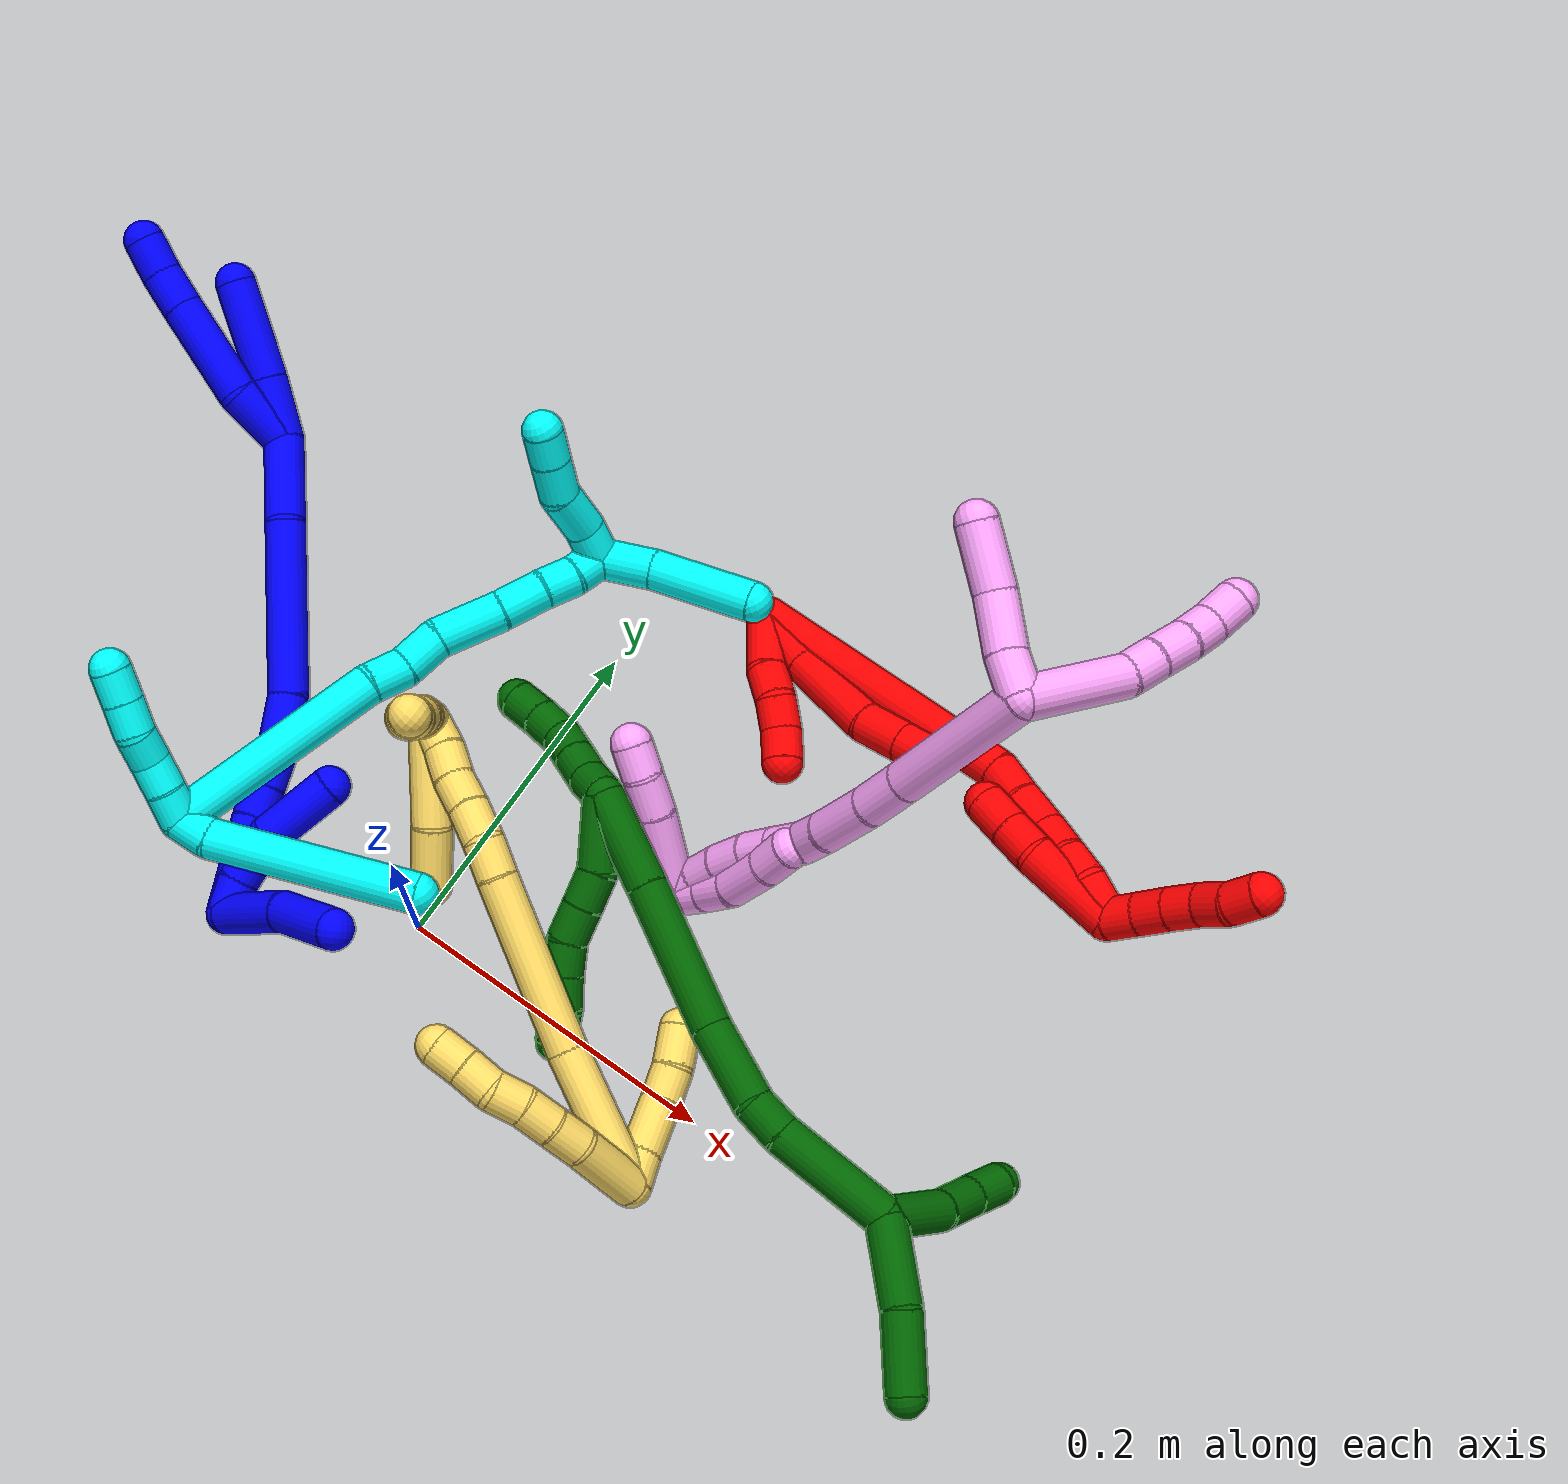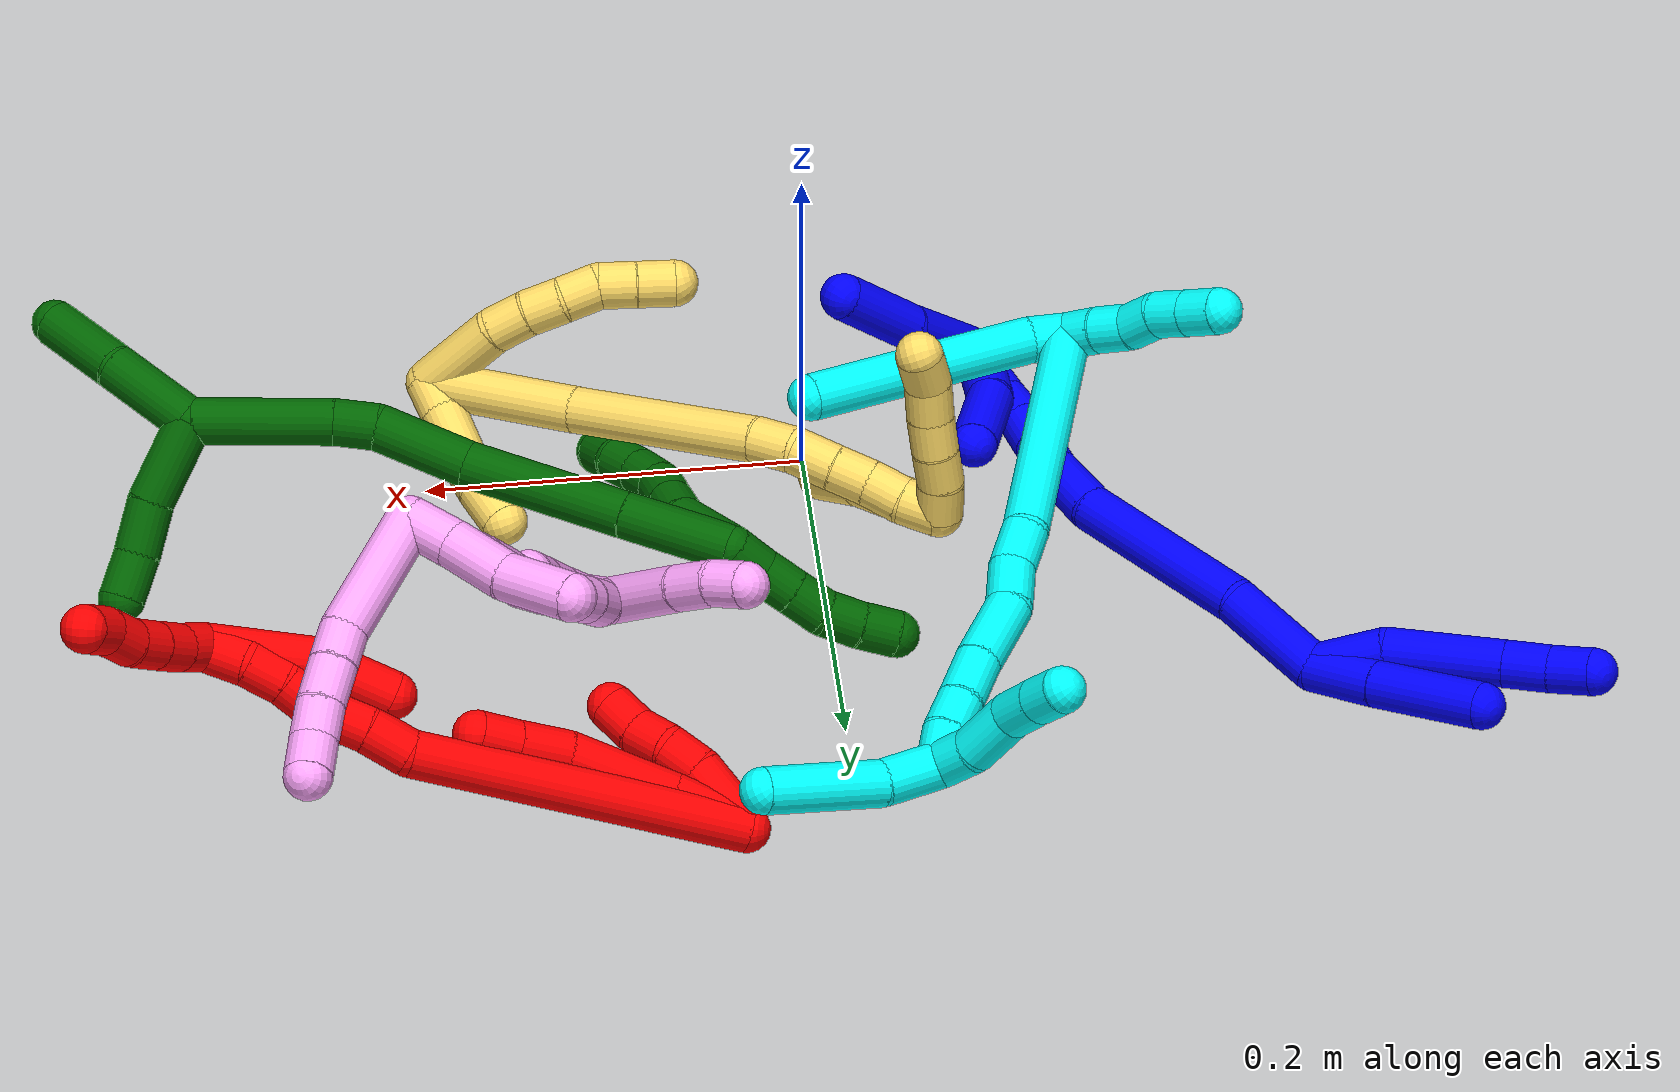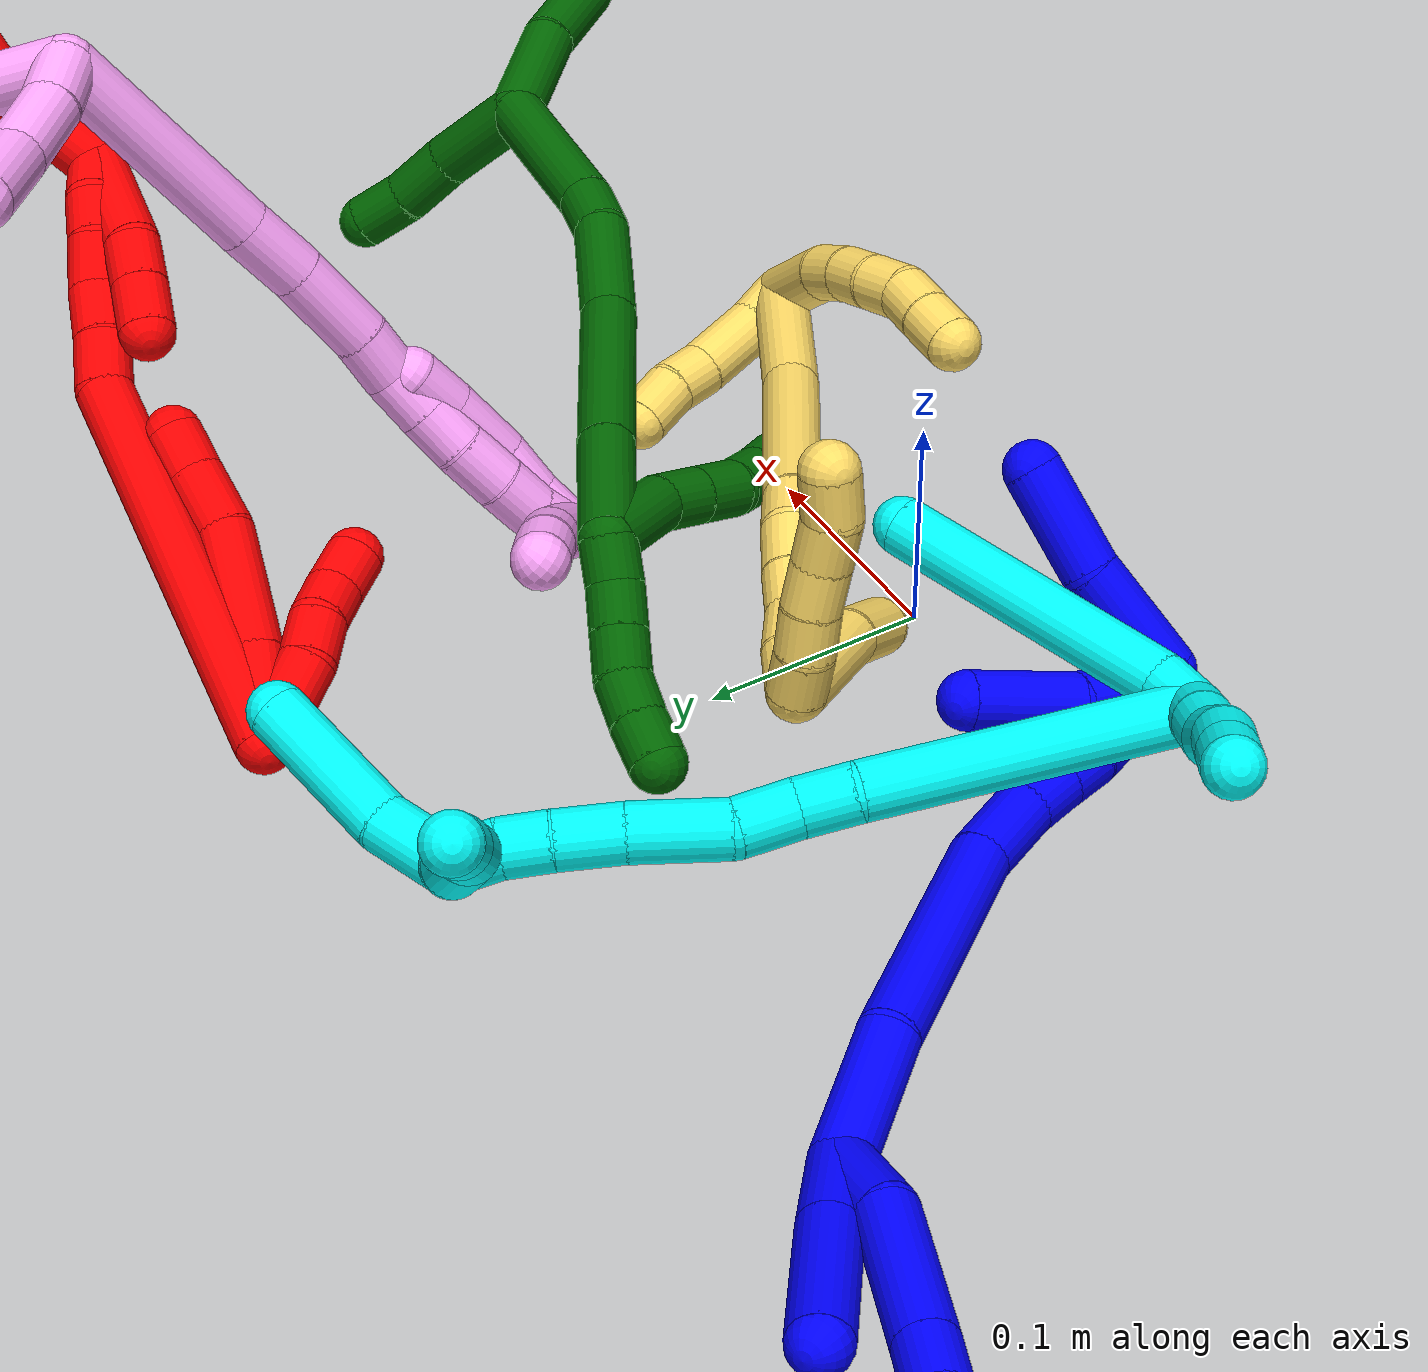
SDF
<sdf version="1.7">
 <world name="default">
  <plugin name="TubeGeneratorPlugin" filename="libtube_generator_plugin.so"/>
  <model name="photoneo_s_sensor">
   <static>1</static>
   <pose>0 0 2 1.57079 1.57079 3.14159</pose>
   <link name="link">
    <inertial><mass>0.1</mass></inertial>
    <sensor name="sensor" type="depth">
     <update_rate>30</update_rate>
     <camera>
      <horizontal_fov>1.22</horizontal_fov>
      <image><width>1920</width><height>1200</height><format>B8G8R8</format></image>
      <clip><near>0.1</near><far>4</far></clip>
      <depth_camera><output>points</output></depth_camera>
     </camera>
     <plugin name="camera_plugin" filename="libgazebo_ros_depth_camera.so">
      <baseline>0.2</baseline>
      <alwaysOn>1</alwaysOn>
      <updateRate>0.0</updateRate>
      <cameraName>camera_ir</cameraName>
      <imageTopicName>/camera/color/image_raw</imageTopicName>
      <cameraInfoTopicName>/camera/color/camera_info</cameraInfoTopicName>
      <depthImageTopicName>/camera/depth/image_raw</depthImageTopicName>
      <depthImageCameraInfoTopicName>/camera/depth/camera_info</depthImageCameraInfoTopicName>
      <pointCloudTopicName>/camera/depth/points</pointCloudTopicName>
      <frameName>fr_optical</frameName>
      <pointCloudCutoff>0.1</pointCloudCutoff>
      <pointCloudCutoffMax>2.0</pointCloudCutoffMax>
      <distortionK1>0</distortionK1>
      <distortionK2>0</distortionK2>
      <distortionK3>0</distortionK3>
      <distortionT1>0</distortionT1>
      <distortionT2>0</distortionT2>
      <CxPrime>0</CxPrime>
      <Cx>0</Cx>
      <Cy>0</Cy>
      <focalLength>0</focalLength>
      <hackBaseline>0</hackBaseline>
     </plugin>
    </sensor>
   </link>
  </model>
  <gravity>0 0 -9.8</gravity>
  <magnetic_field>6e-06 2.3e-05 -4.2e-05</magnetic_field>
  <atmosphere type="adiabatic"/>
  <physics name="default_physics" default="0" type="ode">
   <max_step_size>0.003</max_step_size>
   <real_time_factor>1</real_time_factor>
   <real_time_update_rate>1000</real_time_update_rate>
   <max_contacts>10000</max_contacts>
   <ode>
    <solver>
     <type>quick</type>
     <iters>100</iters>
     <sor>1.3</sor>
     <use_dynamic_moi_rescaling>0</use_dynamic_moi_rescaling>
    </solver>
    <constraints>
     <contact_max_correcting_vel>0</contact_max_correcting_vel>
     <contact_surface_layer>0.001</contact_surface_layer>
     <cfm>0</cfm>
     <erp>0.2</erp>
    </constraints>
   </ode>
  </physics>
  <scene><ambient>0.4 0.4 0.4 1</ambient><background>0.7 0.7 0.7 1</background><shadows>0</shadows></scene>
  <audio><device>default</device></audio>
  <spherical_coordinates>
   <surface_model>EARTH_WGS84</surface_model>
   <latitude_deg>0</latitude_deg>
   <longitude_deg>0</longitude_deg>
   <elevation>0</elevation>
   <heading_deg>0</heading_deg>
  </spherical_coordinates>
  <model name="bin">
   <static>1</static>
   <link name="bottom">
    <collision name="collision-bottom">
     <pose>0 0 -0.01 0 -0 0</pose>
     <geometry><box><size>0.8 0.6 0.02</size></box></geometry>
     <surface>
      <friction><ode><mu>100</mu><mu2>100</mu2></ode></friction>
      <contact><collide_bitmask>65535</collide_bitmask></contact>
     </surface>
    </collision>
   </link>
   <link name="west_wall">
    <collision name="collision-west_wall">
     <pose>-0.41 0 0.1 0 -0 0</pose>
     <geometry><box><size>0.02 0.6 0.2</size></box></geometry>
     <surface>
      <friction><ode><mu>100</mu><mu2>100</mu2></ode></friction>
      <contact><collide_bitmask>65535</collide_bitmask></contact>
     </surface>
    </collision>
   </link>
   <link name="east_wall">
    <collision name="collision-east_wall">
     <pose>0.41 0 0.1 0 -0 0</pose>
     <geometry><box><size>0.02 0.6 0.2</size></box></geometry>
     <surface>
      <friction><ode><mu>100</mu><mu2>100</mu2></ode></friction>
      <contact><collide_bitmask>65535</collide_bitmask></contact>
     </surface>
    </collision>
   </link>
   <link name="south_wall">
    <collision name="collision-south_wall">
     <pose>0 -0.31 0.1 0 -0 0</pose>
     <geometry><box><size>0.8 0.02 0.2</size></box></geometry>
     <surface>
      <friction><ode><mu>100</mu><mu2>100</mu2></ode></friction>
      <contact><collide_bitmask>65535</collide_bitmask></contact>
     </surface>
    </collision>
   </link>
   <link name="north_wall">
    <collision name="collision-north_wall">
     <pose>0 0.31 0.1 0 -0 0</pose>
     <geometry><box><size>0.8 0.02 0.2</size></box></geometry>
     <surface>
      <friction><ode><mu>100</mu><mu2>100</mu2></ode></friction>
      <contact><collide_bitmask>65535</collide_bitmask></contact>
     </surface>
    </collision>
   </link>
  </model>
  <model name="1">
   <static>0</static>
   <link name="1">
    <collision name="collision-cylinder-e_1_2_8">
     <pose>-0.012155 -0.009314 0.012287 0.648608 -0.667629 -0.232116</pose>
     <geometry><cylinder><radius>0.0125</radius><length>0.039266</length></cylinder></geometry>
     <surface>
      <friction><ode><mu>1.16</mu><mu2>1.16</mu2><slip1>0</slip1><slip2>0</slip2></ode></friction>
      <contact><ode><kp>1e+06</kp><kd>1</kd><max_vel>0</max_vel><min_depth>0.001</min_depth></ode></contact>
     </surface>
    </collision>
    <visual name="visual-cylinder-e_1_2_8">
     <pose>-0.012155 -0.009314 0.012287 0.648608 -0.667629 -0.232116</pose>
     <geometry><cylinder><radius>0.0125</radius><length>0.039266</length></cylinder></geometry>
     <material><ambient>0 0 1 1</ambient></material>
    </visual>
    <collision name="collision-cylinder-e_2_8_9">
     <pose>-0.044101 -0.02409 0.048533 0.224178 -0.677986 -0.079337</pose>
     <geometry><cylinder><radius>0.0125</radius><length>0.063105</length></cylinder></geometry>
     <surface>
      <friction><ode><mu>1.16</mu><mu2>1.16</mu2><slip1>0</slip1><slip2>0</slip2></ode></friction>
      <contact><ode><kp>1e+06</kp><kd>1</kd><max_vel>0</max_vel><min_depth>0.001</min_depth></ode></contact>
     </surface>
    </collision>
    <visual name="visual-cylinder-e_2_8_9">
     <pose>-0.044101 -0.02409 0.048533 0.224178 -0.677986 -0.079337</pose>
     <geometry><cylinder><radius>0.0125</radius><length>0.063105</length></cylinder></geometry>
     <material><ambient>0 0 1 1</ambient></material>
    </visual>
    <collision name="collision-cylinder-e_3_9_10">
     <pose>-0.071415 -0.031661 0.082 0.21812 -0.657753 -0.074699</pose>
     <geometry><cylinder><radius>0.0125</radius><length>0.024613</length></cylinder></geometry>
     <surface>
      <friction><ode><mu>1.16</mu><mu2>1.16</mu2><slip1>0</slip1><slip2>0</slip2></ode></friction>
      <contact><ode><kp>1e+06</kp><kd>1</kd><max_vel>0</max_vel><min_depth>0.001</min_depth></ode></contact>
     </surface>
    </collision>
    <visual name="visual-cylinder-e_3_9_10">
     <pose>-0.071415 -0.031661 0.082 0.21812 -0.657753 -0.074699</pose>
     <geometry><cylinder><radius>0.0125</radius><length>0.024613</length></cylinder></geometry>
     <material><ambient>0 0 1 1</ambient></material>
    </visual>
    <collision name="collision-cylinder-e_4_10_6">
     <pose>-0.084693 -0.03667 0.101043 0.295502 -0.523595 -0.079718</pose>
     <geometry><cylinder><radius>0.0125</radius><length>0.023016</length></cylinder></geometry>
     <surface>
      <friction><ode><mu>1.16</mu><mu2>1.16</mu2><slip1>0</slip1><slip2>0</slip2></ode></friction>
      <contact><ode><kp>1e+06</kp><kd>1</kd><max_vel>0</max_vel><min_depth>0.001</min_depth></ode></contact>
     </surface>
    </collision>
    <visual name="visual-cylinder-e_4_10_6">
     <pose>-0.084693 -0.03667 0.101043 0.295502 -0.523595 -0.079718</pose>
     <geometry><cylinder><radius>0.0125</radius><length>0.023016</length></cylinder></geometry>
     <material><ambient>0 0 1 1</ambient></material>
    </visual>
    <collision name="collision-cylinder-e_1_2_11">
     <pose>-0.0068 -0.00253 0.017803 0.141185 -0.361549 -0.025846</pose>
     <geometry><cylinder><radius>0.0125</radius><length>0.03845</length></cylinder></geometry>
     <surface>
      <friction><ode><mu>1.16</mu><mu2>1.16</mu2><slip1>0</slip1><slip2>0</slip2></ode></friction>
      <contact><ode><kp>1e+06</kp><kd>1</kd><max_vel>0</max_vel><min_depth>0.001</min_depth></ode></contact>
     </surface>
    </collision>
    <visual name="visual-cylinder-e_1_2_11">
     <pose>-0.0068 -0.00253 0.017803 0.141185 -0.361549 -0.025846</pose>
     <geometry><cylinder><radius>0.0125</radius><length>0.03845</length></cylinder></geometry>
     <material><ambient>0 0 1 1</ambient></material>
    </visual>
    <collision name="collision-cylinder-e_2_11_5">
     <pose>-0.025583 -0.009925 0.063532 0.172449 -0.399942 -0.035035</pose>
     <geometry><cylinder><radius>0.0125</radius><length>0.06155</length></cylinder></geometry>
     <surface>
      <friction><ode><mu>1.16</mu><mu2>1.16</mu2><slip1>0</slip1><slip2>0</slip2></ode></friction>
      <contact><ode><kp>1e+06</kp><kd>1</kd><max_vel>0</max_vel><min_depth>0.001</min_depth></ode></contact>
     </surface>
    </collision>
    <visual name="visual-cylinder-e_2_11_5">
     <pose>-0.025583 -0.009925 0.063532 0.172449 -0.399942 -0.035035</pose>
     <geometry><cylinder><radius>0.0125</radius><length>0.06155</length></cylinder></geometry>
     <material><ambient>0 0 1 1</ambient></material>
    </visual>
    <collision name="collision-cylinder-e_1_2_12">
     <pose>0.009689 -0.009119 -0.024954 2.79123 0.349681 1.56882</pose>
     <geometry><cylinder><radius>0.0125</radius><length>0.056559</length></cylinder></geometry>
     <surface>
      <friction><ode><mu>1.16</mu><mu2>1.16</mu2><slip1>0</slip1><slip2>0</slip2></ode></friction>
      <contact><ode><kp>1e+06</kp><kd>1</kd><max_vel>0</max_vel><min_depth>0.001</min_depth></ode></contact>
     </surface>
    </collision>
    <visual name="visual-cylinder-e_1_2_12">
     <pose>0.009689 -0.009119 -0.024954 2.79123 0.349681 1.56882</pose>
     <geometry><cylinder><radius>0.0125</radius><length>0.056559</length></cylinder></geometry>
     <material><ambient>0 0 1 1</ambient></material>
    </visual>
    <collision name="collision-cylinder-e_2_12_13">
     <pose>0.031092 -0.024304 -0.101354 3.02423 0.222407 2.17298</pose>
     <geometry><cylinder><radius>0.0125</radius><length>0.10622</length></cylinder></geometry>
     <surface>
      <friction><ode><mu>1.16</mu><mu2>1.16</mu2><slip1>0</slip1><slip2>0</slip2></ode></friction>
      <contact><ode><kp>1e+06</kp><kd>1</kd><max_vel>0</max_vel><min_depth>0.001</min_depth></ode></contact>
     </surface>
    </collision>
    <visual name="visual-cylinder-e_2_12_13">
     <pose>0.031092 -0.024304 -0.101354 3.02423 0.222407 2.17298</pose>
     <geometry><cylinder><radius>0.0125</radius><length>0.10622</length></cylinder></geometry>
     <material><ambient>0 0 1 1</ambient></material>
    </visual>
    <collision name="collision-cylinder-e_3_13_14">
     <pose>0.043613 -0.034394 -0.169878 2.91017 0.045926 0.390182</pose>
     <geometry><cylinder><radius>0.0125</radius><length>0.035131</length></cylinder></geometry>
     <surface>
      <friction><ode><mu>1.16</mu><mu2>1.16</mu2><slip1>0</slip1><slip2>0</slip2></ode></friction>
      <contact><ode><kp>1e+06</kp><kd>1</kd><max_vel>0</max_vel><min_depth>0.001</min_depth></ode></contact>
     </surface>
    </collision>
    <visual name="visual-cylinder-e_3_13_14">
     <pose>0.043613 -0.034394 -0.169878 2.91017 0.045926 0.390182</pose>
     <geometry><cylinder><radius>0.0125</radius><length>0.035131</length></cylinder></geometry>
     <material><ambient>0 0 1 1</ambient></material>
    </visual>
    <collision name="collision-cylinder-e_4_14_15">
     <pose>0.043538 -0.041585 -0.197465 2.84887 -0.080188 -0.531383</pose>
     <geometry><cylinder><radius>0.0125</radius><length>0.02202</length></cylinder></geometry>
     <surface>
      <friction><ode><mu>1.16</mu><mu2>1.16</mu2><slip1>0</slip1><slip2>0</slip2></ode></friction>
      <contact><ode><kp>1e+06</kp><kd>1</kd><max_vel>0</max_vel><min_depth>0.001</min_depth></ode></contact>
     </surface>
    </collision>
    <visual name="visual-cylinder-e_4_14_15">
     <pose>0.043538 -0.041585 -0.197465 2.84887 -0.080188 -0.531383</pose>
     <geometry><cylinder><radius>0.0125</radius><length>0.02202</length></cylinder></geometry>
     <material><ambient>0 0 1 1</ambient></material>
    </visual>
    <collision name="collision-cylinder-e_5_15_16">
     <pose>0.041531 -0.047742 -0.217461 2.83627 -0.11256 -0.702019</pose>
     <geometry><cylinder><radius>0.0125</radius><length>0.020024</length></cylinder></geometry>
     <surface>
      <friction><ode><mu>1.16</mu><mu2>1.16</mu2><slip1>0</slip1><slip2>0</slip2></ode></friction>
      <contact><ode><kp>1e+06</kp><kd>1</kd><max_vel>0</max_vel><min_depth>0.001</min_depth></ode></contact>
     </surface>
    </collision>
    <visual name="visual-cylinder-e_5_15_16">
     <pose>0.041531 -0.047742 -0.217461 2.83627 -0.11256 -0.702019</pose>
     <geometry><cylinder><radius>0.0125</radius><length>0.020024</length></cylinder></geometry>
     <material><ambient>0 0 1 1</ambient></material>
    </visual>
    <collision name="collision-cylinder-e_6_16_17">
     <pose>0.040491 -0.053487 -0.236567 2.86267 0.008462 0.060264</pose>
     <geometry><cylinder><radius>0.0125</radius><length>0.020008</length></cylinder></geometry>
     <surface>
      <friction><ode><mu>1.16</mu><mu2>1.16</mu2><slip1>0</slip1><slip2>0</slip2></ode></friction>
      <contact><ode><kp>1e+06</kp><kd>1</kd><max_vel>0</max_vel><min_depth>0.001</min_depth></ode></contact>
     </surface>
    </collision>
    <visual name="visual-cylinder-e_6_16_17">
     <pose>0.040491 -0.053487 -0.236567 2.86267 0.008462 0.060264</pose>
     <geometry><cylinder><radius>0.0125</radius><length>0.020008</length></cylinder></geometry>
     <material><ambient>0 0 1 1</ambient></material>
    </visual>
    <collision name="collision-cylinder-e_7_17_18">
     <pose>0.041125 -0.059786 -0.255526 2.77896 0.054911 0.297389</pose>
     <geometry><cylinder><radius>0.0125</radius><length>0.020014</length></cylinder></geometry>
     <surface>
      <friction><ode><mu>1.16</mu><mu2>1.16</mu2><slip1>0</slip1><slip2>0</slip2></ode></friction>
      <contact><ode><kp>1e+06</kp><kd>1</kd><max_vel>0</max_vel><min_depth>0.001</min_depth></ode></contact>
     </surface>
    </collision>
    <visual name="visual-cylinder-e_7_17_18">
     <pose>0.041125 -0.059786 -0.255526 2.77896 0.054911 0.297389</pose>
     <geometry><cylinder><radius>0.0125</radius><length>0.020014</length></cylinder></geometry>
     <material><ambient>0 0 1 1</ambient></material>
    </visual>
    <collision name="collision-cylinder-e_8_18_1">
     <pose>0.042387 -0.067242 -0.274057 2.73914 0.071273 0.346051</pose>
     <geometry><cylinder><radius>0.0125</radius><length>0.020025</length></cylinder></geometry>
     <surface>
      <friction><ode><mu>1.16</mu><mu2>1.16</mu2><slip1>0</slip1><slip2>0</slip2></ode></friction>
      <contact><ode><kp>1e+06</kp><kd>1</kd><max_vel>0</max_vel><min_depth>0.001</min_depth></ode></contact>
     </surface>
    </collision>
    <visual name="visual-cylinder-e_8_18_1">
     <pose>0.042387 -0.067242 -0.274057 2.73914 0.071273 0.346051</pose>
     <geometry><cylinder><radius>0.0125</radius><length>0.020025</length></cylinder></geometry>
     <material><ambient>0 0 1 1</ambient></material>
    </visual>
    <collision name="collision-cylinder-e_1_1_19">
     <pose>0.044434 -0.068812 -0.273023 -0.225162 0.126453 -0.014315</pose>
     <geometry><cylinder><radius>0.0125</radius><length>0.021145</length></cylinder></geometry>
     <surface>
      <friction><ode><mu>1.16</mu><mu2>1.16</mu2><slip1>0</slip1><slip2>0</slip2></ode></friction>
      <contact><ode><kp>1e+06</kp><kd>1</kd><max_vel>0</max_vel><min_depth>0.001</min_depth></ode></contact>
     </surface>
    </collision>
    <visual name="visual-cylinder-e_1_1_19">
     <pose>0.044434 -0.068812 -0.273023 -0.225162 0.126453 -0.014315</pose>
     <geometry><cylinder><radius>0.0125</radius><length>0.021145</length></cylinder></geometry>
     <material><ambient>0 0 1 1</ambient></material>
    </visual>
    <collision name="collision-cylinder-e_2_19_20">
     <pose>0.052302 -0.063728 -0.248909 -0.194927 0.432448 -0.042947</pose>
     <geometry><cylinder><radius>0.0125</radius><length>0.031187</length></cylinder></geometry>
     <surface>
      <friction><ode><mu>1.16</mu><mu2>1.16</mu2><slip1>0</slip1><slip2>0</slip2></ode></friction>
      <contact><ode><kp>1e+06</kp><kd>1</kd><max_vel>0</max_vel><min_depth>0.001</min_depth></ode></contact>
     </surface>
    </collision>
    <visual name="visual-cylinder-e_2_19_20">
     <pose>0.052302 -0.063728 -0.248909 -0.194927 0.432448 -0.042947</pose>
     <geometry><cylinder><radius>0.0125</radius><length>0.031187</length></cylinder></geometry>
     <material><ambient>0 0 1 1</ambient></material>
    </visual>
    <collision name="collision-cylinder-e_3_20_4">
     <pose>0.074486 -0.054856 -0.218119 -0.347936 0.716231 -0.131357</pose>
     <geometry><cylinder><radius>0.0125</radius><length>0.047668</length></cylinder></geometry>
     <surface>
      <friction><ode><mu>1.16</mu><mu2>1.16</mu2><slip1>0</slip1><slip2>0</slip2></ode></friction>
      <contact><ode><kp>1e+06</kp><kd>1</kd><max_vel>0</max_vel><min_depth>0.001</min_depth></ode></contact>
     </surface>
    </collision>
    <visual name="visual-cylinder-e_3_20_4">
     <pose>0.074486 -0.054856 -0.218119 -0.347936 0.716231 -0.131357</pose>
     <geometry><cylinder><radius>0.0125</radius><length>0.047668</length></cylinder></geometry>
     <material><ambient>0 0 1 1</ambient></material>
    </visual>
    <collision name="collision-cylinder-e_1_1_21">
     <pose>0.067576 -0.079302 -0.278607 1.05329 1.20495 0.760815</pose>
     <geometry><cylinder><radius>0.0125</radius><length>0.05242</length></cylinder></geometry>
     <surface>
      <friction><ode><mu>1.16</mu><mu2>1.16</mu2><slip1>0</slip1><slip2>0</slip2></ode></friction>
      <contact><ode><kp>1e+06</kp><kd>1</kd><max_vel>0</max_vel><min_depth>0.001</min_depth></ode></contact>
     </surface>
    </collision>
    <visual name="visual-cylinder-e_1_1_21">
     <pose>0.067576 -0.079302 -0.278607 1.05329 1.20495 0.760815</pose>
     <geometry><cylinder><radius>0.0125</radius><length>0.05242</length></cylinder></geometry>
     <material><ambient>0 0 1 1</ambient></material>
    </visual>
    <collision name="collision-cylinder-e_2_21_3">
     <pose>0.114378 -0.095549 -0.275354 1.74024 1.21818 1.38203</pose>
     <geometry><cylinder><radius>0.0125</radius><length>0.04758</length></cylinder></geometry>
     <surface>
      <friction><ode><mu>1.16</mu><mu2>1.16</mu2><slip1>0</slip1><slip2>0</slip2></ode></friction>
      <contact><ode><kp>1e+06</kp><kd>1</kd><max_vel>0</max_vel><min_depth>0.001</min_depth></ode></contact>
     </surface>
    </collision>
    <visual name="visual-cylinder-e_2_21_3">
     <pose>0.114378 -0.095549 -0.275354 1.74024 1.21818 1.38203</pose>
     <geometry><cylinder><radius>0.0125</radius><length>0.04758</length></cylinder></geometry>
     <material><ambient>0 0 1 1</ambient></material>
    </visual>
    <collision name="collision-sphere-3">
     <pose>0.136704 -0.103647 -0.27674 0 -0 0</pose>
     <geometry><sphere><radius>0.0125</radius></sphere></geometry>
     <surface>
      <friction><ode><mu>1.16</mu><mu2>1.16</mu2><slip1>0</slip1><slip2>0</slip2></ode></friction>
      <contact><ode><kp>1e+06</kp><kd>1</kd><max_vel>0</max_vel><min_depth>0.001</min_depth></ode></contact>
     </surface>
    </collision>
    <visual name="visual-sphere-3">
     <pose>0.136704 -0.103647 -0.27674 0 -0 0</pose>
     <geometry><sphere><radius>0.0125</radius></sphere></geometry>
     <material><ambient>0 0 1 1</ambient></material>
    </visual>
    <collision name="collision-sphere-21">
     <pose>0.092052 -0.087451 -0.273969 0 -0 0</pose>
     <geometry><sphere><radius>0.0125</radius></sphere></geometry>
     <surface>
      <friction><ode><mu>1.16</mu><mu2>1.16</mu2><slip1>0</slip1><slip2>0</slip2></ode></friction>
      <contact><ode><kp>1e+06</kp><kd>1</kd><max_vel>0</max_vel><min_depth>0.001</min_depth></ode></contact>
     </surface>
    </collision>
    <visual name="visual-sphere-21">
     <pose>0.092052 -0.087451 -0.273969 0 -0 0</pose>
     <geometry><sphere><radius>0.0125</radius></sphere></geometry>
     <material><ambient>0 0 1 1</ambient></material>
    </visual>
    <collision name="collision-sphere-4">
     <pose>0.090134 -0.048726 -0.201219 0 -0 0</pose>
     <geometry><sphere><radius>0.0125</radius></sphere></geometry>
     <surface>
      <friction><ode><mu>1.16</mu><mu2>1.16</mu2><slip1>0</slip1><slip2>0</slip2></ode></friction>
      <contact><ode><kp>1e+06</kp><kd>1</kd><max_vel>0</max_vel><min_depth>0.001</min_depth></ode></contact>
     </surface>
    </collision>
    <visual name="visual-sphere-4">
     <pose>0.090134 -0.048726 -0.201219 0 -0 0</pose>
     <geometry><sphere><radius>0.0125</radius></sphere></geometry>
     <material><ambient>0 0 1 1</ambient></material>
    </visual>
    <collision name="collision-sphere-20">
     <pose>0.058838 -0.060986 -0.235019 0 -0 0</pose>
     <geometry><sphere><radius>0.0125</radius></sphere></geometry>
     <surface>
      <friction><ode><mu>1.16</mu><mu2>1.16</mu2><slip1>0</slip1><slip2>0</slip2></ode></friction>
      <contact><ode><kp>1e+06</kp><kd>1</kd><max_vel>0</max_vel><min_depth>0.001</min_depth></ode></contact>
     </surface>
    </collision>
    <visual name="visual-sphere-20">
     <pose>0.058838 -0.060986 -0.235019 0 -0 0</pose>
     <geometry><sphere><radius>0.0125</radius></sphere></geometry>
     <material><ambient>0 0 1 1</ambient></material>
    </visual>
    <collision name="collision-sphere-11">
     <pose>-0.013601 -0.005061 0.035606 0 -0 0</pose>
     <geometry><sphere><radius>0.0125</radius></sphere></geometry>
     <surface>
      <friction><ode><mu>1.16</mu><mu2>1.16</mu2><slip1>0</slip1><slip2>0</slip2></ode></friction>
      <contact><ode><kp>1e+06</kp><kd>1</kd><max_vel>0</max_vel><min_depth>0.001</min_depth></ode></contact>
     </surface>
    </collision>
    <visual name="visual-sphere-11">
     <pose>-0.013601 -0.005061 0.035606 0 -0 0</pose>
     <geometry><sphere><radius>0.0125</radius></sphere></geometry>
     <material><ambient>0 0 1 1</ambient></material>
    </visual>
    <collision name="collision-sphere-6">
     <pose>-0.090447 -0.039573 0.110577 0 -0 0</pose>
     <geometry><sphere><radius>0.0125</radius></sphere></geometry>
     <surface>
      <friction><ode><mu>1.16</mu><mu2>1.16</mu2><slip1>0</slip1><slip2>0</slip2></ode></friction>
      <contact><ode><kp>1e+06</kp><kd>1</kd><max_vel>0</max_vel><min_depth>0.001</min_depth></ode></contact>
     </surface>
    </collision>
    <visual name="visual-sphere-6">
     <pose>-0.090447 -0.039573 0.110577 0 -0 0</pose>
     <geometry><sphere><radius>0.0125</radius></sphere></geometry>
     <material><ambient>0 0 1 1</ambient></material>
    </visual>
    <collision name="collision-sphere-10">
     <pose>-0.078939 -0.033768 0.091509 0 -0 0</pose>
     <geometry><sphere><radius>0.0125</radius></sphere></geometry>
     <surface>
      <friction><ode><mu>1.16</mu><mu2>1.16</mu2><slip1>0</slip1><slip2>0</slip2></ode></friction>
      <contact><ode><kp>1e+06</kp><kd>1</kd><max_vel>0</max_vel><min_depth>0.001</min_depth></ode></contact>
     </surface>
    </collision>
    <visual name="visual-sphere-10">
     <pose>-0.078939 -0.033768 0.091509 0 -0 0</pose>
     <geometry><sphere><radius>0.0125</radius></sphere></geometry>
     <material><ambient>0 0 1 1</ambient></material>
    </visual>
    <collision name="collision-sphere-9">
     <pose>-0.063892 -0.029553 0.072492 0 -0 0</pose>
     <geometry><sphere><radius>0.0125</radius></sphere></geometry>
     <surface>
      <friction><ode><mu>1.16</mu><mu2>1.16</mu2><slip1>0</slip1><slip2>0</slip2></ode></friction>
      <contact><ode><kp>1e+06</kp><kd>1</kd><max_vel>0</max_vel><min_depth>0.001</min_depth></ode></contact>
     </surface>
    </collision>
    <visual name="visual-sphere-9">
     <pose>-0.063892 -0.029553 0.072492 0 -0 0</pose>
     <geometry><sphere><radius>0.0125</radius></sphere></geometry>
     <material><ambient>0 0 1 1</ambient></material>
    </visual>
    <collision name="collision-sphere-2">
     <geometry><sphere><radius>0.0125</radius></sphere></geometry>
     <surface>
      <friction><ode><mu>1.16</mu><mu2>1.16</mu2><slip1>0</slip1><slip2>0</slip2></ode></friction>
      <contact><ode><kp>1e+06</kp><kd>1</kd><max_vel>0</max_vel><min_depth>0.001</min_depth></ode></contact>
     </surface>
    </collision>
    <visual name="visual-sphere-2">
     <geometry><sphere><radius>0.0125</radius></sphere></geometry>
     <material><ambient>0 0 1 1</ambient></material>
    </visual>
    <collision name="collision-sphere-19">
     <pose>0.045767 -0.06647 -0.262799 0 -0 0</pose>
     <geometry><sphere><radius>0.0125</radius></sphere></geometry>
     <surface>
      <friction><ode><mu>1.16</mu><mu2>1.16</mu2><slip1>0</slip1><slip2>0</slip2></ode></friction>
      <contact><ode><kp>1e+06</kp><kd>1</kd><max_vel>0</max_vel><min_depth>0.001</min_depth></ode></contact>
     </surface>
    </collision>
    <visual name="visual-sphere-19">
     <pose>0.045767 -0.06647 -0.262799 0 -0 0</pose>
     <geometry><sphere><radius>0.0125</radius></sphere></geometry>
     <material><ambient>0 0 1 1</ambient></material>
    </visual>
    <collision name="collision-sphere-8">
     <pose>-0.024311 -0.018627 0.024574 0 -0 0</pose>
     <geometry><sphere><radius>0.0125</radius></sphere></geometry>
     <surface>
      <friction><ode><mu>1.16</mu><mu2>1.16</mu2><slip1>0</slip1><slip2>0</slip2></ode></friction>
      <contact><ode><kp>1e+06</kp><kd>1</kd><max_vel>0</max_vel><min_depth>0.001</min_depth></ode></contact>
     </surface>
    </collision>
    <visual name="visual-sphere-8">
     <pose>-0.024311 -0.018627 0.024574 0 -0 0</pose>
     <geometry><sphere><radius>0.0125</radius></sphere></geometry>
     <material><ambient>0 0 1 1</ambient></material>
    </visual>
    <collision name="collision-sphere-5">
     <pose>-0.037566 -0.014789 0.091458 0 -0 0</pose>
     <geometry><sphere><radius>0.0125</radius></sphere></geometry>
     <surface>
      <friction><ode><mu>1.16</mu><mu2>1.16</mu2><slip1>0</slip1><slip2>0</slip2></ode></friction>
      <contact><ode><kp>1e+06</kp><kd>1</kd><max_vel>0</max_vel><min_depth>0.001</min_depth></ode></contact>
     </surface>
    </collision>
    <visual name="visual-sphere-5">
     <pose>-0.037566 -0.014789 0.091458 0 -0 0</pose>
     <geometry><sphere><radius>0.0125</radius></sphere></geometry>
     <material><ambient>0 0 1 1</ambient></material>
    </visual>
    <collision name="collision-sphere-12">
     <pose>0.019377 -0.018238 -0.049908 0 -0 0</pose>
     <geometry><sphere><radius>0.0125</radius></sphere></geometry>
     <surface>
      <friction><ode><mu>1.16</mu><mu2>1.16</mu2><slip1>0</slip1><slip2>0</slip2></ode></friction>
      <contact><ode><kp>1e+06</kp><kd>1</kd><max_vel>0</max_vel><min_depth>0.001</min_depth></ode></contact>
     </surface>
    </collision>
    <visual name="visual-sphere-12">
     <pose>0.019377 -0.018238 -0.049908 0 -0 0</pose>
     <geometry><sphere><radius>0.0125</radius></sphere></geometry>
     <material><ambient>0 0 1 1</ambient></material>
    </visual>
    <collision name="collision-sphere-13">
     <pose>0.042807 -0.030369 -0.152799 0 -0 0</pose>
     <geometry><sphere><radius>0.0125</radius></sphere></geometry>
     <surface>
      <friction><ode><mu>1.16</mu><mu2>1.16</mu2><slip1>0</slip1><slip2>0</slip2></ode></friction>
      <contact><ode><kp>1e+06</kp><kd>1</kd><max_vel>0</max_vel><min_depth>0.001</min_depth></ode></contact>
     </surface>
    </collision>
    <visual name="visual-sphere-13">
     <pose>0.042807 -0.030369 -0.152799 0 -0 0</pose>
     <geometry><sphere><radius>0.0125</radius></sphere></geometry>
     <material><ambient>0 0 1 1</ambient></material>
    </visual>
    <collision name="collision-sphere-14">
     <pose>0.04442 -0.038418 -0.186957 0 -0 0</pose>
     <geometry><sphere><radius>0.0125</radius></sphere></geometry>
     <surface>
      <friction><ode><mu>1.16</mu><mu2>1.16</mu2><slip1>0</slip1><slip2>0</slip2></ode></friction>
      <contact><ode><kp>1e+06</kp><kd>1</kd><max_vel>0</max_vel><min_depth>0.001</min_depth></ode></contact>
     </surface>
    </collision>
    <visual name="visual-sphere-14">
     <pose>0.04442 -0.038418 -0.186957 0 -0 0</pose>
     <geometry><sphere><radius>0.0125</radius></sphere></geometry>
     <material><ambient>0 0 1 1</ambient></material>
    </visual>
    <collision name="collision-sphere-15">
     <pose>0.042656 -0.044752 -0.207973 0 -0 0</pose>
     <geometry><sphere><radius>0.0125</radius></sphere></geometry>
     <surface>
      <friction><ode><mu>1.16</mu><mu2>1.16</mu2><slip1>0</slip1><slip2>0</slip2></ode></friction>
      <contact><ode><kp>1e+06</kp><kd>1</kd><max_vel>0</max_vel><min_depth>0.001</min_depth></ode></contact>
     </surface>
    </collision>
    <visual name="visual-sphere-15">
     <pose>0.042656 -0.044752 -0.207973 0 -0 0</pose>
     <geometry><sphere><radius>0.0125</radius></sphere></geometry>
     <material><ambient>0 0 1 1</ambient></material>
    </visual>
    <collision name="collision-sphere-16">
     <pose>0.040407 -0.050733 -0.226949 0 -0 0</pose>
     <geometry><sphere><radius>0.0125</radius></sphere></geometry>
     <surface>
      <friction><ode><mu>1.16</mu><mu2>1.16</mu2><slip1>0</slip1><slip2>0</slip2></ode></friction>
      <contact><ode><kp>1e+06</kp><kd>1</kd><max_vel>0</max_vel><min_depth>0.001</min_depth></ode></contact>
     </surface>
    </collision>
    <visual name="visual-sphere-16">
     <pose>0.040407 -0.050733 -0.226949 0 -0 0</pose>
     <geometry><sphere><radius>0.0125</radius></sphere></geometry>
     <material><ambient>0 0 1 1</ambient></material>
    </visual>
    <collision name="collision-sphere-17">
     <pose>0.040576 -0.056241 -0.246184 0 -0 0</pose>
     <geometry><sphere><radius>0.0125</radius></sphere></geometry>
     <surface>
      <friction><ode><mu>1.16</mu><mu2>1.16</mu2><slip1>0</slip1><slip2>0</slip2></ode></friction>
      <contact><ode><kp>1e+06</kp><kd>1</kd><max_vel>0</max_vel><min_depth>0.001</min_depth></ode></contact>
     </surface>
    </collision>
    <visual name="visual-sphere-17">
     <pose>0.040576 -0.056241 -0.246184 0 -0 0</pose>
     <geometry><sphere><radius>0.0125</radius></sphere></geometry>
     <material><ambient>0 0 1 1</ambient></material>
    </visual>
    <collision name="collision-sphere-18">
     <pose>0.041674 -0.06333 -0.264868 0 -0 0</pose>
     <geometry><sphere><radius>0.0125</radius></sphere></geometry>
     <surface>
      <friction><ode><mu>1.16</mu><mu2>1.16</mu2><slip1>0</slip1><slip2>0</slip2></ode></friction>
      <contact><ode><kp>1e+06</kp><kd>1</kd><max_vel>0</max_vel><min_depth>0.001</min_depth></ode></contact>
     </surface>
    </collision>
    <visual name="visual-sphere-18">
     <pose>0.041674 -0.06333 -0.264868 0 -0 0</pose>
     <geometry><sphere><radius>0.0125</radius></sphere></geometry>
     <material><ambient>0 0 1 1</ambient></material>
    </visual>
    <collision name="collision-sphere-1">
     <pose>0.0431 -0.071153 -0.283246 0 -0 0</pose>
     <geometry><sphere><radius>0.0125</radius></sphere></geometry>
     <surface>
      <friction><ode><mu>1.16</mu><mu2>1.16</mu2><slip1>0</slip1><slip2>0</slip2></ode></friction>
      <contact><ode><kp>1e+06</kp><kd>1</kd><max_vel>0</max_vel><min_depth>0.001</min_depth></ode></contact>
     </surface>
    </collision>
    <visual name="visual-sphere-1">
     <pose>0.0431 -0.071153 -0.283246 0 -0 0</pose>
     <geometry><sphere><radius>0.0125</radius></sphere></geometry>
     <material><ambient>0 0 1 1</ambient></material>
    </visual>
    <inertial>
     <pose>0.021276 -0.038358 -0.108451 0 -0 0</pose>
     <mass>0.75</mass>
     <inertia><ixx>0.000131</ixx><ixy>0</ixy><ixz>0</ixz><iyy>0.000243</iyy><iyz>0</iyz><izz>9e-06</izz></inertia>
    </inertial>
   </link>
   <pose>-0.244554 0.194267 0.012189 -1.27437 -0.407574 0.376242</pose>
  </model>
  <model name="2">
   <static>0</static>
   <link name="2">
    <collision name="collision-cylinder-e_1_2_8">
     <pose>-0.005489 -0.0058 -0.019425 2.85143 -0.264442 -1.47693</pose>
     <geometry><cylinder><radius>0.0125</radius><length>0.042005</length></cylinder></geometry>
     <surface>
      <friction><ode><mu>1.16</mu><mu2>1.16</mu2><slip1>0</slip1><slip2>0</slip2></ode></friction>
      <contact><ode><kp>1e+06</kp><kd>1</kd><max_vel>0</max_vel><min_depth>0.001</min_depth></ode></contact>
     </surface>
    </collision>
    <visual name="visual-cylinder-e_1_2_8">
     <pose>-0.005489 -0.0058 -0.019425 2.85143 -0.264442 -1.47693</pose>
     <geometry><cylinder><radius>0.0125</radius><length>0.042005</length></cylinder></geometry>
     <material><ambient>1 0 0 1</ambient></material>
    </visual>
    <collision name="collision-cylinder-e_2_8_9">
     <pose>-0.016445 -0.022745 -0.064976 2.73838 -0.190127 -0.873037</pose>
     <geometry><cylinder><radius>0.0125</radius><length>0.057849</length></cylinder></geometry>
     <surface>
      <friction><ode><mu>1.16</mu><mu2>1.16</mu2><slip1>0</slip1><slip2>0</slip2></ode></friction>
      <contact><ode><kp>1e+06</kp><kd>1</kd><max_vel>0</max_vel><min_depth>0.001</min_depth></ode></contact>
     </surface>
    </collision>
    <visual name="visual-cylinder-e_2_8_9">
     <pose>-0.016445 -0.022745 -0.064976 2.73838 -0.190127 -0.873037</pose>
     <geometry><cylinder><radius>0.0125</radius><length>0.057849</length></cylinder></geometry>
     <material><ambient>1 0 0 1</ambient></material>
    </visual>
    <collision name="collision-cylinder-e_3_9_10">
     <pose>-0.021575 -0.041021 -0.103519 2.62028 0.023511 0.088093</pose>
     <geometry><cylinder><radius>0.0125</radius><length>0.028648</length></cylinder></geometry>
     <surface>
      <friction><ode><mu>1.16</mu><mu2>1.16</mu2><slip1>0</slip1><slip2>0</slip2></ode></friction>
      <contact><ode><kp>1e+06</kp><kd>1</kd><max_vel>0</max_vel><min_depth>0.001</min_depth></ode></contact>
     </surface>
    </collision>
    <visual name="visual-cylinder-e_3_9_10">
     <pose>-0.021575 -0.041021 -0.103519 2.62028 0.023511 0.088093</pose>
     <geometry><cylinder><radius>0.0125</radius><length>0.028648</length></cylinder></geometry>
     <material><ambient>1 0 0 1</ambient></material>
    </visual>
    <collision name="collision-cylinder-e_4_10_6">
     <pose>-0.021306 -0.053628 -0.125187 2.60715 -0.006351 -0.023198</pose>
     <geometry><cylinder><radius>0.0125</radius><length>0.021497</length></cylinder></geometry>
     <surface>
      <friction><ode><mu>1.16</mu><mu2>1.16</mu2><slip1>0</slip1><slip2>0</slip2></ode></friction>
      <contact><ode><kp>1e+06</kp><kd>1</kd><max_vel>0</max_vel><min_depth>0.001</min_depth></ode></contact>
     </surface>
    </collision>
    <visual name="visual-cylinder-e_4_10_6">
     <pose>-0.021306 -0.053628 -0.125187 2.60715 -0.006351 -0.023198</pose>
     <geometry><cylinder><radius>0.0125</radius><length>0.021497</length></cylinder></geometry>
     <material><ambient>1 0 0 1</ambient></material>
    </visual>
    <collision name="collision-cylinder-e_1_2_11">
     <pose>-0.014181 -0.000981 -0.013891 3.07108 -0.794458 -2.97384</pose>
     <geometry><cylinder><radius>0.0125</radius><length>0.039751</length></cylinder></geometry>
     <surface>
      <friction><ode><mu>1.16</mu><mu2>1.16</mu2><slip1>0</slip1><slip2>0</slip2></ode></friction>
      <contact><ode><kp>1e+06</kp><kd>1</kd><max_vel>0</max_vel><min_depth>0.001</min_depth></ode></contact>
     </surface>
    </collision>
    <visual name="visual-cylinder-e_1_2_11">
     <pose>-0.014181 -0.000981 -0.013891 3.07108 -0.794458 -2.97384</pose>
     <geometry><cylinder><radius>0.0125</radius><length>0.039751</length></cylinder></geometry>
     <material><ambient>1 0 0 1</ambient></material>
    </visual>
    <collision name="collision-cylinder-e_2_11_12">
     <pose>-0.033428 -0.002728 -0.036492 3.05391 -0.525201 -2.81804</pose>
     <geometry><cylinder><radius>0.0125</radius><length>0.020209</length></cylinder></geometry>
     <surface>
      <friction><ode><mu>1.16</mu><mu2>1.16</mu2><slip1>0</slip1><slip2>0</slip2></ode></friction>
      <contact><ode><kp>1e+06</kp><kd>1</kd><max_vel>0</max_vel><min_depth>0.001</min_depth></ode></contact>
     </surface>
    </collision>
    <visual name="visual-cylinder-e_2_11_12">
     <pose>-0.033428 -0.002728 -0.036492 3.05391 -0.525201 -2.81804</pose>
     <geometry><cylinder><radius>0.0125</radius><length>0.020209</length></cylinder></geometry>
     <material><ambient>1 0 0 1</ambient></material>
    </visual>
    <collision name="collision-cylinder-e_3_12_13">
     <pose>-0.042879 -0.001208 -0.053897 -2.88464 -0.45373 2.12115</pose>
     <geometry><cylinder><radius>0.0125</radius><length>0.020007</length></cylinder></geometry>
     <surface>
      <friction><ode><mu>1.16</mu><mu2>1.16</mu2><slip1>0</slip1><slip2>0</slip2></ode></friction>
      <contact><ode><kp>1e+06</kp><kd>1</kd><max_vel>0</max_vel><min_depth>0.001</min_depth></ode></contact>
     </surface>
    </collision>
    <visual name="visual-cylinder-e_3_12_13">
     <pose>-0.042879 -0.001208 -0.053897 -2.88464 -0.45373 2.12115</pose>
     <geometry><cylinder><radius>0.0125</radius><length>0.020007</length></cylinder></geometry>
     <material><ambient>1 0 0 1</ambient></material>
    </visual>
    <collision name="collision-cylinder-e_4_13_5">
     <pose>-0.053541 0.002148 -0.070325 -3.00389 -0.67727 2.75488</pose>
     <geometry><cylinder><radius>0.0125</radius><length>0.020033</length></cylinder></geometry>
     <surface>
      <friction><ode><mu>1.16</mu><mu2>1.16</mu2><slip1>0</slip1><slip2>0</slip2></ode></friction>
      <contact><ode><kp>1e+06</kp><kd>1</kd><max_vel>0</max_vel><min_depth>0.001</min_depth></ode></contact>
     </surface>
    </collision>
    <visual name="visual-cylinder-e_4_13_5">
     <pose>-0.053541 0.002148 -0.070325 -3.00389 -0.67727 2.75488</pose>
     <geometry><cylinder><radius>0.0125</radius><length>0.020033</length></cylinder></geometry>
     <material><ambient>1 0 0 1</ambient></material>
    </visual>
    <collision name="collision-cylinder-e_1_2_14">
     <pose>-0.001774 -0.038281 -0.082206 2.70578 -0.019562 -0.088292</pose>
     <geometry><cylinder><radius>0.0125</radius><length>0.1814</length></cylinder></geometry>
     <surface>
      <friction><ode><mu>1.16</mu><mu2>1.16</mu2><slip1>0</slip1><slip2>0</slip2></ode></friction>
      <contact><ode><kp>1e+06</kp><kd>1</kd><max_vel>0</max_vel><min_depth>0.001</min_depth></ode></contact>
     </surface>
    </collision>
    <visual name="visual-cylinder-e_1_2_14">
     <pose>-0.001774 -0.038281 -0.082206 2.70578 -0.019562 -0.088292</pose>
     <geometry><cylinder><radius>0.0125</radius><length>0.1814</length></cylinder></geometry>
     <material><ambient>1 0 0 1</ambient></material>
    </visual>
    <collision name="collision-cylinder-e_2_14_15">
     <pose>-0.007729 -0.080646 -0.174975 2.77268 -0.353661 -1.52765</pose>
     <geometry><cylinder><radius>0.0125</radius><length>0.024143</length></cylinder></geometry>
     <surface>
      <friction><ode><mu>1.16</mu><mu2>1.16</mu2><slip1>0</slip1><slip2>0</slip2></ode></friction>
      <contact><ode><kp>1e+06</kp><kd>1</kd><max_vel>0</max_vel><min_depth>0.001</min_depth></ode></contact>
     </surface>
    </collision>
    <visual name="visual-cylinder-e_2_14_15">
     <pose>-0.007729 -0.080646 -0.174975 2.77268 -0.353661 -1.52765</pose>
     <geometry><cylinder><radius>0.0125</radius><length>0.024143</length></cylinder></geometry>
     <material><ambient>1 0 0 1</ambient></material>
    </visual>
    <collision name="collision-cylinder-e_3_15_16">
     <pose>-0.014977 -0.088157 -0.197464 2.8618 -0.242281 -1.42573</pose>
     <geometry><cylinder><radius>0.0125</radius><length>0.025566</length></cylinder></geometry>
     <surface>
      <friction><ode><mu>1.16</mu><mu2>1.16</mu2><slip1>0</slip1><slip2>0</slip2></ode></friction>
      <contact><ode><kp>1e+06</kp><kd>1</kd><max_vel>0</max_vel><min_depth>0.001</min_depth></ode></contact>
     </surface>
    </collision>
    <visual name="visual-cylinder-e_3_15_16">
     <pose>-0.014977 -0.088157 -0.197464 2.8618 -0.242281 -1.42573</pose>
     <geometry><cylinder><radius>0.0125</radius><length>0.025566</length></cylinder></geometry>
     <material><ambient>1 0 0 1</ambient></material>
    </visual>
    <collision name="collision-cylinder-e_4_16_17">
     <pose>-0.023163 -0.096994 -0.218737 2.61683 -0.442708 -1.39487</pose>
     <geometry><cylinder><radius>0.0125</radius><length>0.023903</length></cylinder></geometry>
     <surface>
      <friction><ode><mu>1.16</mu><mu2>1.16</mu2><slip1>0</slip1><slip2>0</slip2></ode></friction>
      <contact><ode><kp>1e+06</kp><kd>1</kd><max_vel>0</max_vel><min_depth>0.001</min_depth></ode></contact>
     </surface>
    </collision>
    <visual name="visual-cylinder-e_4_16_17">
     <pose>-0.023163 -0.096994 -0.218737 2.61683 -0.442708 -1.39487</pose>
     <geometry><cylinder><radius>0.0125</radius><length>0.023903</length></cylinder></geometry>
     <material><ambient>1 0 0 1</ambient></material>
    </visual>
    <collision name="collision-cylinder-e_5_17_18">
     <pose>-0.031471 -0.105638 -0.237318 2.80486 -0.314984 -1.50288</pose>
     <geometry><cylinder><radius>0.0125</radius><length>0.020582</length></cylinder></geometry>
     <surface>
      <friction><ode><mu>1.16</mu><mu2>1.16</mu2><slip1>0</slip1><slip2>0</slip2></ode></friction>
      <contact><ode><kp>1e+06</kp><kd>1</kd><max_vel>0</max_vel><min_depth>0.001</min_depth></ode></contact>
     </surface>
    </collision>
    <visual name="visual-cylinder-e_5_17_18">
     <pose>-0.031471 -0.105638 -0.237318 2.80486 -0.314984 -1.50288</pose>
     <geometry><cylinder><radius>0.0125</radius><length>0.020582</length></cylinder></geometry>
     <material><ambient>1 0 0 1</ambient></material>
    </visual>
    <collision name="collision-cylinder-e_6_18_1">
     <pose>-0.037796 -0.109275 -0.25834 3.10726 -0.259967 -2.88043</pose>
     <geometry><cylinder><radius>0.0125</radius><length>0.024407</length></cylinder></geometry>
     <surface>
      <friction><ode><mu>1.16</mu><mu2>1.16</mu2><slip1>0</slip1><slip2>0</slip2></ode></friction>
      <contact><ode><kp>1e+06</kp><kd>1</kd><max_vel>0</max_vel><min_depth>0.001</min_depth></ode></contact>
     </surface>
    </collision>
    <visual name="visual-cylinder-e_6_18_1">
     <pose>-0.037796 -0.109275 -0.25834 3.10726 -0.259967 -2.88043</pose>
     <geometry><cylinder><radius>0.0125</radius><length>0.024407</length></cylinder></geometry>
     <material><ambient>1 0 0 1</ambient></material>
    </visual>
    <collision name="collision-cylinder-e_1_1_19">
     <pose>-0.0413 -0.103947 -0.243217 -0.209925 -0.013348 0.001406</pose>
     <geometry><cylinder><radius>0.0125</radius><length>0.055033</length></cylinder></geometry>
     <surface>
      <friction><ode><mu>1.16</mu><mu2>1.16</mu2><slip1>0</slip1><slip2>0</slip2></ode></friction>
      <contact><ode><kp>1e+06</kp><kd>1</kd><max_vel>0</max_vel><min_depth>0.001</min_depth></ode></contact>
     </surface>
    </collision>
    <visual name="visual-cylinder-e_1_1_19">
     <pose>-0.0413 -0.103947 -0.243217 -0.209925 -0.013348 0.001406</pose>
     <geometry><cylinder><radius>0.0125</radius><length>0.055033</length></cylinder></geometry>
     <material><ambient>1 0 0 1</ambient></material>
    </visual>
    <collision name="collision-cylinder-e_2_19_20">
     <pose>-0.039297 -0.094371 -0.206308 -0.36684 0.217845 -0.040566</pose>
     <geometry><cylinder><radius>0.0125</radius><length>0.021941</length></cylinder></geometry>
     <surface>
      <friction><ode><mu>1.16</mu><mu2>1.16</mu2><slip1>0</slip1><slip2>0</slip2></ode></friction>
      <contact><ode><kp>1e+06</kp><kd>1</kd><max_vel>0</max_vel><min_depth>0.001</min_depth></ode></contact>
     </surface>
    </collision>
    <visual name="visual-cylinder-e_2_19_20">
     <pose>-0.039297 -0.094371 -0.206308 -0.36684 0.217845 -0.040566</pose>
     <geometry><cylinder><radius>0.0125</radius><length>0.021941</length></cylinder></geometry>
     <material><ambient>1 0 0 1</ambient></material>
    </visual>
    <collision name="collision-cylinder-e_3_20_4">
     <pose>-0.034213 -0.086519 -0.185864 -0.366589 0.237899 -0.044302</pose>
     <geometry><cylinder><radius>0.0125</radius><length>0.023026</length></cylinder></geometry>
     <surface>
      <friction><ode><mu>1.16</mu><mu2>1.16</mu2><slip1>0</slip1><slip2>0</slip2></ode></friction>
      <contact><ode><kp>1e+06</kp><kd>1</kd><max_vel>0</max_vel><min_depth>0.001</min_depth></ode></contact>
     </surface>
    </collision>
    <visual name="visual-cylinder-e_3_20_4">
     <pose>-0.034213 -0.086519 -0.185864 -0.366589 0.237899 -0.044302</pose>
     <geometry><cylinder><radius>0.0125</radius><length>0.023026</length></cylinder></geometry>
     <material><ambient>1 0 0 1</ambient></material>
    </visual>
    <collision name="collision-cylinder-e_1_1_21">
     <pose>-0.037753 -0.117951 -0.274761 2.08155 0.323663 0.54347</pose>
     <geometry><cylinder><radius>0.0125</radius><length>0.02</length></cylinder></geometry>
     <surface>
      <friction><ode><mu>1.16</mu><mu2>1.16</mu2><slip1>0</slip1><slip2>0</slip2></ode></friction>
      <contact><ode><kp>1e+06</kp><kd>1</kd><max_vel>0</max_vel><min_depth>0.001</min_depth></ode></contact>
     </surface>
    </collision>
    <visual name="visual-cylinder-e_1_1_21">
     <pose>-0.037753 -0.117951 -0.274761 2.08155 0.323663 0.54347</pose>
     <geometry><cylinder><radius>0.0125</radius><length>0.02</length></cylinder></geometry>
     <material><ambient>1 0 0 1</ambient></material>
    </visual>
    <collision name="collision-cylinder-e_2_21_22">
     <pose>-0.03211 -0.134892 -0.283728 2.03423 0.248844 0.399243</pose>
     <geometry><cylinder><radius>0.0125</radius><length>0.02</length></cylinder></geometry>
     <surface>
      <friction><ode><mu>1.16</mu><mu2>1.16</mu2><slip1>0</slip1><slip2>0</slip2></ode></friction>
      <contact><ode><kp>1e+06</kp><kd>1</kd><max_vel>0</max_vel><min_depth>0.001</min_depth></ode></contact>
     </surface>
    </collision>
    <visual name="visual-cylinder-e_2_21_22">
     <pose>-0.03211 -0.134892 -0.283728 2.03423 0.248844 0.399243</pose>
     <geometry><cylinder><radius>0.0125</radius><length>0.02</length></cylinder></geometry>
     <material><ambient>1 0 0 1</ambient></material>
    </visual>
    <collision name="collision-cylinder-e_3_22_23">
     <pose>-0.027397 -0.152165 -0.292634 2.05938 0.226951 0.374843</pose>
     <geometry><cylinder><radius>0.0125</radius><length>0.02</length></cylinder></geometry>
     <surface>
      <friction><ode><mu>1.16</mu><mu2>1.16</mu2><slip1>0</slip1><slip2>0</slip2></ode></friction>
      <contact><ode><kp>1e+06</kp><kd>1</kd><max_vel>0</max_vel><min_depth>0.001</min_depth></ode></contact>
     </surface>
    </collision>
    <visual name="visual-cylinder-e_3_22_23">
     <pose>-0.027397 -0.152165 -0.292634 2.05938 0.226951 0.374843</pose>
     <geometry><cylinder><radius>0.0125</radius><length>0.02</length></cylinder></geometry>
     <material><ambient>1 0 0 1</ambient></material>
    </visual>
    <collision name="collision-cylinder-e_4_23_24">
     <pose>-0.025077 -0.16965 -0.301802 2.04813 0.006953 0.011424</pose>
     <geometry><cylinder><radius>0.0125</radius><length>0.02</length></cylinder></geometry>
     <surface>
      <friction><ode><mu>1.16</mu><mu2>1.16</mu2><slip1>0</slip1><slip2>0</slip2></ode></friction>
      <contact><ode><kp>1e+06</kp><kd>1</kd><max_vel>0</max_vel><min_depth>0.001</min_depth></ode></contact>
     </surface>
    </collision>
    <visual name="visual-cylinder-e_4_23_24">
     <pose>-0.025077 -0.16965 -0.301802 2.04813 0.006953 0.011424</pose>
     <geometry><cylinder><radius>0.0125</radius><length>0.02</length></cylinder></geometry>
     <material><ambient>1 0 0 1</ambient></material>
    </visual>
    <collision name="collision-cylinder-e_5_24_3">
     <pose>-0.022382 -0.18763 -0.309611 1.91057 0.265635 0.373461</pose>
     <geometry><cylinder><radius>0.0125</radius><length>0.02</length></cylinder></geometry>
     <surface>
      <friction><ode><mu>1.16</mu><mu2>1.16</mu2><slip1>0</slip1><slip2>0</slip2></ode></friction>
      <contact><ode><kp>1e+06</kp><kd>1</kd><max_vel>0</max_vel><min_depth>0.001</min_depth></ode></contact>
     </surface>
    </collision>
    <visual name="visual-cylinder-e_5_24_3">
     <pose>-0.022382 -0.18763 -0.309611 1.91057 0.265635 0.373461</pose>
     <geometry><cylinder><radius>0.0125</radius><length>0.02</length></cylinder></geometry>
     <material><ambient>1 0 0 1</ambient></material>
    </visual>
    <collision name="collision-sphere-3">
     <pose>-0.019757 -0.196728 -0.312827 0 -0 0</pose>
     <geometry><sphere><radius>0.0125</radius></sphere></geometry>
     <surface>
      <friction><ode><mu>1.16</mu><mu2>1.16</mu2><slip1>0</slip1><slip2>0</slip2></ode></friction>
      <contact><ode><kp>1e+06</kp><kd>1</kd><max_vel>0</max_vel><min_depth>0.001</min_depth></ode></contact>
     </surface>
    </collision>
    <visual name="visual-sphere-3">
     <pose>-0.019757 -0.196728 -0.312827 0 -0 0</pose>
     <geometry><sphere><radius>0.0125</radius></sphere></geometry>
     <material><ambient>1 0 0 1</ambient></material>
    </visual>
    <collision name="collision-sphere-24">
     <pose>-0.025007 -0.178532 -0.306395 0 -0 0</pose>
     <geometry><sphere><radius>0.0125</radius></sphere></geometry>
     <surface>
      <friction><ode><mu>1.16</mu><mu2>1.16</mu2><slip1>0</slip1><slip2>0</slip2></ode></friction>
      <contact><ode><kp>1e+06</kp><kd>1</kd><max_vel>0</max_vel><min_depth>0.001</min_depth></ode></contact>
     </surface>
    </collision>
    <visual name="visual-sphere-24">
     <pose>-0.025007 -0.178532 -0.306395 0 -0 0</pose>
     <geometry><sphere><radius>0.0125</radius></sphere></geometry>
     <material><ambient>1 0 0 1</ambient></material>
    </visual>
    <collision name="collision-sphere-23">
     <pose>-0.025147 -0.160768 -0.297208 0 -0 0</pose>
     <geometry><sphere><radius>0.0125</radius></sphere></geometry>
     <surface>
      <friction><ode><mu>1.16</mu><mu2>1.16</mu2><slip1>0</slip1><slip2>0</slip2></ode></friction>
      <contact><ode><kp>1e+06</kp><kd>1</kd><max_vel>0</max_vel><min_depth>0.001</min_depth></ode></contact>
     </surface>
    </collision>
    <visual name="visual-sphere-23">
     <pose>-0.025147 -0.160768 -0.297208 0 -0 0</pose>
     <geometry><sphere><radius>0.0125</radius></sphere></geometry>
     <material><ambient>1 0 0 1</ambient></material>
    </visual>
    <collision name="collision-sphere-22">
     <pose>-0.029647 -0.143561 -0.288061 0 -0 0</pose>
     <geometry><sphere><radius>0.0125</radius></sphere></geometry>
     <surface>
      <friction><ode><mu>1.16</mu><mu2>1.16</mu2><slip1>0</slip1><slip2>0</slip2></ode></friction>
      <contact><ode><kp>1e+06</kp><kd>1</kd><max_vel>0</max_vel><min_depth>0.001</min_depth></ode></contact>
     </surface>
    </collision>
    <visual name="visual-sphere-22">
     <pose>-0.029647 -0.143561 -0.288061 0 -0 0</pose>
     <geometry><sphere><radius>0.0125</radius></sphere></geometry>
     <material><ambient>1 0 0 1</ambient></material>
    </visual>
    <collision name="collision-sphere-21">
     <pose>-0.034572 -0.126222 -0.279396 0 -0 0</pose>
     <geometry><sphere><radius>0.0125</radius></sphere></geometry>
     <surface>
      <friction><ode><mu>1.16</mu><mu2>1.16</mu2><slip1>0</slip1><slip2>0</slip2></ode></friction>
      <contact><ode><kp>1e+06</kp><kd>1</kd><max_vel>0</max_vel><min_depth>0.001</min_depth></ode></contact>
     </surface>
    </collision>
    <visual name="visual-sphere-21">
     <pose>-0.034572 -0.126222 -0.279396 0 -0 0</pose>
     <geometry><sphere><radius>0.0125</radius></sphere></geometry>
     <material><ambient>1 0 0 1</ambient></material>
    </visual>
    <collision name="collision-sphere-4">
     <pose>-0.031499 -0.082509 -0.175419 0 -0 0</pose>
     <geometry><sphere><radius>0.0125</radius></sphere></geometry>
     <surface>
      <friction><ode><mu>1.16</mu><mu2>1.16</mu2><slip1>0</slip1><slip2>0</slip2></ode></friction>
      <contact><ode><kp>1e+06</kp><kd>1</kd><max_vel>0</max_vel><min_depth>0.001</min_depth></ode></contact>
     </surface>
    </collision>
    <visual name="visual-sphere-4">
     <pose>-0.031499 -0.082509 -0.175419 0 -0 0</pose>
     <geometry><sphere><radius>0.0125</radius></sphere></geometry>
     <material><ambient>1 0 0 1</ambient></material>
    </visual>
    <collision name="collision-sphere-20">
     <pose>-0.036926 -0.09053 -0.196309 0 -0 0</pose>
     <geometry><sphere><radius>0.0125</radius></sphere></geometry>
     <surface>
      <friction><ode><mu>1.16</mu><mu2>1.16</mu2><slip1>0</slip1><slip2>0</slip2></ode></friction>
      <contact><ode><kp>1e+06</kp><kd>1</kd><max_vel>0</max_vel><min_depth>0.001</min_depth></ode></contact>
     </surface>
    </collision>
    <visual name="visual-sphere-20">
     <pose>-0.036926 -0.09053 -0.196309 0 -0 0</pose>
     <geometry><sphere><radius>0.0125</radius></sphere></geometry>
     <material><ambient>1 0 0 1</ambient></material>
    </visual>
    <collision name="collision-sphere-11">
     <pose>-0.028361 -0.001962 -0.027783 0 -0 0</pose>
     <geometry><sphere><radius>0.0125</radius></sphere></geometry>
     <surface>
      <friction><ode><mu>1.16</mu><mu2>1.16</mu2><slip1>0</slip1><slip2>0</slip2></ode></friction>
      <contact><ode><kp>1e+06</kp><kd>1</kd><max_vel>0</max_vel><min_depth>0.001</min_depth></ode></contact>
     </surface>
    </collision>
    <visual name="visual-sphere-11">
     <pose>-0.028361 -0.001962 -0.027783 0 -0 0</pose>
     <geometry><sphere><radius>0.0125</radius></sphere></geometry>
     <material><ambient>1 0 0 1</ambient></material>
    </visual>
    <collision name="collision-sphere-6">
     <pose>-0.021375 -0.059103 -0.134437 0 -0 0</pose>
     <geometry><sphere><radius>0.0125</radius></sphere></geometry>
     <surface>
      <friction><ode><mu>1.16</mu><mu2>1.16</mu2><slip1>0</slip1><slip2>0</slip2></ode></friction>
      <contact><ode><kp>1e+06</kp><kd>1</kd><max_vel>0</max_vel><min_depth>0.001</min_depth></ode></contact>
     </surface>
    </collision>
    <visual name="visual-sphere-6">
     <pose>-0.021375 -0.059103 -0.134437 0 -0 0</pose>
     <geometry><sphere><radius>0.0125</radius></sphere></geometry>
     <material><ambient>1 0 0 1</ambient></material>
    </visual>
    <collision name="collision-sphere-10">
     <pose>-0.021238 -0.048153 -0.115938 0 -0 0</pose>
     <geometry><sphere><radius>0.0125</radius></sphere></geometry>
     <surface>
      <friction><ode><mu>1.16</mu><mu2>1.16</mu2><slip1>0</slip1><slip2>0</slip2></ode></friction>
      <contact><ode><kp>1e+06</kp><kd>1</kd><max_vel>0</max_vel><min_depth>0.001</min_depth></ode></contact>
     </surface>
    </collision>
    <visual name="visual-sphere-10">
     <pose>-0.021238 -0.048153 -0.115938 0 -0 0</pose>
     <geometry><sphere><radius>0.0125</radius></sphere></geometry>
     <material><ambient>1 0 0 1</ambient></material>
    </visual>
    <collision name="collision-sphere-9">
     <pose>-0.021911 -0.03389 -0.091101 0 -0 0</pose>
     <geometry><sphere><radius>0.0125</radius></sphere></geometry>
     <surface>
      <friction><ode><mu>1.16</mu><mu2>1.16</mu2><slip1>0</slip1><slip2>0</slip2></ode></friction>
      <contact><ode><kp>1e+06</kp><kd>1</kd><max_vel>0</max_vel><min_depth>0.001</min_depth></ode></contact>
     </surface>
    </collision>
    <visual name="visual-sphere-9">
     <pose>-0.021911 -0.03389 -0.091101 0 -0 0</pose>
     <geometry><sphere><radius>0.0125</radius></sphere></geometry>
     <material><ambient>1 0 0 1</ambient></material>
    </visual>
    <collision name="collision-sphere-2">
     <geometry><sphere><radius>0.0125</radius></sphere></geometry>
     <surface>
      <friction><ode><mu>1.16</mu><mu2>1.16</mu2><slip1>0</slip1><slip2>0</slip2></ode></friction>
      <contact><ode><kp>1e+06</kp><kd>1</kd><max_vel>0</max_vel><min_depth>0.001</min_depth></ode></contact>
     </surface>
    </collision>
    <visual name="visual-sphere-2">
     <geometry><sphere><radius>0.0125</radius></sphere></geometry>
     <material><ambient>1 0 0 1</ambient></material>
    </visual>
    <collision name="collision-sphere-19">
     <pose>-0.041668 -0.098213 -0.216307 0 -0 0</pose>
     <geometry><sphere><radius>0.0125</radius></sphere></geometry>
     <surface>
      <friction><ode><mu>1.16</mu><mu2>1.16</mu2><slip1>0</slip1><slip2>0</slip2></ode></friction>
      <contact><ode><kp>1e+06</kp><kd>1</kd><max_vel>0</max_vel><min_depth>0.001</min_depth></ode></contact>
     </surface>
    </collision>
    <visual name="visual-sphere-19">
     <pose>-0.041668 -0.098213 -0.216307 0 -0 0</pose>
     <geometry><sphere><radius>0.0125</radius></sphere></geometry>
     <material><ambient>1 0 0 1</ambient></material>
    </visual>
    <collision name="collision-sphere-8">
     <pose>-0.010979 -0.0116 -0.03885 0 -0 0</pose>
     <geometry><sphere><radius>0.0125</radius></sphere></geometry>
     <surface>
      <friction><ode><mu>1.16</mu><mu2>1.16</mu2><slip1>0</slip1><slip2>0</slip2></ode></friction>
      <contact><ode><kp>1e+06</kp><kd>1</kd><max_vel>0</max_vel><min_depth>0.001</min_depth></ode></contact>
     </surface>
    </collision>
    <visual name="visual-sphere-8">
     <pose>-0.010979 -0.0116 -0.03885 0 -0 0</pose>
     <geometry><sphere><radius>0.0125</radius></sphere></geometry>
     <material><ambient>1 0 0 1</ambient></material>
    </visual>
    <collision name="collision-sphere-12">
     <pose>-0.038494 -0.003494 -0.045201 0 -0 0</pose>
     <geometry><sphere><radius>0.0125</radius></sphere></geometry>
     <surface>
      <friction><ode><mu>1.16</mu><mu2>1.16</mu2><slip1>0</slip1><slip2>0</slip2></ode></friction>
      <contact><ode><kp>1e+06</kp><kd>1</kd><max_vel>0</max_vel><min_depth>0.001</min_depth></ode></contact>
     </surface>
    </collision>
    <visual name="visual-sphere-12">
     <pose>-0.038494 -0.003494 -0.045201 0 -0 0</pose>
     <geometry><sphere><radius>0.0125</radius></sphere></geometry>
     <material><ambient>1 0 0 1</ambient></material>
    </visual>
    <collision name="collision-sphere-13">
     <pose>-0.047263 0.001077 -0.062593 0 -0 0</pose>
     <geometry><sphere><radius>0.0125</radius></sphere></geometry>
     <surface>
      <friction><ode><mu>1.16</mu><mu2>1.16</mu2><slip1>0</slip1><slip2>0</slip2></ode></friction>
      <contact><ode><kp>1e+06</kp><kd>1</kd><max_vel>0</max_vel><min_depth>0.001</min_depth></ode></contact>
     </surface>
    </collision>
    <visual name="visual-sphere-13">
     <pose>-0.047263 0.001077 -0.062593 0 -0 0</pose>
     <geometry><sphere><radius>0.0125</radius></sphere></geometry>
     <material><ambient>1 0 0 1</ambient></material>
    </visual>
    <collision name="collision-sphere-5">
     <pose>-0.059818 0.00322 -0.078057 0 -0 0</pose>
     <geometry><sphere><radius>0.0125</radius></sphere></geometry>
     <surface>
      <friction><ode><mu>1.16</mu><mu2>1.16</mu2><slip1>0</slip1><slip2>0</slip2></ode></friction>
      <contact><ode><kp>1e+06</kp><kd>1</kd><max_vel>0</max_vel><min_depth>0.001</min_depth></ode></contact>
     </surface>
    </collision>
    <visual name="visual-sphere-5">
     <pose>-0.059818 0.00322 -0.078057 0 -0 0</pose>
     <geometry><sphere><radius>0.0125</radius></sphere></geometry>
     <material><ambient>1 0 0 1</ambient></material>
    </visual>
    <collision name="collision-sphere-14">
     <pose>-0.003548 -0.076563 -0.164412 0 -0 0</pose>
     <geometry><sphere><radius>0.0125</radius></sphere></geometry>
     <surface>
      <friction><ode><mu>1.16</mu><mu2>1.16</mu2><slip1>0</slip1><slip2>0</slip2></ode></friction>
      <contact><ode><kp>1e+06</kp><kd>1</kd><max_vel>0</max_vel><min_depth>0.001</min_depth></ode></contact>
     </surface>
    </collision>
    <visual name="visual-sphere-14">
     <pose>-0.003548 -0.076563 -0.164412 0 -0 0</pose>
     <geometry><sphere><radius>0.0125</radius></sphere></geometry>
     <material><ambient>1 0 0 1</ambient></material>
    </visual>
    <collision name="collision-sphere-15">
     <pose>-0.01191 -0.08473 -0.185537 0 -0 0</pose>
     <geometry><sphere><radius>0.0125</radius></sphere></geometry>
     <surface>
      <friction><ode><mu>1.16</mu><mu2>1.16</mu2><slip1>0</slip1><slip2>0</slip2></ode></friction>
      <contact><ode><kp>1e+06</kp><kd>1</kd><max_vel>0</max_vel><min_depth>0.001</min_depth></ode></contact>
     </surface>
    </collision>
    <visual name="visual-sphere-15">
     <pose>-0.01191 -0.08473 -0.185537 0 -0 0</pose>
     <geometry><sphere><radius>0.0125</radius></sphere></geometry>
     <material><ambient>1 0 0 1</ambient></material>
    </visual>
    <collision name="collision-sphere-16">
     <pose>-0.018044 -0.091584 -0.209391 0 -0 0</pose>
     <geometry><sphere><radius>0.0125</radius></sphere></geometry>
     <surface>
      <friction><ode><mu>1.16</mu><mu2>1.16</mu2><slip1>0</slip1><slip2>0</slip2></ode></friction>
      <contact><ode><kp>1e+06</kp><kd>1</kd><max_vel>0</max_vel><min_depth>0.001</min_depth></ode></contact>
     </surface>
    </collision>
    <visual name="visual-sphere-16">
     <pose>-0.018044 -0.091584 -0.209391 0 -0 0</pose>
     <geometry><sphere><radius>0.0125</radius></sphere></geometry>
     <material><ambient>1 0 0 1</ambient></material>
    </visual>
    <collision name="collision-sphere-17">
     <pose>-0.028283 -0.102405 -0.228083 0 -0 0</pose>
     <geometry><sphere><radius>0.0125</radius></sphere></geometry>
     <surface>
      <friction><ode><mu>1.16</mu><mu2>1.16</mu2><slip1>0</slip1><slip2>0</slip2></ode></friction>
      <contact><ode><kp>1e+06</kp><kd>1</kd><max_vel>0</max_vel><min_depth>0.001</min_depth></ode></contact>
     </surface>
    </collision>
    <visual name="visual-sphere-17">
     <pose>-0.028283 -0.102405 -0.228083 0 -0 0</pose>
     <geometry><sphere><radius>0.0125</radius></sphere></geometry>
     <material><ambient>1 0 0 1</ambient></material>
    </visual>
    <collision name="collision-sphere-18">
     <pose>-0.034659 -0.108871 -0.246553 0 -0 0</pose>
     <geometry><sphere><radius>0.0125</radius></sphere></geometry>
     <surface>
      <friction><ode><mu>1.16</mu><mu2>1.16</mu2><slip1>0</slip1><slip2>0</slip2></ode></friction>
      <contact><ode><kp>1e+06</kp><kd>1</kd><max_vel>0</max_vel><min_depth>0.001</min_depth></ode></contact>
     </surface>
    </collision>
    <visual name="visual-sphere-18">
     <pose>-0.034659 -0.108871 -0.246553 0 -0 0</pose>
     <geometry><sphere><radius>0.0125</radius></sphere></geometry>
     <material><ambient>1 0 0 1</ambient></material>
    </visual>
    <collision name="collision-sphere-1">
     <pose>-0.040933 -0.10968 -0.270127 0 -0 0</pose>
     <geometry><sphere><radius>0.0125</radius></sphere></geometry>
     <surface>
      <friction><ode><mu>1.16</mu><mu2>1.16</mu2><slip1>0</slip1><slip2>0</slip2></ode></friction>
      <contact><ode><kp>1e+06</kp><kd>1</kd><max_vel>0</max_vel><min_depth>0.001</min_depth></ode></contact>
     </surface>
    </collision>
    <visual name="visual-sphere-1">
     <pose>-0.040933 -0.10968 -0.270127 0 -0 0</pose>
     <geometry><sphere><radius>0.0125</radius></sphere></geometry>
     <material><ambient>1 0 0 1</ambient></material>
    </visual>
    <inertial>
     <pose>-0.020347 -0.063062 -0.141405 0 -0 0</pose>
     <mass>0.75</mass>
     <inertia>
      <ixx>0.000458</ixx>
      <ixy>0</ixy>
      <ixz>0</ixz>
      <iyy>-0.000529</iyy>
      <iyz>0</iyz>
      <izz>0.000219</izz>
     </inertia>
    </inertial>
   </link>
   <pose>0.059667 0.274686 0.011483 -1.52182 0.488611 1.32479</pose>
  </model>
  <model name="3">
   <static>0</static>
   <link name="3">
    <collision name="collision-cylinder-e_1_2_8">
     <pose>0.006964 0.003383 -0.006723 -2.67543 0.746601 -2.05177</pose>
     <geometry><cylinder><radius>0.0125</radius><length>0.020507</length></cylinder></geometry>
     <surface>
      <friction><ode><mu>1.16</mu><mu2>1.16</mu2><slip1>0</slip1><slip2>0</slip2></ode></friction>
      <contact><ode><kp>1e+06</kp><kd>1</kd><max_vel>0</max_vel><min_depth>0.001</min_depth></ode></contact>
     </surface>
    </collision>
    <visual name="visual-cylinder-e_1_2_8">
     <pose>0.006964 0.003383 -0.006723 -2.67543 0.746601 -2.05177</pose>
     <geometry><cylinder><radius>0.0125</radius><length>0.020507</length></cylinder></geometry>
     <material><ambient>0.003922 1 0.996078 1</ambient></material>
    </visual>
    <collision name="collision-cylinder-e_2_8_6">
     <pose>0.057292 0.044292 -0.043502 -2.24611 0.733887 -1.34982</pose>
     <geometry><cylinder><radius>0.0125</radius><length>0.129493</length></cylinder></geometry>
     <surface>
      <friction><ode><mu>1.16</mu><mu2>1.16</mu2><slip1>0</slip1><slip2>0</slip2></ode></friction>
      <contact><ode><kp>1e+06</kp><kd>1</kd><max_vel>0</max_vel><min_depth>0.001</min_depth></ode></contact>
     </surface>
    </collision>
    <visual name="visual-cylinder-e_2_8_6">
     <pose>0.057292 0.044292 -0.043502 -2.24611 0.733887 -1.34982</pose>
     <geometry><cylinder><radius>0.0125</radius><length>0.129493</length></cylinder></geometry>
     <material><ambient>0.003922 1 0.996078 1</ambient></material>
    </visual>
    <collision name="collision-cylinder-e_1_2_9">
     <pose>-0.001957 0.001058 0.009749 -0.108143 -0.196955 0.010695</pose>
     <geometry><cylinder><radius>0.0125</radius><length>0.02</length></cylinder></geometry>
     <surface>
      <friction><ode><mu>1.16</mu><mu2>1.16</mu2><slip1>0</slip1><slip2>0</slip2></ode></friction>
      <contact><ode><kp>1e+06</kp><kd>1</kd><max_vel>0</max_vel><min_depth>0.001</min_depth></ode></contact>
     </surface>
    </collision>
    <visual name="visual-cylinder-e_1_2_9">
     <pose>-0.001957 0.001058 0.009749 -0.108143 -0.196955 0.010695</pose>
     <geometry><cylinder><radius>0.0125</radius><length>0.02</length></cylinder></geometry>
     <material><ambient>0.003922 1 0.996078 1</ambient></material>
    </visual>
    <collision name="collision-cylinder-e_2_9_10">
     <pose>-0.006934 0.003165 0.028974 -0.110148 -0.306875 0.017052</pose>
     <geometry><cylinder><radius>0.0125</radius><length>0.02</length></cylinder></geometry>
     <surface>
      <friction><ode><mu>1.16</mu><mu2>1.16</mu2><slip1>0</slip1><slip2>0</slip2></ode></friction>
      <contact><ode><kp>1e+06</kp><kd>1</kd><max_vel>0</max_vel><min_depth>0.001</min_depth></ode></contact>
     </surface>
    </collision>
    <visual name="visual-cylinder-e_2_9_10">
     <pose>-0.006934 0.003165 0.028974 -0.110148 -0.306875 0.017052</pose>
     <geometry><cylinder><radius>0.0125</radius><length>0.02</length></cylinder></geometry>
     <material><ambient>0.003922 1 0.996078 1</ambient></material>
    </visual>
    <collision name="collision-cylinder-e_3_10_11">
     <pose>-0.009925 0.004604 0.048441 -0.039147 0.003065 -6e-05</pose>
     <geometry><cylinder><radius>0.0125</radius><length>0.02</length></cylinder></geometry>
     <surface>
      <friction><ode><mu>1.16</mu><mu2>1.16</mu2><slip1>0</slip1><slip2>0</slip2></ode></friction>
      <contact><ode><kp>1e+06</kp><kd>1</kd><max_vel>0</max_vel><min_depth>0.001</min_depth></ode></contact>
     </surface>
    </collision>
    <visual name="visual-cylinder-e_3_10_11">
     <pose>-0.009925 0.004604 0.048441 -0.039147 0.003065 -6e-05</pose>
     <geometry><cylinder><radius>0.0125</radius><length>0.02</length></cylinder></geometry>
     <material><ambient>0.003922 1 0.996078 1</ambient></material>
    </visual>
    <collision name="collision-cylinder-e_4_11_12">
     <pose>-0.012261 0.007122 0.067914 -0.220682 -0.239015 0.026606</pose>
     <geometry><cylinder><radius>0.0125</radius><length>0.02</length></cylinder></geometry>
     <surface>
      <friction><ode><mu>1.16</mu><mu2>1.16</mu2><slip1>0</slip1><slip2>0</slip2></ode></friction>
      <contact><ode><kp>1e+06</kp><kd>1</kd><max_vel>0</max_vel><min_depth>0.001</min_depth></ode></contact>
     </surface>
    </collision>
    <visual name="visual-cylinder-e_4_11_12">
     <pose>-0.012261 0.007122 0.067914 -0.220682 -0.239015 0.026606</pose>
     <geometry><cylinder><radius>0.0125</radius><length>0.02</length></cylinder></geometry>
     <material><ambient>0.003922 1 0.996078 1</ambient></material>
    </visual>
    <collision name="collision-cylinder-e_5_12_5">
     <pose>-0.016921 0.011263 0.086917 -0.208465 -0.231285 0.024302</pose>
     <geometry><cylinder><radius>0.0125</radius><length>0.02</length></cylinder></geometry>
     <surface>
      <friction><ode><mu>1.16</mu><mu2>1.16</mu2><slip1>0</slip1><slip2>0</slip2></ode></friction>
      <contact><ode><kp>1e+06</kp><kd>1</kd><max_vel>0</max_vel><min_depth>0.001</min_depth></ode></contact>
     </surface>
    </collision>
    <visual name="visual-cylinder-e_5_12_5">
     <pose>-0.016921 0.011263 0.086917 -0.208465 -0.231285 0.024302</pose>
     <geometry><cylinder><radius>0.0125</radius><length>0.02</length></cylinder></geometry>
     <material><ambient>0.003922 1 0.996078 1</ambient></material>
    </visual>
    <collision name="collision-cylinder-e_1_2_13">
     <pose>0.001407 0.06863 0.002226 -1.53837 0.020488 -0.019834</pose>
     <geometry><cylinder><radius>0.0125</radius><length>0.137362</length></cylinder></geometry>
     <surface>
      <friction><ode><mu>1.16</mu><mu2>1.16</mu2><slip1>0</slip1><slip2>0</slip2></ode></friction>
      <contact><ode><kp>1e+06</kp><kd>1</kd><max_vel>0</max_vel><min_depth>0.001</min_depth></ode></contact>
     </surface>
    </collision>
    <visual name="visual-cylinder-e_1_2_13">
     <pose>0.001407 0.06863 0.002226 -1.53837 0.020488 -0.019834</pose>
     <geometry><cylinder><radius>0.0125</radius><length>0.137362</length></cylinder></geometry>
     <material><ambient>0.003922 1 0.996078 1</ambient></material>
    </visual>
    <collision name="collision-cylinder-e_2_13_14">
     <pose>0.002638 0.149265 0.002136 -1.76147 -0.014434 0.017486</pose>
     <geometry><cylinder><radius>0.0125</radius><length>0.024454</length></cylinder></geometry>
     <surface>
      <friction><ode><mu>1.16</mu><mu2>1.16</mu2><slip1>0</slip1><slip2>0</slip2></ode></friction>
      <contact><ode><kp>1e+06</kp><kd>1</kd><max_vel>0</max_vel><min_depth>0.001</min_depth></ode></contact>
     </surface>
    </collision>
    <visual name="visual-cylinder-e_2_13_14">
     <pose>0.002638 0.149265 0.002136 -1.76147 -0.014434 0.017486</pose>
     <geometry><cylinder><radius>0.0125</radius><length>0.024454</length></cylinder></geometry>
     <material><ambient>0.003922 1 0.996078 1</ambient></material>
    </visual>
    <collision name="collision-cylinder-e_3_14_15">
     <pose>0.00175 0.17454 0.001237 -1.46438 -0.053224 0.047844</pose>
     <geometry><cylinder><radius>0.0125</radius><length>0.02673</length></cylinder></geometry>
     <surface>
      <friction><ode><mu>1.16</mu><mu2>1.16</mu2><slip1>0</slip1><slip2>0</slip2></ode></friction>
      <contact><ode><kp>1e+06</kp><kd>1</kd><max_vel>0</max_vel><min_depth>0.001</min_depth></ode></contact>
     </surface>
    </collision>
    <visual name="visual-cylinder-e_3_14_15">
     <pose>0.00175 0.17454 0.001237 -1.46438 -0.053224 0.047844</pose>
     <geometry><cylinder><radius>0.0125</radius><length>0.02673</length></cylinder></geometry>
     <material><ambient>0.003922 1 0.996078 1</ambient></material>
    </visual>
    <collision name="collision-cylinder-e_4_15_16">
     <pose>0.0055 0.208134 0.000545 -1.67418 0.214972 -0.23822</pose>
     <geometry><cylinder><radius>0.0125</radius><length>0.041828</length></cylinder></geometry>
     <surface>
      <friction><ode><mu>1.16</mu><mu2>1.16</mu2><slip1>0</slip1><slip2>0</slip2></ode></friction>
      <contact><ode><kp>1e+06</kp><kd>1</kd><max_vel>0</max_vel><min_depth>0.001</min_depth></ode></contact>
     </surface>
    </collision>
    <visual name="visual-cylinder-e_4_15_16">
     <pose>0.0055 0.208134 0.000545 -1.67418 0.214972 -0.23822</pose>
     <geometry><cylinder><radius>0.0125</radius><length>0.041828</length></cylinder></geometry>
     <material><ambient>0.003922 1 0.996078 1</ambient></material>
    </visual>
    <collision name="collision-cylinder-e_5_16_17">
     <pose>0.012021 0.242431 -0.002445 -1.63379 0.146027 -0.155491</pose>
     <geometry><cylinder><radius>0.0125</radius><length>0.028303</length></cylinder></geometry>
     <surface>
      <friction><ode><mu>1.16</mu><mu2>1.16</mu2><slip1>0</slip1><slip2>0</slip2></ode></friction>
      <contact><ode><kp>1e+06</kp><kd>1</kd><max_vel>0</max_vel><min_depth>0.001</min_depth></ode></contact>
     </surface>
    </collision>
    <visual name="visual-cylinder-e_5_16_17">
     <pose>0.012021 0.242431 -0.002445 -1.63379 0.146027 -0.155491</pose>
     <geometry><cylinder><radius>0.0125</radius><length>0.028303</length></cylinder></geometry>
     <material><ambient>0.003922 1 0.996078 1</ambient></material>
    </visual>
    <collision name="collision-cylinder-e_6_17_18">
     <pose>0.015177 0.266754 -0.004984 -1.7296 0.10427 -0.122256</pose>
     <geometry><cylinder><radius>0.0125</radius><length>0.021079</length></cylinder></geometry>
     <surface>
      <friction><ode><mu>1.16</mu><mu2>1.16</mu2><slip1>0</slip1><slip2>0</slip2></ode></friction>
      <contact><ode><kp>1e+06</kp><kd>1</kd><max_vel>0</max_vel><min_depth>0.001</min_depth></ode></contact>
     </surface>
    </collision>
    <visual name="visual-cylinder-e_6_17_18">
     <pose>0.015177 0.266754 -0.004984 -1.7296 0.10427 -0.122256</pose>
     <geometry><cylinder><radius>0.0125</radius><length>0.021079</length></cylinder></geometry>
     <material><ambient>0.003922 1 0.996078 1</ambient></material>
    </visual>
    <collision name="collision-cylinder-e_7_18_1">
     <pose>0.015587 0.287193 -0.007087 -1.61492 -0.067968 0.071033</pose>
     <geometry><cylinder><radius>0.0125</radius><length>0.020243</length></cylinder></geometry>
     <surface>
      <friction><ode><mu>1.16</mu><mu2>1.16</mu2><slip1>0</slip1><slip2>0</slip2></ode></friction>
      <contact><ode><kp>1e+06</kp><kd>1</kd><max_vel>0</max_vel><min_depth>0.001</min_depth></ode></contact>
     </surface>
    </collision>
    <visual name="visual-cylinder-e_7_18_1">
     <pose>0.015587 0.287193 -0.007087 -1.61492 -0.067968 0.071033</pose>
     <geometry><cylinder><radius>0.0125</radius><length>0.020243</length></cylinder></geometry>
     <material><ambient>0.003922 1 0.996078 1</ambient></material>
    </visual>
    <collision name="collision-cylinder-e_1_1_19">
     <pose>0.025891 0.307594 -0.015208 -2.21069 0.707433 -1.26789</pose>
     <geometry><cylinder><radius>0.0125</radius><length>0.033827</length></cylinder></geometry>
     <surface>
      <friction><ode><mu>1.16</mu><mu2>1.16</mu2><slip1>0</slip1><slip2>0</slip2></ode></friction>
      <contact><ode><kp>1e+06</kp><kd>1</kd><max_vel>0</max_vel><min_depth>0.001</min_depth></ode></contact>
     </surface>
    </collision>
    <visual name="visual-cylinder-e_1_1_19">
     <pose>0.025891 0.307594 -0.015208 -2.21069 0.707433 -1.26789</pose>
     <geometry><cylinder><radius>0.0125</radius><length>0.033827</length></cylinder></geometry>
     <material><ambient>0.003922 1 0.996078 1</ambient></material>
    </visual>
    <collision name="collision-cylinder-e_2_19_4">
     <pose>0.0633 0.332796 -0.036116 -2.29732 0.924696 -1.67464</pose>
     <geometry><cylinder><radius>0.0125</radius><length>0.066173</length></cylinder></geometry>
     <surface>
      <friction><ode><mu>1.16</mu><mu2>1.16</mu2><slip1>0</slip1><slip2>0</slip2></ode></friction>
      <contact><ode><kp>1e+06</kp><kd>1</kd><max_vel>0</max_vel><min_depth>0.001</min_depth></ode></contact>
     </surface>
    </collision>
    <visual name="visual-cylinder-e_2_19_4">
     <pose>0.0633 0.332796 -0.036116 -2.29732 0.924696 -1.67464</pose>
     <geometry><cylinder><radius>0.0125</radius><length>0.066173</length></cylinder></geometry>
     <material><ambient>0.003922 1 0.996078 1</ambient></material>
    </visual>
    <collision name="collision-cylinder-e_1_1_20">
     <pose>0.014696 0.297112 0.004364 0.014319 -0.017069 -0.000122</pose>
     <geometry><cylinder><radius>0.0125</radius><length>0.023798</length></cylinder></geometry>
     <surface>
      <friction><ode><mu>1.16</mu><mu2>1.16</mu2><slip1>0</slip1><slip2>0</slip2></ode></friction>
      <contact><ode><kp>1e+06</kp><kd>1</kd><max_vel>0</max_vel><min_depth>0.001</min_depth></ode></contact>
     </surface>
    </collision>
    <visual name="visual-cylinder-e_1_1_20">
     <pose>0.014696 0.297112 0.004364 0.014319 -0.017069 -0.000122</pose>
     <geometry><cylinder><radius>0.0125</radius><length>0.023798</length></cylinder></geometry>
     <material><ambient>0.003922 1 0.996078 1</ambient></material>
    </visual>
    <collision name="collision-cylinder-e_2_20_21">
     <pose>0.016922 0.293732 0.031354 0.209477 0.156121 0.016445</pose>
     <geometry><cylinder><radius>0.0125</radius><length>0.031243</length></cylinder></geometry>
     <surface>
      <friction><ode><mu>1.16</mu><mu2>1.16</mu2><slip1>0</slip1><slip2>0</slip2></ode></friction>
      <contact><ode><kp>1e+06</kp><kd>1</kd><max_vel>0</max_vel><min_depth>0.001</min_depth></ode></contact>
     </surface>
    </collision>
    <visual name="visual-cylinder-e_2_20_21">
     <pose>0.016922 0.293732 0.031354 0.209477 0.156121 0.016445</pose>
     <geometry><cylinder><radius>0.0125</radius><length>0.031243</length></cylinder></geometry>
     <material><ambient>0.003922 1 0.996078 1</ambient></material>
    </visual>
    <collision name="collision-cylinder-e_3_21_22">
     <pose>0.021216 0.292114 0.058653 -0.129557 0.1504 -0.009775</pose>
     <geometry><cylinder><radius>0.0125</radius><length>0.024897</length></cylinder></geometry>
     <surface>
      <friction><ode><mu>1.16</mu><mu2>1.16</mu2><slip1>0</slip1><slip2>0</slip2></ode></friction>
      <contact><ode><kp>1e+06</kp><kd>1</kd><max_vel>0</max_vel><min_depth>0.001</min_depth></ode></contact>
     </surface>
    </collision>
    <visual name="visual-cylinder-e_3_21_22">
     <pose>0.021216 0.292114 0.058653 -0.129557 0.1504 -0.009775</pose>
     <geometry><cylinder><radius>0.0125</radius><length>0.024897</length></cylinder></geometry>
     <material><ambient>0.003922 1 0.996078 1</ambient></material>
    </visual>
    <collision name="collision-cylinder-e_4_22_3">
     <pose>0.024261 0.29516 0.080712 -0.146735 0.117908 -0.008676</pose>
     <geometry><cylinder><radius>0.0125</radius><length>0.020062</length></cylinder></geometry>
     <surface>
      <friction><ode><mu>1.16</mu><mu2>1.16</mu2><slip1>0</slip1><slip2>0</slip2></ode></friction>
      <contact><ode><kp>1e+06</kp><kd>1</kd><max_vel>0</max_vel><min_depth>0.001</min_depth></ode></contact>
     </surface>
    </collision>
    <visual name="visual-cylinder-e_4_22_3">
     <pose>0.024261 0.29516 0.080712 -0.146735 0.117908 -0.008676</pose>
     <geometry><cylinder><radius>0.0125</radius><length>0.020062</length></cylinder></geometry>
     <material><ambient>0.003922 1 0.996078 1</ambient></material>
    </visual>
    <collision name="collision-sphere-3">
     <pose>0.025441 0.296617 0.090567 0 -0 0</pose>
     <geometry><sphere><radius>0.0125</radius></sphere></geometry>
     <surface>
      <friction><ode><mu>1.16</mu><mu2>1.16</mu2><slip1>0</slip1><slip2>0</slip2></ode></friction>
      <contact><ode><kp>1e+06</kp><kd>1</kd><max_vel>0</max_vel><min_depth>0.001</min_depth></ode></contact>
     </surface>
    </collision>
    <visual name="visual-sphere-3">
     <pose>0.025441 0.296617 0.090567 0 -0 0</pose>
     <geometry><sphere><radius>0.0125</radius></sphere></geometry>
     <material><ambient>0.003922 1 0.996078 1</ambient></material>
    </visual>
    <collision name="collision-sphere-22">
     <pose>0.023081 0.293704 0.070857 0 -0 0</pose>
     <geometry><sphere><radius>0.0125</radius></sphere></geometry>
     <surface>
      <friction><ode><mu>1.16</mu><mu2>1.16</mu2><slip1>0</slip1><slip2>0</slip2></ode></friction>
      <contact><ode><kp>1e+06</kp><kd>1</kd><max_vel>0</max_vel><min_depth>0.001</min_depth></ode></contact>
     </surface>
    </collision>
    <visual name="visual-sphere-22">
     <pose>0.023081 0.293704 0.070857 0 -0 0</pose>
     <geometry><sphere><radius>0.0125</radius></sphere></geometry>
     <material><ambient>0.003922 1 0.996078 1</ambient></material>
    </visual>
    <collision name="collision-sphere-21">
     <pose>0.019351 0.290523 0.046448 0 -0 0</pose>
     <geometry><sphere><radius>0.0125</radius></sphere></geometry>
     <surface>
      <friction><ode><mu>1.16</mu><mu2>1.16</mu2><slip1>0</slip1><slip2>0</slip2></ode></friction>
      <contact><ode><kp>1e+06</kp><kd>1</kd><max_vel>0</max_vel><min_depth>0.001</min_depth></ode></contact>
     </surface>
    </collision>
    <visual name="visual-sphere-21">
     <pose>0.019351 0.290523 0.046448 0 -0 0</pose>
     <geometry><sphere><radius>0.0125</radius></sphere></geometry>
     <material><ambient>0.003922 1 0.996078 1</ambient></material>
    </visual>
    <collision name="collision-sphere-20">
     <pose>0.014493 0.296941 0.01626 0 -0 0</pose>
     <geometry><sphere><radius>0.0125</radius></sphere></geometry>
     <surface>
      <friction><ode><mu>1.16</mu><mu2>1.16</mu2><slip1>0</slip1><slip2>0</slip2></ode></friction>
      <contact><ode><kp>1e+06</kp><kd>1</kd><max_vel>0</max_vel><min_depth>0.001</min_depth></ode></contact>
     </surface>
    </collision>
    <visual name="visual-sphere-20">
     <pose>0.014493 0.296941 0.01626 0 -0 0</pose>
     <geometry><sphere><radius>0.0125</radius></sphere></geometry>
     <material><ambient>0.003922 1 0.996078 1</ambient></material>
    </visual>
    <collision name="collision-sphere-4">
     <pose>0.089718 0.347686 -0.049349 0 -0 0</pose>
     <geometry><sphere><radius>0.0125</radius></sphere></geometry>
     <surface>
      <friction><ode><mu>1.16</mu><mu2>1.16</mu2><slip1>0</slip1><slip2>0</slip2></ode></friction>
      <contact><ode><kp>1e+06</kp><kd>1</kd><max_vel>0</max_vel><min_depth>0.001</min_depth></ode></contact>
     </surface>
    </collision>
    <visual name="visual-sphere-4">
     <pose>0.089718 0.347686 -0.049349 0 -0 0</pose>
     <geometry><sphere><radius>0.0125</radius></sphere></geometry>
     <material><ambient>0.003922 1 0.996078 1</ambient></material>
    </visual>
    <collision name="collision-sphere-11">
     <pose>-0.009894 0.004995 0.058433 0 -0 0</pose>
     <geometry><sphere><radius>0.0125</radius></sphere></geometry>
     <surface>
      <friction><ode><mu>1.16</mu><mu2>1.16</mu2><slip1>0</slip1><slip2>0</slip2></ode></friction>
      <contact><ode><kp>1e+06</kp><kd>1</kd><max_vel>0</max_vel><min_depth>0.001</min_depth></ode></contact>
     </surface>
    </collision>
    <visual name="visual-sphere-11">
     <pose>-0.009894 0.004995 0.058433 0 -0 0</pose>
     <geometry><sphere><radius>0.0125</radius></sphere></geometry>
     <material><ambient>0.003922 1 0.996078 1</ambient></material>
    </visual>
    <collision name="collision-sphere-10">
     <pose>-0.009955 0.004213 0.038449 0 -0 0</pose>
     <geometry><sphere><radius>0.0125</radius></sphere></geometry>
     <surface>
      <friction><ode><mu>1.16</mu><mu2>1.16</mu2><slip1>0</slip1><slip2>0</slip2></ode></friction>
      <contact><ode><kp>1e+06</kp><kd>1</kd><max_vel>0</max_vel><min_depth>0.001</min_depth></ode></contact>
     </surface>
    </collision>
    <visual name="visual-sphere-10">
     <pose>-0.009955 0.004213 0.038449 0 -0 0</pose>
     <geometry><sphere><radius>0.0125</radius></sphere></geometry>
     <material><ambient>0.003922 1 0.996078 1</ambient></material>
    </visual>
    <collision name="collision-sphere-6">
     <pose>0.100657 0.081818 -0.073559 0 -0 0</pose>
     <geometry><sphere><radius>0.0125</radius></sphere></geometry>
     <surface>
      <friction><ode><mu>1.16</mu><mu2>1.16</mu2><slip1>0</slip1><slip2>0</slip2></ode></friction>
      <contact><ode><kp>1e+06</kp><kd>1</kd><max_vel>0</max_vel><min_depth>0.001</min_depth></ode></contact>
     </surface>
    </collision>
    <visual name="visual-sphere-6">
     <pose>0.100657 0.081818 -0.073559 0 -0 0</pose>
     <geometry><sphere><radius>0.0125</radius></sphere></geometry>
     <material><ambient>0.003922 1 0.996078 1</ambient></material>
    </visual>
    <collision name="collision-sphere-9">
     <pose>-0.003914 0.002117 0.019499 0 -0 0</pose>
     <geometry><sphere><radius>0.0125</radius></sphere></geometry>
     <surface>
      <friction><ode><mu>1.16</mu><mu2>1.16</mu2><slip1>0</slip1><slip2>0</slip2></ode></friction>
      <contact><ode><kp>1e+06</kp><kd>1</kd><max_vel>0</max_vel><min_depth>0.001</min_depth></ode></contact>
     </surface>
    </collision>
    <visual name="visual-sphere-9">
     <pose>-0.003914 0.002117 0.019499 0 -0 0</pose>
     <geometry><sphere><radius>0.0125</radius></sphere></geometry>
     <material><ambient>0.003922 1 0.996078 1</ambient></material>
    </visual>
    <collision name="collision-sphere-2">
     <geometry><sphere><radius>0.0125</radius></sphere></geometry>
     <surface>
      <friction><ode><mu>1.16</mu><mu2>1.16</mu2><slip1>0</slip1><slip2>0</slip2></ode></friction>
      <contact><ode><kp>1e+06</kp><kd>1</kd><max_vel>0</max_vel><min_depth>0.001</min_depth></ode></contact>
     </surface>
    </collision>
    <visual name="visual-sphere-2">
     <geometry><sphere><radius>0.0125</radius></sphere></geometry>
     <material><ambient>0.003922 1 0.996078 1</ambient></material>
    </visual>
    <collision name="collision-sphere-19">
     <pose>0.036883 0.317905 -0.022884 0 -0 0</pose>
     <geometry><sphere><radius>0.0125</radius></sphere></geometry>
     <surface>
      <friction><ode><mu>1.16</mu><mu2>1.16</mu2><slip1>0</slip1><slip2>0</slip2></ode></friction>
      <contact><ode><kp>1e+06</kp><kd>1</kd><max_vel>0</max_vel><min_depth>0.001</min_depth></ode></contact>
     </surface>
    </collision>
    <visual name="visual-sphere-19">
     <pose>0.036883 0.317905 -0.022884 0 -0 0</pose>
     <geometry><sphere><radius>0.0125</radius></sphere></geometry>
     <material><ambient>0.003922 1 0.996078 1</ambient></material>
    </visual>
    <collision name="collision-sphere-8">
     <pose>0.013927 0.006766 -0.013446 0 -0 0</pose>
     <geometry><sphere><radius>0.0125</radius></sphere></geometry>
     <surface>
      <friction><ode><mu>1.16</mu><mu2>1.16</mu2><slip1>0</slip1><slip2>0</slip2></ode></friction>
      <contact><ode><kp>1e+06</kp><kd>1</kd><max_vel>0</max_vel><min_depth>0.001</min_depth></ode></contact>
     </surface>
    </collision>
    <visual name="visual-sphere-8">
     <pose>0.013927 0.006766 -0.013446 0 -0 0</pose>
     <geometry><sphere><radius>0.0125</radius></sphere></geometry>
     <material><ambient>0.003922 1 0.996078 1</ambient></material>
    </visual>
    <collision name="collision-sphere-12">
     <pose>-0.014629 0.009249 0.077394 0 -0 0</pose>
     <geometry><sphere><radius>0.0125</radius></sphere></geometry>
     <surface>
      <friction><ode><mu>1.16</mu><mu2>1.16</mu2><slip1>0</slip1><slip2>0</slip2></ode></friction>
      <contact><ode><kp>1e+06</kp><kd>1</kd><max_vel>0</max_vel><min_depth>0.001</min_depth></ode></contact>
     </surface>
    </collision>
    <visual name="visual-sphere-12">
     <pose>-0.014629 0.009249 0.077394 0 -0 0</pose>
     <geometry><sphere><radius>0.0125</radius></sphere></geometry>
     <material><ambient>0.003922 1 0.996078 1</ambient></material>
    </visual>
    <collision name="collision-sphere-5">
     <pose>-0.019213 0.013278 0.09644 0 -0 0</pose>
     <geometry><sphere><radius>0.0125</radius></sphere></geometry>
     <surface>
      <friction><ode><mu>1.16</mu><mu2>1.16</mu2><slip1>0</slip1><slip2>0</slip2></ode></friction>
      <contact><ode><kp>1e+06</kp><kd>1</kd><max_vel>0</max_vel><min_depth>0.001</min_depth></ode></contact>
     </surface>
    </collision>
    <visual name="visual-sphere-5">
     <pose>-0.019213 0.013278 0.09644 0 -0 0</pose>
     <geometry><sphere><radius>0.0125</radius></sphere></geometry>
     <material><ambient>0.003922 1 0.996078 1</ambient></material>
    </visual>
    <collision name="collision-sphere-13">
     <pose>0.002814 0.137261 0.004453 0 -0 0</pose>
     <geometry><sphere><radius>0.0125</radius></sphere></geometry>
     <surface>
      <friction><ode><mu>1.16</mu><mu2>1.16</mu2><slip1>0</slip1><slip2>0</slip2></ode></friction>
      <contact><ode><kp>1e+06</kp><kd>1</kd><max_vel>0</max_vel><min_depth>0.001</min_depth></ode></contact>
     </surface>
    </collision>
    <visual name="visual-sphere-13">
     <pose>0.002814 0.137261 0.004453 0 -0 0</pose>
     <geometry><sphere><radius>0.0125</radius></sphere></geometry>
     <material><ambient>0.003922 1 0.996078 1</ambient></material>
    </visual>
    <collision name="collision-sphere-14">
     <pose>0.002461 0.161269 -0.000181 0 -0 0</pose>
     <geometry><sphere><radius>0.0125</radius></sphere></geometry>
     <surface>
      <friction><ode><mu>1.16</mu><mu2>1.16</mu2><slip1>0</slip1><slip2>0</slip2></ode></friction>
      <contact><ode><kp>1e+06</kp><kd>1</kd><max_vel>0</max_vel><min_depth>0.001</min_depth></ode></contact>
     </surface>
    </collision>
    <visual name="visual-sphere-14">
     <pose>0.002461 0.161269 -0.000181 0 -0 0</pose>
     <geometry><sphere><radius>0.0125</radius></sphere></geometry>
     <material><ambient>0.003922 1 0.996078 1</ambient></material>
    </visual>
    <collision name="collision-sphere-15">
     <pose>0.001039 0.187811 0.002654 0 -0 0</pose>
     <geometry><sphere><radius>0.0125</radius></sphere></geometry>
     <surface>
      <friction><ode><mu>1.16</mu><mu2>1.16</mu2><slip1>0</slip1><slip2>0</slip2></ode></friction>
      <contact><ode><kp>1e+06</kp><kd>1</kd><max_vel>0</max_vel><min_depth>0.001</min_depth></ode></contact>
     </surface>
    </collision>
    <visual name="visual-sphere-15">
     <pose>0.001039 0.187811 0.002654 0 -0 0</pose>
     <geometry><sphere><radius>0.0125</radius></sphere></geometry>
     <material><ambient>0.003922 1 0.996078 1</ambient></material>
    </visual>
    <collision name="collision-sphere-16">
     <pose>0.009962 0.228458 -0.001563 0 -0 0</pose>
     <geometry><sphere><radius>0.0125</radius></sphere></geometry>
     <surface>
      <friction><ode><mu>1.16</mu><mu2>1.16</mu2><slip1>0</slip1><slip2>0</slip2></ode></friction>
      <contact><ode><kp>1e+06</kp><kd>1</kd><max_vel>0</max_vel><min_depth>0.001</min_depth></ode></contact>
     </surface>
    </collision>
    <visual name="visual-sphere-16">
     <pose>0.009962 0.228458 -0.001563 0 -0 0</pose>
     <geometry><sphere><radius>0.0125</radius></sphere></geometry>
     <material><ambient>0.003922 1 0.996078 1</ambient></material>
    </visual>
    <collision name="collision-sphere-17">
     <pose>0.01408 0.256404 -0.003326 0 -0 0</pose>
     <geometry><sphere><radius>0.0125</radius></sphere></geometry>
     <surface>
      <friction><ode><mu>1.16</mu><mu2>1.16</mu2><slip1>0</slip1><slip2>0</slip2></ode></friction>
      <contact><ode><kp>1e+06</kp><kd>1</kd><max_vel>0</max_vel><min_depth>0.001</min_depth></ode></contact>
     </surface>
    </collision>
    <visual name="visual-sphere-17">
     <pose>0.01408 0.256404 -0.003326 0 -0 0</pose>
     <geometry><sphere><radius>0.0125</radius></sphere></geometry>
     <material><ambient>0.003922 1 0.996078 1</ambient></material>
    </visual>
    <collision name="collision-sphere-18">
     <pose>0.016274 0.277105 -0.006641 0 -0 0</pose>
     <geometry><sphere><radius>0.0125</radius></sphere></geometry>
     <surface>
      <friction><ode><mu>1.16</mu><mu2>1.16</mu2><slip1>0</slip1><slip2>0</slip2></ode></friction>
      <contact><ode><kp>1e+06</kp><kd>1</kd><max_vel>0</max_vel><min_depth>0.001</min_depth></ode></contact>
     </surface>
    </collision>
    <visual name="visual-sphere-18">
     <pose>0.016274 0.277105 -0.006641 0 -0 0</pose>
     <geometry><sphere><radius>0.0125</radius></sphere></geometry>
     <material><ambient>0.003922 1 0.996078 1</ambient></material>
    </visual>
    <collision name="collision-sphere-1">
     <pose>0.014899 0.297282 -0.007532 0 -0 0</pose>
     <geometry><sphere><radius>0.0125</radius></sphere></geometry>
     <surface>
      <friction><ode><mu>1.16</mu><mu2>1.16</mu2><slip1>0</slip1><slip2>0</slip2></ode></friction>
      <contact><ode><kp>1e+06</kp><kd>1</kd><max_vel>0</max_vel><min_depth>0.001</min_depth></ode></contact>
     </surface>
    </collision>
    <visual name="visual-sphere-1">
     <pose>0.014899 0.297282 -0.007532 0 -0 0</pose>
     <geometry><sphere><radius>0.0125</radius></sphere></geometry>
     <material><ambient>0.003922 1 0.996078 1</ambient></material>
    </visual>
    <inertial>
     <pose>0.020093 0.15062 0.000565 0 -0 0</pose>
     <mass>0.75</mass>
     <inertia>
      <ixx>0.000138</ixx>
      <ixy>0</ixy>
      <ixz>0</ixz>
      <iyy>-1.4e-05</iyy>
      <iyz>0</iyz>
      <izz>-0.000514</izz>
     </inertia>
    </inertial>
   </link>
   <pose>-0.145383 -0.033355 0.044977 -0.170021 -0.802692 -0.175809</pose>
  </model>
  <model name="4">
   <static>0</static>
   <link name="4">
    <collision name="collision-cylinder-e_1_2_8">
     <pose>0.02944 -0.005629 0.014408 0.372468 1.08701 0.226708</pose>
     <geometry><cylinder><radius>0.0125</radius><length>0.066513</length></cylinder></geometry>
     <surface>
      <friction><ode><mu>1.16</mu><mu2>1.16</mu2><slip1>0</slip1><slip2>0</slip2></ode></friction>
      <contact><ode><kp>1e+06</kp><kd>1</kd><max_vel>0</max_vel><min_depth>0.001</min_depth></ode></contact>
     </surface>
    </collision>
    <visual name="visual-cylinder-e_1_2_8">
     <pose>0.02944 -0.005629 0.014408 0.372468 1.08701 0.226708</pose>
     <geometry><cylinder><radius>0.0125</radius><length>0.066513</length></cylinder></geometry>
     <material><ambient>1 0.65098 0.996078 1</ambient></material>
    </visual>
    <collision name="collision-cylinder-e_2_8_9">
     <pose>0.067449 -0.010197 0.033983 -0.202699 1.019 -0.113516</pose>
     <geometry><cylinder><radius>0.0125</radius><length>0.020125</length></cylinder></geometry>
     <surface>
      <friction><ode><mu>1.16</mu><mu2>1.16</mu2><slip1>0</slip1><slip2>0</slip2></ode></friction>
      <contact><ode><kp>1e+06</kp><kd>1</kd><max_vel>0</max_vel><min_depth>0.001</min_depth></ode></contact>
     </surface>
    </collision>
    <visual name="visual-cylinder-e_2_8_9">
     <pose>0.067449 -0.010197 0.033983 -0.202699 1.019 -0.113516</pose>
     <geometry><cylinder><radius>0.0125</radius><length>0.020125</length></cylinder></geometry>
     <material><ambient>1 0.65098 0.996078 1</ambient></material>
    </visual>
    <collision name="collision-cylinder-e_3_9_10">
     <pose>0.085861 -0.008152 0.044268 -0.189785 1.08389 -0.114484</pose>
     <geometry><cylinder><radius>0.0125</radius><length>0.022275</length></cylinder></geometry>
     <surface>
      <friction><ode><mu>1.16</mu><mu2>1.16</mu2><slip1>0</slip1><slip2>0</slip2></ode></friction>
      <contact><ode><kp>1e+06</kp><kd>1</kd><max_vel>0</max_vel><min_depth>0.001</min_depth></ode></contact>
     </surface>
    </collision>
    <visual name="visual-cylinder-e_3_9_10">
     <pose>0.085861 -0.008152 0.044268 -0.189785 1.08389 -0.114484</pose>
     <geometry><cylinder><radius>0.0125</radius><length>0.022275</length></cylinder></geometry>
     <material><ambient>1 0.65098 0.996078 1</ambient></material>
    </visual>
    <collision name="collision-cylinder-e_4_10_11">
     <pose>0.104839 -0.00552 0.053252 -0.403017 1.13949 -0.26025</pose>
     <geometry><cylinder><radius>0.0125</radius><length>0.02011</length></cylinder></geometry>
     <surface>
      <friction><ode><mu>1.16</mu><mu2>1.16</mu2><slip1>0</slip1><slip2>0</slip2></ode></friction>
      <contact><ode><kp>1e+06</kp><kd>1</kd><max_vel>0</max_vel><min_depth>0.001</min_depth></ode></contact>
     </surface>
    </collision>
    <visual name="visual-cylinder-e_4_10_11">
     <pose>0.104839 -0.00552 0.053252 -0.403017 1.13949 -0.26025</pose>
     <geometry><cylinder><radius>0.0125</radius><length>0.02011</length></cylinder></geometry>
     <material><ambient>1 0.65098 0.996078 1</ambient></material>
    </visual>
    <collision name="collision-cylinder-e_5_11_6">
     <pose>0.122047 -0.001099 0.063212 -0.427068 0.878584 -0.203092</pose>
     <geometry><cylinder><radius>0.0125</radius><length>0.020977</length></cylinder></geometry>
     <surface>
      <friction><ode><mu>1.16</mu><mu2>1.16</mu2><slip1>0</slip1><slip2>0</slip2></ode></friction>
      <contact><ode><kp>1e+06</kp><kd>1</kd><max_vel>0</max_vel><min_depth>0.001</min_depth></ode></contact>
     </surface>
    </collision>
    <visual name="visual-cylinder-e_5_11_6">
     <pose>0.122047 -0.001099 0.063212 -0.427068 0.878584 -0.203092</pose>
     <geometry><cylinder><radius>0.0125</radius><length>0.020977</length></cylinder></geometry>
     <material><ambient>1 0.65098 0.996078 1</ambient></material>
    </visual>
    <collision name="collision-cylinder-e_1_2_12">
     <pose>0.003334 0.012409 -0.000139 -1.58202 0.262436 -0.265363</pose>
     <geometry><cylinder><radius>0.0125</radius><length>0.025699</length></cylinder></geometry>
     <surface>
      <friction><ode><mu>1.16</mu><mu2>1.16</mu2><slip1>0</slip1><slip2>0</slip2></ode></friction>
      <contact><ode><kp>1e+06</kp><kd>1</kd><max_vel>0</max_vel><min_depth>0.001</min_depth></ode></contact>
     </surface>
    </collision>
    <visual name="visual-cylinder-e_1_2_12">
     <pose>0.003334 0.012409 -0.000139 -1.58202 0.262436 -0.265363</pose>
     <geometry><cylinder><radius>0.0125</radius><length>0.025699</length></cylinder></geometry>
     <material><ambient>1 0.65098 0.996078 1</ambient></material>
    </visual>
    <collision name="collision-cylinder-e_2_12_13">
     <pose>0.011629 0.041277 0.002209 -1.42079 0.289705 -0.249661</pose>
     <geometry><cylinder><radius>0.0125</radius><length>0.034741</length></cylinder></geometry>
     <surface>
      <friction><ode><mu>1.16</mu><mu2>1.16</mu2><slip1>0</slip1><slip2>0</slip2></ode></friction>
      <contact><ode><kp>1e+06</kp><kd>1</kd><max_vel>0</max_vel><min_depth>0.001</min_depth></ode></contact>
     </surface>
    </collision>
    <visual name="visual-cylinder-e_2_12_13">
     <pose>0.011629 0.041277 0.002209 -1.42079 0.289705 -0.249661</pose>
     <geometry><cylinder><radius>0.0125</radius><length>0.034741</length></cylinder></geometry>
     <material><ambient>1 0.65098 0.996078 1</ambient></material>
    </visual>
    <collision name="collision-cylinder-e_3_13_5">
     <pose>0.017832 0.077044 0.008815 -1.36068 0.062733 -0.050771</pose>
     <geometry><cylinder><radius>0.0125</radius><length>0.039561</length></cylinder></geometry>
     <surface>
      <friction><ode><mu>1.16</mu><mu2>1.16</mu2><slip1>0</slip1><slip2>0</slip2></ode></friction>
      <contact><ode><kp>1e+06</kp><kd>1</kd><max_vel>0</max_vel><min_depth>0.001</min_depth></ode></contact>
     </surface>
    </collision>
    <visual name="visual-cylinder-e_3_13_5">
     <pose>0.017832 0.077044 0.008815 -1.36068 0.062733 -0.050771</pose>
     <geometry><cylinder><radius>0.0125</radius><length>0.039561</length></cylinder></geometry>
     <material><ambient>1 0.65098 0.996078 1</ambient></material>
    </visual>
    <collision name="collision-cylinder-e_1_2_14">
     <pose>0.006389 -0.003341 -0.049849 3.07467 0.127194 2.17366</pose>
     <geometry><cylinder><radius>0.0125</radius><length>0.100736</length></cylinder></geometry>
     <surface>
      <friction><ode><mu>1.16</mu><mu2>1.16</mu2><slip1>0</slip1><slip2>0</slip2></ode></friction>
      <contact><ode><kp>1e+06</kp><kd>1</kd><max_vel>0</max_vel><min_depth>0.001</min_depth></ode></contact>
     </surface>
    </collision>
    <visual name="visual-cylinder-e_1_2_14">
     <pose>0.006389 -0.003341 -0.049849 3.07467 0.127194 2.17366</pose>
     <geometry><cylinder><radius>0.0125</radius><length>0.100736</length></cylinder></geometry>
     <material><ambient>1 0.65098 0.996078 1</ambient></material>
    </visual>
    <collision name="collision-cylinder-e_2_14_15">
     <pose>0.014273 -0.007601 -0.115098 3.08202 0.096596 2.03683</pose>
     <geometry><cylinder><radius>0.0125</radius><length>0.030998</length></cylinder></geometry>
     <surface>
      <friction><ode><mu>1.16</mu><mu2>1.16</mu2><slip1>0</slip1><slip2>0</slip2></ode></friction>
      <contact><ode><kp>1e+06</kp><kd>1</kd><max_vel>0</max_vel><min_depth>0.001</min_depth></ode></contact>
     </surface>
    </collision>
    <visual name="visual-cylinder-e_2_14_15">
     <pose>0.014273 -0.007601 -0.115098 3.08202 0.096596 2.03683</pose>
     <geometry><cylinder><radius>0.0125</radius><length>0.030998</length></cylinder></geometry>
     <material><ambient>1 0.65098 0.996078 1</ambient></material>
    </visual>
    <collision name="collision-cylinder-e_3_15_16">
     <pose>0.018614 -0.008529 -0.150056 3.1411 0.144466 3.13484</pose>
     <geometry><cylinder><radius>0.0125</radius><length>0.039529</length></cylinder></geometry>
     <surface>
      <friction><ode><mu>1.16</mu><mu2>1.16</mu2><slip1>0</slip1><slip2>0</slip2></ode></friction>
      <contact><ode><kp>1e+06</kp><kd>1</kd><max_vel>0</max_vel><min_depth>0.001</min_depth></ode></contact>
     </surface>
    </collision>
    <visual name="visual-cylinder-e_3_15_16">
     <pose>0.018614 -0.008529 -0.150056 3.1411 0.144466 3.13484</pose>
     <geometry><cylinder><radius>0.0125</radius><length>0.039529</length></cylinder></geometry>
     <material><ambient>1 0.65098 0.996078 1</ambient></material>
    </visual>
    <collision name="collision-cylinder-e_4_16_17">
     <pose>0.024143 -0.007976 -0.180418 -3.08959 0.243248 -2.72228</pose>
     <geometry><cylinder><radius>0.0125</radius><length>0.022292</length></cylinder></geometry>
     <surface>
      <friction><ode><mu>1.16</mu><mu2>1.16</mu2><slip1>0</slip1><slip2>0</slip2></ode></friction>
      <contact><ode><kp>1e+06</kp><kd>1</kd><max_vel>0</max_vel><min_depth>0.001</min_depth></ode></contact>
     </surface>
    </collision>
    <visual name="visual-cylinder-e_4_16_17">
     <pose>0.024143 -0.007976 -0.180418 -3.08959 0.243248 -2.72228</pose>
     <geometry><cylinder><radius>0.0125</radius><length>0.022292</length></cylinder></geometry>
     <material><ambient>1 0.65098 0.996078 1</ambient></material>
    </visual>
    <collision name="collision-cylinder-e_5_17_18">
     <pose>0.027657 -0.004728 -0.201704 -2.89077 0.076461 -0.589121</pose>
     <geometry><cylinder><radius>0.0125</radius><length>0.021706</length></cylinder></geometry>
     <surface>
      <friction><ode><mu>1.16</mu><mu2>1.16</mu2><slip1>0</slip1><slip2>0</slip2></ode></friction>
      <contact><ode><kp>1e+06</kp><kd>1</kd><max_vel>0</max_vel><min_depth>0.001</min_depth></ode></contact>
     </surface>
    </collision>
    <visual name="visual-cylinder-e_5_17_18">
     <pose>0.027657 -0.004728 -0.201704 -2.89077 0.076461 -0.589121</pose>
     <geometry><cylinder><radius>0.0125</radius><length>0.021706</length></cylinder></geometry>
     <material><ambient>1 0.65098 0.996078 1</ambient></material>
    </visual>
    <collision name="collision-cylinder-e_6_18_19">
     <pose>0.028981 0.000478 -0.222136 -2.89359 0.048222 -0.382243</pose>
     <geometry><cylinder><radius>0.0125</radius><length>0.020552</length></cylinder></geometry>
     <surface>
      <friction><ode><mu>1.16</mu><mu2>1.16</mu2><slip1>0</slip1><slip2>0</slip2></ode></friction>
      <contact><ode><kp>1e+06</kp><kd>1</kd><max_vel>0</max_vel><min_depth>0.001</min_depth></ode></contact>
     </surface>
    </collision>
    <visual name="visual-cylinder-e_6_18_19">
     <pose>0.028981 0.000478 -0.222136 -2.89359 0.048222 -0.382243</pose>
     <geometry><cylinder><radius>0.0125</radius><length>0.020552</length></cylinder></geometry>
     <material><ambient>1 0.65098 0.996078 1</ambient></material>
    </visual>
    <collision name="collision-cylinder-e_7_19_20">
     <pose>0.029834 0.004314 -0.243788 -3.02954 0.030354 -0.528579</pose>
     <geometry><cylinder><radius>0.0125</radius><length>0.023562</length></cylinder></geometry>
     <surface>
      <friction><ode><mu>1.16</mu><mu2>1.16</mu2><slip1>0</slip1><slip2>0</slip2></ode></friction>
      <contact><ode><kp>1e+06</kp><kd>1</kd><max_vel>0</max_vel><min_depth>0.001</min_depth></ode></contact>
     </surface>
    </collision>
    <visual name="visual-cylinder-e_7_19_20">
     <pose>0.029834 0.004314 -0.243788 -3.02954 0.030354 -0.528579</pose>
     <geometry><cylinder><radius>0.0125</radius><length>0.023562</length></cylinder></geometry>
     <material><ambient>1 0.65098 0.996078 1</ambient></material>
    </visual>
    <collision name="collision-cylinder-e_8_20_21">
     <pose>0.030786 0.005764 -0.2657 -3.12847 0.058076 -2.69734</pose>
     <geometry><cylinder><radius>0.0125</radius><length>0.020457</length></cylinder></geometry>
     <surface>
      <friction><ode><mu>1.16</mu><mu2>1.16</mu2><slip1>0</slip1><slip2>0</slip2></ode></friction>
      <contact><ode><kp>1e+06</kp><kd>1</kd><max_vel>0</max_vel><min_depth>0.001</min_depth></ode></contact>
     </surface>
    </collision>
    <visual name="visual-cylinder-e_8_20_21">
     <pose>0.030786 0.005764 -0.2657 -3.12847 0.058076 -2.69734</pose>
     <geometry><cylinder><radius>0.0125</radius><length>0.020457</length></cylinder></geometry>
     <material><ambient>1 0.65098 0.996078 1</ambient></material>
    </visual>
    <collision name="collision-cylinder-e_9_21_1">
     <pose>0.030812 0.004342 -0.285858 2.9864 -0.056315 -0.695077</pose>
     <geometry><cylinder><radius>0.0125</radius><length>0.020168</length></cylinder></geometry>
     <surface>
      <friction><ode><mu>1.16</mu><mu2>1.16</mu2><slip1>0</slip1><slip2>0</slip2></ode></friction>
      <contact><ode><kp>1e+06</kp><kd>1</kd><max_vel>0</max_vel><min_depth>0.001</min_depth></ode></contact>
     </surface>
    </collision>
    <visual name="visual-cylinder-e_9_21_1">
     <pose>0.030812 0.004342 -0.285858 2.9864 -0.056315 -0.695077</pose>
     <geometry><cylinder><radius>0.0125</radius><length>0.020168</length></cylinder></geometry>
     <material><ambient>1 0.65098 0.996078 1</ambient></material>
    </visual>
    <collision name="collision-cylinder-e_1_1_22">
     <pose>0.03031 -0.0004 -0.285369 0.296359 0.006024 0.000899</pose>
     <geometry><cylinder><radius>0.0125</radius><length>0.021823</length></cylinder></geometry>
     <surface>
      <friction><ode><mu>1.16</mu><mu2>1.16</mu2><slip1>0</slip1><slip2>0</slip2></ode></friction>
      <contact><ode><kp>1e+06</kp><kd>1</kd><max_vel>0</max_vel><min_depth>0.001</min_depth></ode></contact>
     </surface>
    </collision>
    <visual name="visual-cylinder-e_1_1_22">
     <pose>0.03031 -0.0004 -0.285369 0.296359 0.006024 0.000899</pose>
     <geometry><cylinder><radius>0.0125</radius><length>0.021823</length></cylinder></geometry>
     <material><ambient>1 0.65098 0.996078 1</ambient></material>
    </visual>
    <collision name="collision-cylinder-e_2_22_23">
     <pose>0.028818 -0.006319 -0.263889 0.242536 -0.136053 -0.016606</pose>
     <geometry><cylinder><radius>0.0125</radius><length>0.022967</length></cylinder></geometry>
     <surface>
      <friction><ode><mu>1.16</mu><mu2>1.16</mu2><slip1>0</slip1><slip2>0</slip2></ode></friction>
      <contact><ode><kp>1e+06</kp><kd>1</kd><max_vel>0</max_vel><min_depth>0.001</min_depth></ode></contact>
     </surface>
    </collision>
    <visual name="visual-cylinder-e_2_22_23">
     <pose>0.028818 -0.006319 -0.263889 0.242536 -0.136053 -0.016606</pose>
     <geometry><cylinder><radius>0.0125</radius><length>0.022967</length></cylinder></geometry>
     <material><ambient>1 0.65098 0.996078 1</ambient></material>
    </visual>
    <collision name="collision-cylinder-e_3_23_24">
     <pose>0.025293 -0.008924 -0.236447 -0.007796 -0.11939 0.000466</pose>
     <geometry><cylinder><radius>0.0125</radius><length>0.033031</length></cylinder></geometry>
     <surface>
      <friction><ode><mu>1.16</mu><mu2>1.16</mu2><slip1>0</slip1><slip2>0</slip2></ode></friction>
      <contact><ode><kp>1e+06</kp><kd>1</kd><max_vel>0</max_vel><min_depth>0.001</min_depth></ode></contact>
     </surface>
    </collision>
    <visual name="visual-cylinder-e_3_23_24">
     <pose>0.025293 -0.008924 -0.236447 -0.007796 -0.11939 0.000466</pose>
     <geometry><cylinder><radius>0.0125</radius><length>0.033031</length></cylinder></geometry>
     <material><ambient>1 0.65098 0.996078 1</ambient></material>
    </visual>
    <collision name="collision-cylinder-e_4_24_4">
     <pose>0.022236 -0.007835 -0.209056 -0.087181 -0.098487 0.004299</pose>
     <geometry><cylinder><radius>0.0125</radius><length>0.022179</length></cylinder></geometry>
     <surface>
      <friction><ode><mu>1.16</mu><mu2>1.16</mu2><slip1>0</slip1><slip2>0</slip2></ode></friction>
      <contact><ode><kp>1e+06</kp><kd>1</kd><max_vel>0</max_vel><min_depth>0.001</min_depth></ode></contact>
     </surface>
    </collision>
    <visual name="visual-cylinder-e_4_24_4">
     <pose>0.022236 -0.007835 -0.209056 -0.087181 -0.098487 0.004299</pose>
     <geometry><cylinder><radius>0.0125</radius><length>0.022179</length></cylinder></geometry>
     <material><ambient>1 0.65098 0.996078 1</ambient></material>
    </visual>
    <collision name="collision-cylinder-e_1_1_25">
     <pose>0.022333 0.026106 -0.282782 -1.06151 -0.287942 0.169771</pose>
     <geometry><cylinder><radius>0.0125</radius><length>0.055713</length></cylinder></geometry>
     <surface>
      <friction><ode><mu>1.16</mu><mu2>1.16</mu2><slip1>0</slip1><slip2>0</slip2></ode></friction>
      <contact><ode><kp>1e+06</kp><kd>1</kd><max_vel>0</max_vel><min_depth>0.001</min_depth></ode></contact>
     </surface>
    </collision>
    <visual name="visual-cylinder-e_1_1_25">
     <pose>0.022333 0.026106 -0.282782 -1.06151 -0.287942 0.169771</pose>
     <geometry><cylinder><radius>0.0125</radius><length>0.055713</length></cylinder></geometry>
     <material><ambient>1 0.65098 0.996078 1</ambient></material>
    </visual>
    <collision name="collision-cylinder-e_2_25_26">
     <pose>0.011033 0.060098 -0.265239 -1.17003 -0.284549 0.189189</pose>
     <geometry><cylinder><radius>0.0125</radius><length>0.024151</length></cylinder></geometry>
     <surface>
      <friction><ode><mu>1.16</mu><mu2>1.16</mu2><slip1>0</slip1><slip2>0</slip2></ode></friction>
      <contact><ode><kp>1e+06</kp><kd>1</kd><max_vel>0</max_vel><min_depth>0.001</min_depth></ode></contact>
     </surface>
    </collision>
    <visual name="visual-cylinder-e_2_25_26">
     <pose>0.011033 0.060098 -0.265239 -1.17003 -0.284549 0.189189</pose>
     <geometry><cylinder><radius>0.0125</radius><length>0.024151</length></cylinder></geometry>
     <material><ambient>1 0.65098 0.996078 1</ambient></material>
    </visual>
    <collision name="collision-cylinder-e_3_26_3">
     <pose>0.006257 0.080379 -0.258054 -1.30052 -0.138122 0.105128</pose>
     <geometry><cylinder><radius>0.0125</radius><length>0.020136</length></cylinder></geometry>
     <surface>
      <friction><ode><mu>1.16</mu><mu2>1.16</mu2><slip1>0</slip1><slip2>0</slip2></ode></friction>
      <contact><ode><kp>1e+06</kp><kd>1</kd><max_vel>0</max_vel><min_depth>0.001</min_depth></ode></contact>
     </surface>
    </collision>
    <visual name="visual-cylinder-e_3_26_3">
     <pose>0.006257 0.080379 -0.258054 -1.30052 -0.138122 0.105128</pose>
     <geometry><cylinder><radius>0.0125</radius><length>0.020136</length></cylinder></geometry>
     <material><ambient>1 0.65098 0.996078 1</ambient></material>
    </visual>
    <collision name="collision-sphere-3">
     <pose>0.004871 0.089989 -0.255392 0 -0 0</pose>
     <geometry><sphere><radius>0.0125</radius></sphere></geometry>
     <surface>
      <friction><ode><mu>1.16</mu><mu2>1.16</mu2><slip1>0</slip1><slip2>0</slip2></ode></friction>
      <contact><ode><kp>1e+06</kp><kd>1</kd><max_vel>0</max_vel><min_depth>0.001</min_depth></ode></contact>
     </surface>
    </collision>
    <visual name="visual-sphere-3">
     <pose>0.004871 0.089989 -0.255392 0 -0 0</pose>
     <geometry><sphere><radius>0.0125</radius></sphere></geometry>
     <material><ambient>1 0.65098 0.996078 1</ambient></material>
    </visual>
    <collision name="collision-sphere-26">
     <pose>0.007643 0.070769 -0.260717 0 -0 0</pose>
     <geometry><sphere><radius>0.0125</radius></sphere></geometry>
     <surface>
      <friction><ode><mu>1.16</mu><mu2>1.16</mu2><slip1>0</slip1><slip2>0</slip2></ode></friction>
      <contact><ode><kp>1e+06</kp><kd>1</kd><max_vel>0</max_vel><min_depth>0.001</min_depth></ode></contact>
     </surface>
    </collision>
    <visual name="visual-sphere-26">
     <pose>0.007643 0.070769 -0.260717 0 -0 0</pose>
     <geometry><sphere><radius>0.0125</radius></sphere></geometry>
     <material><ambient>1 0.65098 0.996078 1</ambient></material>
    </visual>
    <collision name="collision-sphere-25">
     <pose>0.014423 0.049426 -0.26976 0 -0 0</pose>
     <geometry><sphere><radius>0.0125</radius></sphere></geometry>
     <surface>
      <friction><ode><mu>1.16</mu><mu2>1.16</mu2><slip1>0</slip1><slip2>0</slip2></ode></friction>
      <contact><ode><kp>1e+06</kp><kd>1</kd><max_vel>0</max_vel><min_depth>0.001</min_depth></ode></contact>
     </surface>
    </collision>
    <visual name="visual-sphere-25">
     <pose>0.014423 0.049426 -0.26976 0 -0 0</pose>
     <geometry><sphere><radius>0.0125</radius></sphere></geometry>
     <material><ambient>1 0.65098 0.996078 1</ambient></material>
    </visual>
    <collision name="collision-sphere-4">
     <pose>0.021145 -0.006874 -0.198062 0 -0 0</pose>
     <geometry><sphere><radius>0.0125</radius></sphere></geometry>
     <surface>
      <friction><ode><mu>1.16</mu><mu2>1.16</mu2><slip1>0</slip1><slip2>0</slip2></ode></friction>
      <contact><ode><kp>1e+06</kp><kd>1</kd><max_vel>0</max_vel><min_depth>0.001</min_depth></ode></contact>
     </surface>
    </collision>
    <visual name="visual-sphere-4">
     <pose>0.021145 -0.006874 -0.198062 0 -0 0</pose>
     <geometry><sphere><radius>0.0125</radius></sphere></geometry>
     <material><ambient>1 0.65098 0.996078 1</ambient></material>
    </visual>
    <collision name="collision-sphere-24">
     <pose>0.023326 -0.008796 -0.22005 0 -0 0</pose>
     <geometry><sphere><radius>0.0125</radius></sphere></geometry>
     <surface>
      <friction><ode><mu>1.16</mu><mu2>1.16</mu2><slip1>0</slip1><slip2>0</slip2></ode></friction>
      <contact><ode><kp>1e+06</kp><kd>1</kd><max_vel>0</max_vel><min_depth>0.001</min_depth></ode></contact>
     </surface>
    </collision>
    <visual name="visual-sphere-24">
     <pose>0.023326 -0.008796 -0.22005 0 -0 0</pose>
     <geometry><sphere><radius>0.0125</radius></sphere></geometry>
     <material><ambient>1 0.65098 0.996078 1</ambient></material>
    </visual>
    <collision name="collision-sphere-23">
     <pose>0.02726 -0.009052 -0.252845 0 -0 0</pose>
     <geometry><sphere><radius>0.0125</radius></sphere></geometry>
     <surface>
      <friction><ode><mu>1.16</mu><mu2>1.16</mu2><slip1>0</slip1><slip2>0</slip2></ode></friction>
      <contact><ode><kp>1e+06</kp><kd>1</kd><max_vel>0</max_vel><min_depth>0.001</min_depth></ode></contact>
     </surface>
    </collision>
    <visual name="visual-sphere-23">
     <pose>0.02726 -0.009052 -0.252845 0 -0 0</pose>
     <geometry><sphere><radius>0.0125</radius></sphere></geometry>
     <material><ambient>1 0.65098 0.996078 1</ambient></material>
    </visual>
    <collision name="collision-sphere-22">
     <pose>0.030376 -0.003587 -0.274934 0 -0 0</pose>
     <geometry><sphere><radius>0.0125</radius></sphere></geometry>
     <surface>
      <friction><ode><mu>1.16</mu><mu2>1.16</mu2><slip1>0</slip1><slip2>0</slip2></ode></friction>
      <contact><ode><kp>1e+06</kp><kd>1</kd><max_vel>0</max_vel><min_depth>0.001</min_depth></ode></contact>
     </surface>
    </collision>
    <visual name="visual-sphere-22">
     <pose>0.030376 -0.003587 -0.274934 0 -0 0</pose>
     <geometry><sphere><radius>0.0125</radius></sphere></geometry>
     <material><ambient>1 0.65098 0.996078 1</ambient></material>
    </visual>
    <collision name="collision-sphere-1">
     <pose>0.030244 0.002786 -0.295805 0 -0 0</pose>
     <geometry><sphere><radius>0.0125</radius></sphere></geometry>
     <surface>
      <friction><ode><mu>1.16</mu><mu2>1.16</mu2><slip1>0</slip1><slip2>0</slip2></ode></friction>
      <contact><ode><kp>1e+06</kp><kd>1</kd><max_vel>0</max_vel><min_depth>0.001</min_depth></ode></contact>
     </surface>
    </collision>
    <visual name="visual-sphere-1">
     <pose>0.030244 0.002786 -0.295805 0 -0 0</pose>
     <geometry><sphere><radius>0.0125</radius></sphere></geometry>
     <material><ambient>1 0.65098 0.996078 1</ambient></material>
    </visual>
    <collision name="collision-sphere-21">
     <pose>0.031379 0.005898 -0.275911 0 -0 0</pose>
     <geometry><sphere><radius>0.0125</radius></sphere></geometry>
     <surface>
      <friction><ode><mu>1.16</mu><mu2>1.16</mu2><slip1>0</slip1><slip2>0</slip2></ode></friction>
      <contact><ode><kp>1e+06</kp><kd>1</kd><max_vel>0</max_vel><min_depth>0.001</min_depth></ode></contact>
     </surface>
    </collision>
    <visual name="visual-sphere-21">
     <pose>0.031379 0.005898 -0.275911 0 -0 0</pose>
     <geometry><sphere><radius>0.0125</radius></sphere></geometry>
     <material><ambient>1 0.65098 0.996078 1</ambient></material>
    </visual>
    <collision name="collision-sphere-6">
     <pose>0.130122 0.001674 0.069305 0 -0 0</pose>
     <geometry><sphere><radius>0.0125</radius></sphere></geometry>
     <surface>
      <friction><ode><mu>1.16</mu><mu2>1.16</mu2><slip1>0</slip1><slip2>0</slip2></ode></friction>
      <contact><ode><kp>1e+06</kp><kd>1</kd><max_vel>0</max_vel><min_depth>0.001</min_depth></ode></contact>
     </surface>
    </collision>
    <visual name="visual-sphere-6">
     <pose>0.130122 0.001674 0.069305 0 -0 0</pose>
     <geometry><sphere><radius>0.0125</radius></sphere></geometry>
     <material><ambient>1 0.65098 0.996078 1</ambient></material>
    </visual>
    <collision name="collision-sphere-11">
     <pose>0.113973 -0.003871 0.057119 0 -0 0</pose>
     <geometry><sphere><radius>0.0125</radius></sphere></geometry>
     <surface>
      <friction><ode><mu>1.16</mu><mu2>1.16</mu2><slip1>0</slip1><slip2>0</slip2></ode></friction>
      <contact><ode><kp>1e+06</kp><kd>1</kd><max_vel>0</max_vel><min_depth>0.001</min_depth></ode></contact>
     </surface>
    </collision>
    <visual name="visual-sphere-11">
     <pose>0.113973 -0.003871 0.057119 0 -0 0</pose>
     <geometry><sphere><radius>0.0125</radius></sphere></geometry>
     <material><ambient>1 0.65098 0.996078 1</ambient></material>
    </visual>
    <collision name="collision-sphere-10">
     <pose>0.095704 -0.007169 0.049385 0 -0 0</pose>
     <geometry><sphere><radius>0.0125</radius></sphere></geometry>
     <surface>
      <friction><ode><mu>1.16</mu><mu2>1.16</mu2><slip1>0</slip1><slip2>0</slip2></ode></friction>
      <contact><ode><kp>1e+06</kp><kd>1</kd><max_vel>0</max_vel><min_depth>0.001</min_depth></ode></contact>
     </surface>
    </collision>
    <visual name="visual-sphere-10">
     <pose>0.095704 -0.007169 0.049385 0 -0 0</pose>
     <geometry><sphere><radius>0.0125</radius></sphere></geometry>
     <material><ambient>1 0.65098 0.996078 1</ambient></material>
    </visual>
    <collision name="collision-sphere-9">
     <pose>0.076018 -0.009135 0.03915 0 -0 0</pose>
     <geometry><sphere><radius>0.0125</radius></sphere></geometry>
     <surface>
      <friction><ode><mu>1.16</mu><mu2>1.16</mu2><slip1>0</slip1><slip2>0</slip2></ode></friction>
      <contact><ode><kp>1e+06</kp><kd>1</kd><max_vel>0</max_vel><min_depth>0.001</min_depth></ode></contact>
     </surface>
    </collision>
    <visual name="visual-sphere-9">
     <pose>0.076018 -0.009135 0.03915 0 -0 0</pose>
     <geometry><sphere><radius>0.0125</radius></sphere></geometry>
     <material><ambient>1 0.65098 0.996078 1</ambient></material>
    </visual>
    <collision name="collision-sphere-2">
     <geometry><sphere><radius>0.0125</radius></sphere></geometry>
     <surface>
      <friction><ode><mu>1.16</mu><mu2>1.16</mu2><slip1>0</slip1><slip2>0</slip2></ode></friction>
      <contact><ode><kp>1e+06</kp><kd>1</kd><max_vel>0</max_vel><min_depth>0.001</min_depth></ode></contact>
     </surface>
    </collision>
    <visual name="visual-sphere-2">
     <geometry><sphere><radius>0.0125</radius></sphere></geometry>
     <material><ambient>1 0.65098 0.996078 1</ambient></material>
    </visual>
    <collision name="collision-sphere-19">
     <pose>0.029477 0.002997 -0.232086 0 -0 0</pose>
     <geometry><sphere><radius>0.0125</radius></sphere></geometry>
     <surface>
      <friction><ode><mu>1.16</mu><mu2>1.16</mu2><slip1>0</slip1><slip2>0</slip2></ode></friction>
      <contact><ode><kp>1e+06</kp><kd>1</kd><max_vel>0</max_vel><min_depth>0.001</min_depth></ode></contact>
     </surface>
    </collision>
    <visual name="visual-sphere-19">
     <pose>0.029477 0.002997 -0.232086 0 -0 0</pose>
     <geometry><sphere><radius>0.0125</radius></sphere></geometry>
     <material><ambient>1 0.65098 0.996078 1</ambient></material>
    </visual>
    <collision name="collision-sphere-8">
     <pose>0.05888 -0.011259 0.028816 0 -0 0</pose>
     <geometry><sphere><radius>0.0125</radius></sphere></geometry>
     <surface>
      <friction><ode><mu>1.16</mu><mu2>1.16</mu2><slip1>0</slip1><slip2>0</slip2></ode></friction>
      <contact><ode><kp>1e+06</kp><kd>1</kd><max_vel>0</max_vel><min_depth>0.001</min_depth></ode></contact>
     </surface>
    </collision>
    <visual name="visual-sphere-8">
     <pose>0.05888 -0.011259 0.028816 0 -0 0</pose>
     <geometry><sphere><radius>0.0125</radius></sphere></geometry>
     <material><ambient>1 0.65098 0.996078 1</ambient></material>
    </visual>
    <collision name="collision-sphere-12">
     <pose>0.006667 0.024817 -0.000279 0 -0 0</pose>
     <geometry><sphere><radius>0.0125</radius></sphere></geometry>
     <surface>
      <friction><ode><mu>1.16</mu><mu2>1.16</mu2><slip1>0</slip1><slip2>0</slip2></ode></friction>
      <contact><ode><kp>1e+06</kp><kd>1</kd><max_vel>0</max_vel><min_depth>0.001</min_depth></ode></contact>
     </surface>
    </collision>
    <visual name="visual-sphere-12">
     <pose>0.006667 0.024817 -0.000279 0 -0 0</pose>
     <geometry><sphere><radius>0.0125</radius></sphere></geometry>
     <material><ambient>1 0.65098 0.996078 1</ambient></material>
    </visual>
    <collision name="collision-sphere-13">
     <pose>0.016591 0.057736 0.004697 0 -0 0</pose>
     <geometry><sphere><radius>0.0125</radius></sphere></geometry>
     <surface>
      <friction><ode><mu>1.16</mu><mu2>1.16</mu2><slip1>0</slip1><slip2>0</slip2></ode></friction>
      <contact><ode><kp>1e+06</kp><kd>1</kd><max_vel>0</max_vel><min_depth>0.001</min_depth></ode></contact>
     </surface>
    </collision>
    <visual name="visual-sphere-13">
     <pose>0.016591 0.057736 0.004697 0 -0 0</pose>
     <geometry><sphere><radius>0.0125</radius></sphere></geometry>
     <material><ambient>1 0.65098 0.996078 1</ambient></material>
    </visual>
    <collision name="collision-sphere-5">
     <pose>0.019072 0.096351 0.012932 0 -0 0</pose>
     <geometry><sphere><radius>0.0125</radius></sphere></geometry>
     <surface>
      <friction><ode><mu>1.16</mu><mu2>1.16</mu2><slip1>0</slip1><slip2>0</slip2></ode></friction>
      <contact><ode><kp>1e+06</kp><kd>1</kd><max_vel>0</max_vel><min_depth>0.001</min_depth></ode></contact>
     </surface>
    </collision>
    <visual name="visual-sphere-5">
     <pose>0.019072 0.096351 0.012932 0 -0 0</pose>
     <geometry><sphere><radius>0.0125</radius></sphere></geometry>
     <material><ambient>1 0.65098 0.996078 1</ambient></material>
    </visual>
    <collision name="collision-sphere-14">
     <pose>0.012778 -0.006682 -0.099698 0 -0 0</pose>
     <geometry><sphere><radius>0.0125</radius></sphere></geometry>
     <surface>
      <friction><ode><mu>1.16</mu><mu2>1.16</mu2><slip1>0</slip1><slip2>0</slip2></ode></friction>
      <contact><ode><kp>1e+06</kp><kd>1</kd><max_vel>0</max_vel><min_depth>0.001</min_depth></ode></contact>
     </surface>
    </collision>
    <visual name="visual-sphere-14">
     <pose>0.012778 -0.006682 -0.099698 0 -0 0</pose>
     <geometry><sphere><radius>0.0125</radius></sphere></geometry>
     <material><ambient>1 0.65098 0.996078 1</ambient></material>
    </visual>
    <collision name="collision-sphere-15">
     <pose>0.015768 -0.008519 -0.130497 0 -0 0</pose>
     <geometry><sphere><radius>0.0125</radius></sphere></geometry>
     <surface>
      <friction><ode><mu>1.16</mu><mu2>1.16</mu2><slip1>0</slip1><slip2>0</slip2></ode></friction>
      <contact><ode><kp>1e+06</kp><kd>1</kd><max_vel>0</max_vel><min_depth>0.001</min_depth></ode></contact>
     </surface>
    </collision>
    <visual name="visual-sphere-15">
     <pose>0.015768 -0.008519 -0.130497 0 -0 0</pose>
     <geometry><sphere><radius>0.0125</radius></sphere></geometry>
     <material><ambient>1 0.65098 0.996078 1</ambient></material>
    </visual>
    <collision name="collision-sphere-16">
     <pose>0.021459 -0.008538 -0.169614 0 -0 0</pose>
     <geometry><sphere><radius>0.0125</radius></sphere></geometry>
     <surface>
      <friction><ode><mu>1.16</mu><mu2>1.16</mu2><slip1>0</slip1><slip2>0</slip2></ode></friction>
      <contact><ode><kp>1e+06</kp><kd>1</kd><max_vel>0</max_vel><min_depth>0.001</min_depth></ode></contact>
     </surface>
    </collision>
    <visual name="visual-sphere-16">
     <pose>0.021459 -0.008538 -0.169614 0 -0 0</pose>
     <geometry><sphere><radius>0.0125</radius></sphere></geometry>
     <material><ambient>1 0.65098 0.996078 1</ambient></material>
    </visual>
    <collision name="collision-sphere-17">
     <pose>0.026828 -0.007414 -0.191221 0 -0 0</pose>
     <geometry><sphere><radius>0.0125</radius></sphere></geometry>
     <surface>
      <friction><ode><mu>1.16</mu><mu2>1.16</mu2><slip1>0</slip1><slip2>0</slip2></ode></friction>
      <contact><ode><kp>1e+06</kp><kd>1</kd><max_vel>0</max_vel><min_depth>0.001</min_depth></ode></contact>
     </surface>
    </collision>
    <visual name="visual-sphere-17">
     <pose>0.026828 -0.007414 -0.191221 0 -0 0</pose>
     <geometry><sphere><radius>0.0125</radius></sphere></geometry>
     <material><ambient>1 0.65098 0.996078 1</ambient></material>
    </visual>
    <collision name="collision-sphere-18">
     <pose>0.028486 -0.002042 -0.212186 0 -0 0</pose>
     <geometry><sphere><radius>0.0125</radius></sphere></geometry>
     <surface>
      <friction><ode><mu>1.16</mu><mu2>1.16</mu2><slip1>0</slip1><slip2>0</slip2></ode></friction>
      <contact><ode><kp>1e+06</kp><kd>1</kd><max_vel>0</max_vel><min_depth>0.001</min_depth></ode></contact>
     </surface>
    </collision>
    <visual name="visual-sphere-18">
     <pose>0.028486 -0.002042 -0.212186 0 -0 0</pose>
     <geometry><sphere><radius>0.0125</radius></sphere></geometry>
     <material><ambient>1 0.65098 0.996078 1</ambient></material>
    </visual>
    <collision name="collision-sphere-20">
     <pose>0.030192 0.005631 -0.25549 0 -0 0</pose>
     <geometry><sphere><radius>0.0125</radius></sphere></geometry>
     <surface>
      <friction><ode><mu>1.16</mu><mu2>1.16</mu2><slip1>0</slip1><slip2>0</slip2></ode></friction>
      <contact><ode><kp>1e+06</kp><kd>1</kd><max_vel>0</max_vel><min_depth>0.001</min_depth></ode></contact>
     </surface>
    </collision>
    <visual name="visual-sphere-20">
     <pose>0.030192 0.005631 -0.25549 0 -0 0</pose>
     <geometry><sphere><radius>0.0125</radius></sphere></geometry>
     <material><ambient>1 0.65098 0.996078 1</ambient></material>
    </visual>
    <inertial>
     <pose>0.027854 0.009246 -0.121434 0 -0 0</pose>
     <mass>0.75</mass>
     <inertia><ixx>8.8e-05</ixx><ixy>0</ixy><ixz>0</ixz><iyy>0.0002</iyy><iyz>0</iyz><izz>-6.6e-05</izz></inertia>
    </inertial>
   </link>
   <pose>0.224632 0.261357 0.237774 0.120835 0.798774 1.15967</pose>
  </model>
  <model name="5">
   <static>0</static>
   <link name="5">
    <collision name="collision-cylinder-e_1_2_8">
     <pose>0.004693 -0.008421 -0.022221 2.77933 0.195005 0.981102</pose>
     <geometry><cylinder><radius>0.0125</radius><length>0.048444</length></cylinder></geometry>
     <surface>
      <friction><ode><mu>1.16</mu><mu2>1.16</mu2><slip1>0</slip1><slip2>0</slip2></ode></friction>
      <contact><ode><kp>1e+06</kp><kd>1</kd><max_vel>0</max_vel><min_depth>0.001</min_depth></ode></contact>
     </surface>
    </collision>
    <visual name="visual-cylinder-e_1_2_8">
     <pose>0.004693 -0.008421 -0.022221 2.77933 0.195005 0.981102</pose>
     <geometry><cylinder><radius>0.0125</radius><length>0.048444</length></cylinder></geometry>
     <material><ambient>1 0.858824 0.4 1</ambient></material>
    </visual>
    <collision name="collision-cylinder-e_2_8_9">
     <pose>0.010659 -0.017921 -0.054813 3.03797 0.121345 1.72838</pose>
     <geometry><cylinder><radius>0.0125</radius><length>0.02101</length></cylinder></geometry>
     <surface>
      <friction><ode><mu>1.16</mu><mu2>1.16</mu2><slip1>0</slip1><slip2>0</slip2></ode></friction>
      <contact><ode><kp>1e+06</kp><kd>1</kd><max_vel>0</max_vel><min_depth>0.001</min_depth></ode></contact>
     </surface>
    </collision>
    <visual name="visual-cylinder-e_2_8_9">
     <pose>0.010659 -0.017921 -0.054813 3.03797 0.121345 1.72838</pose>
     <geometry><cylinder><radius>0.0125</radius><length>0.02101</length></cylinder></geometry>
     <material><ambient>1 0.858824 0.4 1</ambient></material>
    </visual>
    <collision name="collision-cylinder-e_3_9_10">
     <pose>0.012515 -0.01875 -0.075382 -3.11716 0.057271 -2.33535</pose>
     <geometry><cylinder><radius>0.0125</radius><length>0.020433</length></cylinder></geometry>
     <surface>
      <friction><ode><mu>1.16</mu><mu2>1.16</mu2><slip1>0</slip1><slip2>0</slip2></ode></friction>
      <contact><ode><kp>1e+06</kp><kd>1</kd><max_vel>0</max_vel><min_depth>0.001</min_depth></ode></contact>
     </surface>
    </collision>
    <visual name="visual-cylinder-e_3_9_10">
     <pose>0.012515 -0.01875 -0.075382 -3.11716 0.057271 -2.33535</pose>
     <geometry><cylinder><radius>0.0125</radius><length>0.020433</length></cylinder></geometry>
     <material><ambient>1 0.858824 0.4 1</ambient></material>
    </visual>
    <collision name="collision-cylinder-e_4_10_11">
     <pose>0.014581 -0.016701 -0.095332 -2.95903 0.148238 -1.36306</pose>
     <geometry><cylinder><radius>0.0125</radius><length>0.020057</length></cylinder></geometry>
     <surface>
      <friction><ode><mu>1.16</mu><mu2>1.16</mu2><slip1>0</slip1><slip2>0</slip2></ode></friction>
      <contact><ode><kp>1e+06</kp><kd>1</kd><max_vel>0</max_vel><min_depth>0.001</min_depth></ode></contact>
     </surface>
    </collision>
    <visual name="visual-cylinder-e_4_10_11">
     <pose>0.014581 -0.016701 -0.095332 -2.95903 0.148238 -1.36306</pose>
     <geometry><cylinder><radius>0.0125</radius><length>0.020057</length></cylinder></geometry>
     <material><ambient>1 0.858824 0.4 1</ambient></material>
    </visual>
    <collision name="collision-cylinder-e_5_11_12">
     <pose>0.014359 -0.011988 -0.114521 -2.8423 -0.170786 1.03273</pose>
     <geometry><cylinder><radius>0.0125</radius><length>0.020041</length></cylinder></geometry>
     <surface>
      <friction><ode><mu>1.16</mu><mu2>1.16</mu2><slip1>0</slip1><slip2>0</slip2></ode></friction>
      <contact><ode><kp>1e+06</kp><kd>1</kd><max_vel>0</max_vel><min_depth>0.001</min_depth></ode></contact>
     </surface>
    </collision>
    <visual name="visual-cylinder-e_5_11_12">
     <pose>0.014359 -0.011988 -0.114521 -2.8423 -0.170786 1.03273</pose>
     <geometry><cylinder><radius>0.0125</radius><length>0.020041</length></cylinder></geometry>
     <material><ambient>1 0.858824 0.4 1</ambient></material>
    </visual>
    <collision name="collision-cylinder-e_6_12_6">
     <pose>0.011223 -0.005603 -0.133232 -2.78323 -0.143649 0.756228</pose>
     <geometry><cylinder><radius>0.0125</radius><length>0.020015</length></cylinder></geometry>
     <surface>
      <friction><ode><mu>1.16</mu><mu2>1.16</mu2><slip1>0</slip1><slip2>0</slip2></ode></friction>
      <contact><ode><kp>1e+06</kp><kd>1</kd><max_vel>0</max_vel><min_depth>0.001</min_depth></ode></contact>
     </surface>
    </collision>
    <visual name="visual-cylinder-e_6_12_6">
     <pose>0.011223 -0.005603 -0.133232 -2.78323 -0.143649 0.756228</pose>
     <geometry><cylinder><radius>0.0125</radius><length>0.020015</length></cylinder></geometry>
     <material><ambient>1 0.858824 0.4 1</ambient></material>
    </visual>
    <collision name="collision-cylinder-e_1_2_13">
     <pose>-0.010016 0.000208 -0.002149 -3.04506 -1.35851 3.02208</pose>
     <geometry><cylinder><radius>0.0125</radius><length>0.020491</length></cylinder></geometry>
     <surface>
      <friction><ode><mu>1.16</mu><mu2>1.16</mu2><slip1>0</slip1><slip2>0</slip2></ode></friction>
      <contact><ode><kp>1e+06</kp><kd>1</kd><max_vel>0</max_vel><min_depth>0.001</min_depth></ode></contact>
     </surface>
    </collision>
    <visual name="visual-cylinder-e_1_2_13">
     <pose>-0.010016 0.000208 -0.002149 -3.04506 -1.35851 3.02208</pose>
     <geometry><cylinder><radius>0.0125</radius><length>0.020491</length></cylinder></geometry>
     <material><ambient>1 0.858824 0.4 1</ambient></material>
    </visual>
    <collision name="collision-cylinder-e_2_13_14">
     <pose>-0.036974 -0.001531 -0.007826 2.63728 -1.33726 -2.51111</pose>
     <geometry><cylinder><radius>0.0125</radius><length>0.03483</length></cylinder></geometry>
     <surface>
      <friction><ode><mu>1.16</mu><mu2>1.16</mu2><slip1>0</slip1><slip2>0</slip2></ode></friction>
      <contact><ode><kp>1e+06</kp><kd>1</kd><max_vel>0</max_vel><min_depth>0.001</min_depth></ode></contact>
     </surface>
    </collision>
    <visual name="visual-cylinder-e_2_13_14">
     <pose>-0.036974 -0.001531 -0.007826 2.63728 -1.33726 -2.51111</pose>
     <geometry><cylinder><radius>0.0125</radius><length>0.03483</length></cylinder></geometry>
     <material><ambient>1 0.858824 0.4 1</ambient></material>
    </visual>
    <collision name="collision-cylinder-e_3_14_15">
     <pose>-0.063234 -0.006376 -0.014413 2.38323 -1.14618 -2.03529</pose>
     <geometry><cylinder><radius>0.0125</radius><length>0.020453</length></cylinder></geometry>
     <surface>
      <friction><ode><mu>1.16</mu><mu2>1.16</mu2><slip1>0</slip1><slip2>0</slip2></ode></friction>
      <contact><ode><kp>1e+06</kp><kd>1</kd><max_vel>0</max_vel><min_depth>0.001</min_depth></ode></contact>
     </surface>
    </collision>
    <visual name="visual-cylinder-e_3_14_15">
     <pose>-0.063234 -0.006376 -0.014413 2.38323 -1.14618 -2.03529</pose>
     <geometry><cylinder><radius>0.0125</radius><length>0.020453</length></cylinder></geometry>
     <material><ambient>1 0.858824 0.4 1</ambient></material>
    </visual>
    <collision name="collision-cylinder-e_4_15_5">
     <pose>-0.083726 -0.010364 -0.022021 2.90631 -1.17428 -2.79004</pose>
     <geometry><cylinder><radius>0.0125</radius><length>0.024226</length></cylinder></geometry>
     <surface>
      <friction><ode><mu>1.16</mu><mu2>1.16</mu2><slip1>0</slip1><slip2>0</slip2></ode></friction>
      <contact><ode><kp>1e+06</kp><kd>1</kd><max_vel>0</max_vel><min_depth>0.001</min_depth></ode></contact>
     </surface>
    </collision>
    <visual name="visual-cylinder-e_4_15_5">
     <pose>-0.083726 -0.010364 -0.022021 2.90631 -1.17428 -2.79004</pose>
     <geometry><cylinder><radius>0.0125</radius><length>0.024226</length></cylinder></geometry>
     <material><ambient>1 0.858824 0.4 1</ambient></material>
    </visual>
    <collision name="collision-cylinder-e_1_2_16">
     <pose>-0.020863 -0.000264 -0.037641 3.13457 -0.506096 -3.11446</pose>
     <geometry><cylinder><radius>0.0125</radius><length>0.086075</length></cylinder></geometry>
     <surface>
      <friction><ode><mu>1.16</mu><mu2>1.16</mu2><slip1>0</slip1><slip2>0</slip2></ode></friction>
      <contact><ode><kp>1e+06</kp><kd>1</kd><max_vel>0</max_vel><min_depth>0.001</min_depth></ode></contact>
     </surface>
    </collision>
    <visual name="visual-cylinder-e_1_2_16">
     <pose>-0.020863 -0.000264 -0.037641 3.13457 -0.506096 -3.11446</pose>
     <geometry><cylinder><radius>0.0125</radius><length>0.086075</length></cylinder></geometry>
     <material><ambient>1 0.858824 0.4 1</ambient></material>
    </visual>
    <collision name="collision-cylinder-e_2_16_17">
     <pose>-0.067917 -0.005711 -0.121914 3.0309 -0.509131 -2.72201</pose>
     <geometry><cylinder><radius>0.0125</radius><length>0.107468</length></cylinder></geometry>
     <surface>
      <friction><ode><mu>1.16</mu><mu2>1.16</mu2><slip1>0</slip1><slip2>0</slip2></ode></friction>
      <contact><ode><kp>1e+06</kp><kd>1</kd><max_vel>0</max_vel><min_depth>0.001</min_depth></ode></contact>
     </surface>
    </collision>
    <visual name="visual-cylinder-e_2_16_17">
     <pose>-0.067917 -0.005711 -0.121914 3.0309 -0.509131 -2.72201</pose>
     <geometry><cylinder><radius>0.0125</radius><length>0.107468</length></cylinder></geometry>
     <material><ambient>1 0.858824 0.4 1</ambient></material>
    </visual>
    <collision name="collision-cylinder-e_3_17_18">
     <pose>-0.100462 -0.011109 -0.178002 3.11888 -0.591555 -3.06707</pose>
     <geometry><cylinder><radius>0.0125</radius><length>0.022789</length></cylinder></geometry>
     <surface>
      <friction><ode><mu>1.16</mu><mu2>1.16</mu2><slip1>0</slip1><slip2>0</slip2></ode></friction>
      <contact><ode><kp>1e+06</kp><kd>1</kd><max_vel>0</max_vel><min_depth>0.001</min_depth></ode></contact>
     </surface>
    </collision>
    <visual name="visual-cylinder-e_3_17_18">
     <pose>-0.100462 -0.011109 -0.178002 3.11888 -0.591555 -3.06707</pose>
     <geometry><cylinder><radius>0.0125</radius><length>0.022789</length></cylinder></geometry>
     <material><ambient>1 0.858824 0.4 1</ambient></material>
    </visual>
    <collision name="collision-cylinder-e_4_18_19">
     <pose>-0.113845 -0.008606 -0.196126 -2.83771 -0.658524 2.29901</pose>
     <geometry><cylinder><radius>0.0125</radius><length>0.022972</length></cylinder></geometry>
     <surface>
      <friction><ode><mu>1.16</mu><mu2>1.16</mu2><slip1>0</slip1><slip2>0</slip2></ode></friction>
      <contact><ode><kp>1e+06</kp><kd>1</kd><max_vel>0</max_vel><min_depth>0.001</min_depth></ode></contact>
     </surface>
    </collision>
    <visual name="visual-cylinder-e_4_18_19">
     <pose>-0.113845 -0.008606 -0.196126 -2.83771 -0.658524 2.29901</pose>
     <geometry><cylinder><radius>0.0125</radius><length>0.022972</length></cylinder></geometry>
     <material><ambient>1 0.858824 0.4 1</ambient></material>
    </visual>
    <collision name="collision-cylinder-e_5_19_20">
     <pose>-0.12681 -0.002856 -0.212506 -2.76702 -0.621585 2.07554</pose>
     <geometry><cylinder><radius>0.0125</radius><length>0.020386</length></cylinder></geometry>
     <surface>
      <friction><ode><mu>1.16</mu><mu2>1.16</mu2><slip1>0</slip1><slip2>0</slip2></ode></friction>
      <contact><ode><kp>1e+06</kp><kd>1</kd><max_vel>0</max_vel><min_depth>0.001</min_depth></ode></contact>
     </surface>
    </collision>
    <visual name="visual-cylinder-e_5_19_20">
     <pose>-0.12681 -0.002856 -0.212506 -2.76702 -0.621585 2.07554</pose>
     <geometry><cylinder><radius>0.0125</radius><length>0.020386</length></cylinder></geometry>
     <material><ambient>1 0.858824 0.4 1</ambient></material>
    </visual>
    <collision name="collision-cylinder-e_6_20_21">
     <pose>-0.139617 0.001903 -0.227386 -2.90518 -0.750171 2.55569</pose>
     <geometry><cylinder><radius>0.0125</radius><length>0.020157</length></cylinder></geometry>
     <surface>
      <friction><ode><mu>1.16</mu><mu2>1.16</mu2><slip1>0</slip1><slip2>0</slip2></ode></friction>
      <contact><ode><kp>1e+06</kp><kd>1</kd><max_vel>0</max_vel><min_depth>0.001</min_depth></ode></contact>
     </surface>
    </collision>
    <visual name="visual-cylinder-e_6_20_21">
     <pose>-0.139617 0.001903 -0.227386 -2.90518 -0.750171 2.55569</pose>
     <geometry><cylinder><radius>0.0125</radius><length>0.020157</length></cylinder></geometry>
     <material><ambient>1 0.858824 0.4 1</ambient></material>
    </visual>
    <collision name="collision-cylinder-e_7_21_1">
     <pose>-0.151995 0.005958 -0.242665 -2.86204 -0.578225 2.25795</pose>
     <geometry><cylinder><radius>0.0125</radius><length>0.020153</length></cylinder></geometry>
     <surface>
      <friction><ode><mu>1.16</mu><mu2>1.16</mu2><slip1>0</slip1><slip2>0</slip2></ode></friction>
      <contact><ode><kp>1e+06</kp><kd>1</kd><max_vel>0</max_vel><min_depth>0.001</min_depth></ode></contact>
     </surface>
    </collision>
    <visual name="visual-cylinder-e_7_21_1">
     <pose>-0.151995 0.005958 -0.242665 -2.86204 -0.578225 2.25795</pose>
     <geometry><cylinder><radius>0.0125</radius><length>0.020153</length></cylinder></geometry>
     <material><ambient>1 0.858824 0.4 1</ambient></material>
    </visual>
    <collision name="collision-cylinder-e_1_1_22">
     <pose>-0.137632 0.020119 -0.229745 -0.512496 0.68888 -0.187435</pose>
     <geometry><cylinder><radius>0.0125</radius><length>0.062518</length></cylinder></geometry>
     <surface>
      <friction><ode><mu>1.16</mu><mu2>1.16</mu2><slip1>0</slip1><slip2>0</slip2></ode></friction>
      <contact><ode><kp>1e+06</kp><kd>1</kd><max_vel>0</max_vel><min_depth>0.001</min_depth></ode></contact>
     </surface>
    </collision>
    <visual name="visual-cylinder-e_1_1_22">
     <pose>-0.137632 0.020119 -0.229745 -0.512496 0.68888 -0.187435</pose>
     <geometry><cylinder><radius>0.0125</radius><length>0.062518</length></cylinder></geometry>
     <material><ambient>1 0.858824 0.4 1</ambient></material>
    </visual>
    <collision name="collision-cylinder-e_2_22_4">
     <pose>-0.107941 0.042394 -0.196642 -0.713134 0.551547 -0.210041</pose>
     <geometry><cylinder><radius>0.0125</radius><length>0.037482</length></cylinder></geometry>
     <surface>
      <friction><ode><mu>1.16</mu><mu2>1.16</mu2><slip1>0</slip1><slip2>0</slip2></ode></friction>
      <contact><ode><kp>1e+06</kp><kd>1</kd><max_vel>0</max_vel><min_depth>0.001</min_depth></ode></contact>
     </surface>
    </collision>
    <visual name="visual-cylinder-e_2_22_4">
     <pose>-0.107941 0.042394 -0.196642 -0.713134 0.551547 -0.210041</pose>
     <geometry><cylinder><radius>0.0125</radius><length>0.037482</length></cylinder></geometry>
     <material><ambient>1 0.858824 0.4 1</ambient></material>
    </visual>
    <collision name="collision-cylinder-e_1_1_23">
     <pose>-0.152521 0.000506 -0.254603 2.02789 0.52142 0.809688</pose>
     <geometry><cylinder><radius>0.0125</radius><length>0.02</length></cylinder></geometry>
     <surface>
      <friction><ode><mu>1.16</mu><mu2>1.16</mu2><slip1>0</slip1><slip2>0</slip2></ode></friction>
      <contact><ode><kp>1e+06</kp><kd>1</kd><max_vel>0</max_vel><min_depth>0.001</min_depth></ode></contact>
     </surface>
    </collision>
    <visual name="visual-cylinder-e_1_1_23">
     <pose>-0.152521 0.000506 -0.254603 2.02789 0.52142 0.809688</pose>
     <geometry><cylinder><radius>0.0125</radius><length>0.02</length></cylinder></geometry>
     <material><ambient>1 0.858824 0.4 1</ambient></material>
    </visual>
    <collision name="collision-cylinder-e_2_23_24">
     <pose>-0.141986 -0.015302 -0.260605 1.83547 0.588833 0.754718</pose>
     <geometry><cylinder><radius>0.0125</radius><length>0.02</length></cylinder></geometry>
     <surface>
      <friction><ode><mu>1.16</mu><mu2>1.16</mu2><slip1>0</slip1><slip2>0</slip2></ode></friction>
      <contact><ode><kp>1e+06</kp><kd>1</kd><max_vel>0</max_vel><min_depth>0.001</min_depth></ode></contact>
     </surface>
    </collision>
    <visual name="visual-cylinder-e_2_23_24">
     <pose>-0.141986 -0.015302 -0.260605 1.83547 0.588833 0.754718</pose>
     <geometry><cylinder><radius>0.0125</radius><length>0.02</length></cylinder></geometry>
     <material><ambient>1 0.858824 0.4 1</ambient></material>
    </visual>
    <collision name="collision-cylinder-e_3_24_25">
     <pose>-0.13011 -0.030727 -0.265079 1.87199 0.684397 0.900977</pose>
     <geometry><cylinder><radius>0.0125</radius><length>0.02</length></cylinder></geometry>
     <surface>
      <friction><ode><mu>1.16</mu><mu2>1.16</mu2><slip1>0</slip1><slip2>0</slip2></ode></friction>
      <contact><ode><kp>1e+06</kp><kd>1</kd><max_vel>0</max_vel><min_depth>0.001</min_depth></ode></contact>
     </surface>
    </collision>
    <visual name="visual-cylinder-e_3_24_25">
     <pose>-0.13011 -0.030727 -0.265079 1.87199 0.684397 0.900977</pose>
     <geometry><cylinder><radius>0.0125</radius><length>0.02</length></cylinder></geometry>
     <material><ambient>1 0.858824 0.4 1</ambient></material>
    </visual>
    <collision name="collision-cylinder-e_4_25_26">
     <pose>-0.11791 -0.045668 -0.270304 1.94103 0.62841 0.886443</pose>
     <geometry><cylinder><radius>0.0125</radius><length>0.02</length></cylinder></geometry>
     <surface>
      <friction><ode><mu>1.16</mu><mu2>1.16</mu2><slip1>0</slip1><slip2>0</slip2></ode></friction>
      <contact><ode><kp>1e+06</kp><kd>1</kd><max_vel>0</max_vel><min_depth>0.001</min_depth></ode></contact>
     </surface>
    </collision>
    <visual name="visual-cylinder-e_4_25_26">
     <pose>-0.11791 -0.045668 -0.270304 1.94103 0.62841 0.886443</pose>
     <geometry><cylinder><radius>0.0125</radius><length>0.02</length></cylinder></geometry>
     <material><ambient>1 0.858824 0.4 1</ambient></material>
    </visual>
    <collision name="collision-cylinder-e_5_26_3">
     <pose>-0.107785 -0.062166 -0.274558 1.71786 0.43849 0.505486</pose>
     <geometry><cylinder><radius>0.0125</radius><length>0.02</length></cylinder></geometry>
     <surface>
      <friction><ode><mu>1.16</mu><mu2>1.16</mu2><slip1>0</slip1><slip2>0</slip2></ode></friction>
      <contact><ode><kp>1e+06</kp><kd>1</kd><max_vel>0</max_vel><min_depth>0.001</min_depth></ode></contact>
     </surface>
    </collision>
    <visual name="visual-cylinder-e_5_26_3">
     <pose>-0.107785 -0.062166 -0.274558 1.71786 0.43849 0.505486</pose>
     <geometry><cylinder><radius>0.0125</radius><length>0.02</length></cylinder></geometry>
     <material><ambient>1 0.858824 0.4 1</ambient></material>
    </visual>
    <collision name="collision-sphere-3">
     <pose>-0.103539 -0.071122 -0.275885 0 -0 0</pose>
     <geometry><sphere><radius>0.0125</radius></sphere></geometry>
     <surface>
      <friction><ode><mu>1.16</mu><mu2>1.16</mu2><slip1>0</slip1><slip2>0</slip2></ode></friction>
      <contact><ode><kp>1e+06</kp><kd>1</kd><max_vel>0</max_vel><min_depth>0.001</min_depth></ode></contact>
     </surface>
    </collision>
    <visual name="visual-sphere-3">
     <pose>-0.103539 -0.071122 -0.275885 0 -0 0</pose>
     <geometry><sphere><radius>0.0125</radius></sphere></geometry>
     <material><ambient>1 0.858824 0.4 1</ambient></material>
    </visual>
    <collision name="collision-sphere-26">
     <pose>-0.112031 -0.053209 -0.273231 0 -0 0</pose>
     <geometry><sphere><radius>0.0125</radius></sphere></geometry>
     <surface>
      <friction><ode><mu>1.16</mu><mu2>1.16</mu2><slip1>0</slip1><slip2>0</slip2></ode></friction>
      <contact><ode><kp>1e+06</kp><kd>1</kd><max_vel>0</max_vel><min_depth>0.001</min_depth></ode></contact>
     </surface>
    </collision>
    <visual name="visual-sphere-26">
     <pose>-0.112031 -0.053209 -0.273231 0 -0 0</pose>
     <geometry><sphere><radius>0.0125</radius></sphere></geometry>
     <material><ambient>1 0.858824 0.4 1</ambient></material>
    </visual>
    <collision name="collision-sphere-25">
     <pose>-0.123788 -0.038126 -0.267377 0 -0 0</pose>
     <geometry><sphere><radius>0.0125</radius></sphere></geometry>
     <surface>
      <friction><ode><mu>1.16</mu><mu2>1.16</mu2><slip1>0</slip1><slip2>0</slip2></ode></friction>
      <contact><ode><kp>1e+06</kp><kd>1</kd><max_vel>0</max_vel><min_depth>0.001</min_depth></ode></contact>
     </surface>
    </collision>
    <visual name="visual-sphere-25">
     <pose>-0.123788 -0.038126 -0.267377 0 -0 0</pose>
     <geometry><sphere><radius>0.0125</radius></sphere></geometry>
     <material><ambient>1 0.858824 0.4 1</ambient></material>
    </visual>
    <collision name="collision-sphere-24">
     <pose>-0.136432 -0.023328 -0.26278 0 -0 0</pose>
     <geometry><sphere><radius>0.0125</radius></sphere></geometry>
     <surface>
      <friction><ode><mu>1.16</mu><mu2>1.16</mu2><slip1>0</slip1><slip2>0</slip2></ode></friction>
      <contact><ode><kp>1e+06</kp><kd>1</kd><max_vel>0</max_vel><min_depth>0.001</min_depth></ode></contact>
     </surface>
    </collision>
    <visual name="visual-sphere-24">
     <pose>-0.136432 -0.023328 -0.26278 0 -0 0</pose>
     <geometry><sphere><radius>0.0125</radius></sphere></geometry>
     <material><ambient>1 0.858824 0.4 1</ambient></material>
    </visual>
    <collision name="collision-sphere-23">
     <pose>-0.14754 -0.007275 -0.258429 0 -0 0</pose>
     <geometry><sphere><radius>0.0125</radius></sphere></geometry>
     <surface>
      <friction><ode><mu>1.16</mu><mu2>1.16</mu2><slip1>0</slip1><slip2>0</slip2></ode></friction>
      <contact><ode><kp>1e+06</kp><kd>1</kd><max_vel>0</max_vel><min_depth>0.001</min_depth></ode></contact>
     </surface>
    </collision>
    <visual name="visual-sphere-23">
     <pose>-0.14754 -0.007275 -0.258429 0 -0 0</pose>
     <geometry><sphere><radius>0.0125</radius></sphere></geometry>
     <material><ambient>1 0.858824 0.4 1</ambient></material>
    </visual>
    <collision name="collision-sphere-4">
     <pose>-0.09812 0.052837 -0.18457 0 -0 0</pose>
     <geometry><sphere><radius>0.0125</radius></sphere></geometry>
     <surface>
      <friction><ode><mu>1.16</mu><mu2>1.16</mu2><slip1>0</slip1><slip2>0</slip2></ode></friction>
      <contact><ode><kp>1e+06</kp><kd>1</kd><max_vel>0</max_vel><min_depth>0.001</min_depth></ode></contact>
     </surface>
    </collision>
    <visual name="visual-sphere-4">
     <pose>-0.09812 0.052837 -0.18457 0 -0 0</pose>
     <geometry><sphere><radius>0.0125</radius></sphere></geometry>
     <material><ambient>1 0.858824 0.4 1</ambient></material>
    </visual>
    <collision name="collision-sphere-22">
     <pose>-0.117761 0.031952 -0.208714 0 -0 0</pose>
     <geometry><sphere><radius>0.0125</radius></sphere></geometry>
     <surface>
      <friction><ode><mu>1.16</mu><mu2>1.16</mu2><slip1>0</slip1><slip2>0</slip2></ode></friction>
      <contact><ode><kp>1e+06</kp><kd>1</kd><max_vel>0</max_vel><min_depth>0.001</min_depth></ode></contact>
     </surface>
    </collision>
    <visual name="visual-sphere-22">
     <pose>-0.117761 0.031952 -0.208714 0 -0 0</pose>
     <geometry><sphere><radius>0.0125</radius></sphere></geometry>
     <material><ambient>1 0.858824 0.4 1</ambient></material>
    </visual>
    <collision name="collision-sphere-1">
     <pose>-0.157502 0.008287 -0.250776 0 -0 0</pose>
     <geometry><sphere><radius>0.0125</radius></sphere></geometry>
     <surface>
      <friction><ode><mu>1.16</mu><mu2>1.16</mu2><slip1>0</slip1><slip2>0</slip2></ode></friction>
      <contact><ode><kp>1e+06</kp><kd>1</kd><max_vel>0</max_vel><min_depth>0.001</min_depth></ode></contact>
     </surface>
    </collision>
    <visual name="visual-sphere-1">
     <pose>-0.157502 0.008287 -0.250776 0 -0 0</pose>
     <geometry><sphere><radius>0.0125</radius></sphere></geometry>
     <material><ambient>1 0.858824 0.4 1</ambient></material>
    </visual>
    <collision name="collision-sphere-21">
     <pose>-0.146488 0.00363 -0.234554 0 -0 0</pose>
     <geometry><sphere><radius>0.0125</radius></sphere></geometry>
     <surface>
      <friction><ode><mu>1.16</mu><mu2>1.16</mu2><slip1>0</slip1><slip2>0</slip2></ode></friction>
      <contact><ode><kp>1e+06</kp><kd>1</kd><max_vel>0</max_vel><min_depth>0.001</min_depth></ode></contact>
     </surface>
    </collision>
    <visual name="visual-sphere-21">
     <pose>-0.146488 0.00363 -0.234554 0 -0 0</pose>
     <geometry><sphere><radius>0.0125</radius></sphere></geometry>
     <material><ambient>1 0.858824 0.4 1</ambient></material>
    </visual>
    <collision name="collision-sphere-12">
     <pose>0.012656 -0.009077 -0.123957 0 -0 0</pose>
     <geometry><sphere><radius>0.0125</radius></sphere></geometry>
     <surface>
      <friction><ode><mu>1.16</mu><mu2>1.16</mu2><slip1>0</slip1><slip2>0</slip2></ode></friction>
      <contact><ode><kp>1e+06</kp><kd>1</kd><max_vel>0</max_vel><min_depth>0.001</min_depth></ode></contact>
     </surface>
    </collision>
    <visual name="visual-sphere-12">
     <pose>0.012656 -0.009077 -0.123957 0 -0 0</pose>
     <geometry><sphere><radius>0.0125</radius></sphere></geometry>
     <material><ambient>1 0.858824 0.4 1</ambient></material>
    </visual>
    <collision name="collision-sphere-11">
     <pose>0.016062 -0.0149 -0.105085 0 -0 0</pose>
     <geometry><sphere><radius>0.0125</radius></sphere></geometry>
     <surface>
      <friction><ode><mu>1.16</mu><mu2>1.16</mu2><slip1>0</slip1><slip2>0</slip2></ode></friction>
      <contact><ode><kp>1e+06</kp><kd>1</kd><max_vel>0</max_vel><min_depth>0.001</min_depth></ode></contact>
     </surface>
    </collision>
    <visual name="visual-sphere-11">
     <pose>0.016062 -0.0149 -0.105085 0 -0 0</pose>
     <geometry><sphere><radius>0.0125</radius></sphere></geometry>
     <material><ambient>1 0.858824 0.4 1</ambient></material>
    </visual>
    <collision name="collision-sphere-10">
     <pose>0.0131 -0.018501 -0.085578 0 -0 0</pose>
     <geometry><sphere><radius>0.0125</radius></sphere></geometry>
     <surface>
      <friction><ode><mu>1.16</mu><mu2>1.16</mu2><slip1>0</slip1><slip2>0</slip2></ode></friction>
      <contact><ode><kp>1e+06</kp><kd>1</kd><max_vel>0</max_vel><min_depth>0.001</min_depth></ode></contact>
     </surface>
    </collision>
    <visual name="visual-sphere-10">
     <pose>0.0131 -0.018501 -0.085578 0 -0 0</pose>
     <geometry><sphere><radius>0.0125</radius></sphere></geometry>
     <material><ambient>1 0.858824 0.4 1</ambient></material>
    </visual>
    <collision name="collision-sphere-9">
     <pose>0.01193 -0.019 -0.065185 0 -0 0</pose>
     <geometry><sphere><radius>0.0125</radius></sphere></geometry>
     <surface>
      <friction><ode><mu>1.16</mu><mu2>1.16</mu2><slip1>0</slip1><slip2>0</slip2></ode></friction>
      <contact><ode><kp>1e+06</kp><kd>1</kd><max_vel>0</max_vel><min_depth>0.001</min_depth></ode></contact>
     </surface>
    </collision>
    <visual name="visual-sphere-9">
     <pose>0.01193 -0.019 -0.065185 0 -0 0</pose>
     <geometry><sphere><radius>0.0125</radius></sphere></geometry>
     <material><ambient>1 0.858824 0.4 1</ambient></material>
    </visual>
    <collision name="collision-sphere-2">
     <geometry><sphere><radius>0.0125</radius></sphere></geometry>
     <surface>
      <friction><ode><mu>1.16</mu><mu2>1.16</mu2><slip1>0</slip1><slip2>0</slip2></ode></friction>
      <contact><ode><kp>1e+06</kp><kd>1</kd><max_vel>0</max_vel><min_depth>0.001</min_depth></ode></contact>
     </surface>
    </collision>
    <visual name="visual-sphere-2">
     <geometry><sphere><radius>0.0125</radius></sphere></geometry>
     <material><ambient>1 0.858824 0.4 1</ambient></material>
    </visual>
    <collision name="collision-sphere-19">
     <pose>-0.120874 -0.005888 -0.204794 0 -0 0</pose>
     <geometry><sphere><radius>0.0125</radius></sphere></geometry>
     <surface>
      <friction><ode><mu>1.16</mu><mu2>1.16</mu2><slip1>0</slip1><slip2>0</slip2></ode></friction>
      <contact><ode><kp>1e+06</kp><kd>1</kd><max_vel>0</max_vel><min_depth>0.001</min_depth></ode></contact>
     </surface>
    </collision>
    <visual name="visual-sphere-19">
     <pose>-0.120874 -0.005888 -0.204794 0 -0 0</pose>
     <geometry><sphere><radius>0.0125</radius></sphere></geometry>
     <material><ambient>1 0.858824 0.4 1</ambient></material>
    </visual>
    <collision name="collision-sphere-8">
     <pose>0.009387 -0.016842 -0.044441 0 -0 0</pose>
     <geometry><sphere><radius>0.0125</radius></sphere></geometry>
     <surface>
      <friction><ode><mu>1.16</mu><mu2>1.16</mu2><slip1>0</slip1><slip2>0</slip2></ode></friction>
      <contact><ode><kp>1e+06</kp><kd>1</kd><max_vel>0</max_vel><min_depth>0.001</min_depth></ode></contact>
     </surface>
    </collision>
    <visual name="visual-sphere-8">
     <pose>0.009387 -0.016842 -0.044441 0 -0 0</pose>
     <geometry><sphere><radius>0.0125</radius></sphere></geometry>
     <material><ambient>1 0.858824 0.4 1</ambient></material>
    </visual>
    <collision name="collision-sphere-6">
     <pose>0.009791 -0.002129 -0.142508 0 -0 0</pose>
     <geometry><sphere><radius>0.0125</radius></sphere></geometry>
     <surface>
      <friction><ode><mu>1.16</mu><mu2>1.16</mu2><slip1>0</slip1><slip2>0</slip2></ode></friction>
      <contact><ode><kp>1e+06</kp><kd>1</kd><max_vel>0</max_vel><min_depth>0.001</min_depth></ode></contact>
     </surface>
    </collision>
    <visual name="visual-sphere-6">
     <pose>0.009791 -0.002129 -0.142508 0 -0 0</pose>
     <geometry><sphere><radius>0.0125</radius></sphere></geometry>
     <material><ambient>1 0.858824 0.4 1</ambient></material>
    </visual>
    <collision name="collision-sphere-13">
     <pose>-0.020031 0.000416 -0.004297 0 -0 0</pose>
     <geometry><sphere><radius>0.0125</radius></sphere></geometry>
     <surface>
      <friction><ode><mu>1.16</mu><mu2>1.16</mu2><slip1>0</slip1><slip2>0</slip2></ode></friction>
      <contact><ode><kp>1e+06</kp><kd>1</kd><max_vel>0</max_vel><min_depth>0.001</min_depth></ode></contact>
     </surface>
    </collision>
    <visual name="visual-sphere-13">
     <pose>-0.020031 0.000416 -0.004297 0 -0 0</pose>
     <geometry><sphere><radius>0.0125</radius></sphere></geometry>
     <material><ambient>1 0.858824 0.4 1</ambient></material>
    </visual>
    <collision name="collision-sphere-14">
     <pose>-0.053916 -0.003479 -0.011354 0 -0 0</pose>
     <geometry><sphere><radius>0.0125</radius></sphere></geometry>
     <surface>
      <friction><ode><mu>1.16</mu><mu2>1.16</mu2><slip1>0</slip1><slip2>0</slip2></ode></friction>
      <contact><ode><kp>1e+06</kp><kd>1</kd><max_vel>0</max_vel><min_depth>0.001</min_depth></ode></contact>
     </surface>
    </collision>
    <visual name="visual-sphere-14">
     <pose>-0.053916 -0.003479 -0.011354 0 -0 0</pose>
     <geometry><sphere><radius>0.0125</radius></sphere></geometry>
     <material><ambient>1 0.858824 0.4 1</ambient></material>
    </visual>
    <collision name="collision-sphere-15">
     <pose>-0.072552 -0.009274 -0.017471 0 -0 0</pose>
     <geometry><sphere><radius>0.0125</radius></sphere></geometry>
     <surface>
      <friction><ode><mu>1.16</mu><mu2>1.16</mu2><slip1>0</slip1><slip2>0</slip2></ode></friction>
      <contact><ode><kp>1e+06</kp><kd>1</kd><max_vel>0</max_vel><min_depth>0.001</min_depth></ode></contact>
     </surface>
    </collision>
    <visual name="visual-sphere-15">
     <pose>-0.072552 -0.009274 -0.017471 0 -0 0</pose>
     <geometry><sphere><radius>0.0125</radius></sphere></geometry>
     <material><ambient>1 0.858824 0.4 1</ambient></material>
    </visual>
    <collision name="collision-sphere-5">
     <pose>-0.094899 -0.011455 -0.02657 0 -0 0</pose>
     <geometry><sphere><radius>0.0125</radius></sphere></geometry>
     <surface>
      <friction><ode><mu>1.16</mu><mu2>1.16</mu2><slip1>0</slip1><slip2>0</slip2></ode></friction>
      <contact><ode><kp>1e+06</kp><kd>1</kd><max_vel>0</max_vel><min_depth>0.001</min_depth></ode></contact>
     </surface>
    </collision>
    <visual name="visual-sphere-5">
     <pose>-0.094899 -0.011455 -0.02657 0 -0 0</pose>
     <geometry><sphere><radius>0.0125</radius></sphere></geometry>
     <material><ambient>1 0.858824 0.4 1</ambient></material>
    </visual>
    <collision name="collision-sphere-16">
     <pose>-0.041726 -0.000528 -0.075283 0 -0 0</pose>
     <geometry><sphere><radius>0.0125</radius></sphere></geometry>
     <surface>
      <friction><ode><mu>1.16</mu><mu2>1.16</mu2><slip1>0</slip1><slip2>0</slip2></ode></friction>
      <contact><ode><kp>1e+06</kp><kd>1</kd><max_vel>0</max_vel><min_depth>0.001</min_depth></ode></contact>
     </surface>
    </collision>
    <visual name="visual-sphere-16">
     <pose>-0.041726 -0.000528 -0.075283 0 -0 0</pose>
     <geometry><sphere><radius>0.0125</radius></sphere></geometry>
     <material><ambient>1 0.858824 0.4 1</ambient></material>
    </visual>
    <collision name="collision-sphere-17">
     <pose>-0.094108 -0.010895 -0.168546 0 -0 0</pose>
     <geometry><sphere><radius>0.0125</radius></sphere></geometry>
     <surface>
      <friction><ode><mu>1.16</mu><mu2>1.16</mu2><slip1>0</slip1><slip2>0</slip2></ode></friction>
      <contact><ode><kp>1e+06</kp><kd>1</kd><max_vel>0</max_vel><min_depth>0.001</min_depth></ode></contact>
     </surface>
    </collision>
    <visual name="visual-sphere-17">
     <pose>-0.094108 -0.010895 -0.168546 0 -0 0</pose>
     <geometry><sphere><radius>0.0125</radius></sphere></geometry>
     <material><ambient>1 0.858824 0.4 1</ambient></material>
    </visual>
    <collision name="collision-sphere-18">
     <pose>-0.106816 -0.011324 -0.187458 0 -0 0</pose>
     <geometry><sphere><radius>0.0125</radius></sphere></geometry>
     <surface>
      <friction><ode><mu>1.16</mu><mu2>1.16</mu2><slip1>0</slip1><slip2>0</slip2></ode></friction>
      <contact><ode><kp>1e+06</kp><kd>1</kd><max_vel>0</max_vel><min_depth>0.001</min_depth></ode></contact>
     </surface>
    </collision>
    <visual name="visual-sphere-18">
     <pose>-0.106816 -0.011324 -0.187458 0 -0 0</pose>
     <geometry><sphere><radius>0.0125</radius></sphere></geometry>
     <material><ambient>1 0.858824 0.4 1</ambient></material>
    </visual>
    <collision name="collision-sphere-20">
     <pose>-0.132745 0.000176 -0.220218 0 -0 0</pose>
     <geometry><sphere><radius>0.0125</radius></sphere></geometry>
     <surface>
      <friction><ode><mu>1.16</mu><mu2>1.16</mu2><slip1>0</slip1><slip2>0</slip2></ode></friction>
      <contact><ode><kp>1e+06</kp><kd>1</kd><max_vel>0</max_vel><min_depth>0.001</min_depth></ode></contact>
     </surface>
    </collision>
    <visual name="visual-sphere-20">
     <pose>-0.132745 0.000176 -0.220218 0 -0 0</pose>
     <geometry><sphere><radius>0.0125</radius></sphere></geometry>
     <material><ambient>1 0.858824 0.4 1</ambient></material>
    </visual>
    <inertial>
     <pose>-0.068562 -0.004657 -0.131645 0 -0 0</pose>
     <mass>0.75</mass>
     <inertia>
      <ixx>-0.000146</ixx>
      <ixy>0</ixy>
      <ixz>0</ixz>
      <iyy>0.000164</iyy>
      <iyz>0</iyz>
      <izz>4.8e-05</izz>
     </inertia>
    </inertial>
   </link>
   <pose>0.192909 -0.053301 0.028512 -1.95843 -0.379887 -1.45973</pose>
  </model>
  <model name="6">
   <static>0</static>
   <link name="6">
    <collision name="collision-cylinder-e_1_2_8">
     <pose>-0.0062 -0.003976 -0.02101 2.95454 -0.282224 -1.97443</pose>
     <geometry><cylinder><radius>0.0125</radius><length>0.044527</length></cylinder></geometry>
     <surface>
      <friction><ode><mu>1.16</mu><mu2>1.16</mu2><slip1>0</slip1><slip2>0</slip2></ode></friction>
      <contact><ode><kp>1e+06</kp><kd>1</kd><max_vel>0</max_vel><min_depth>0.001</min_depth></ode></contact>
     </surface>
    </collision>
    <visual name="visual-cylinder-e_1_2_8">
     <pose>-0.0062 -0.003976 -0.02101 2.95454 -0.282224 -1.97443</pose>
     <geometry><cylinder><radius>0.0125</radius><length>0.044527</length></cylinder></geometry>
     <material><ambient>0 0.392157 0.003922 1</ambient></material>
    </visual>
    <collision name="collision-cylinder-e_2_8_9">
     <pose>-0.018679 -0.008261 -0.051294 3.10836 -0.594838 -3.03326</pose>
     <geometry><cylinder><radius>0.0125</radius><length>0.022408</length></cylinder></geometry>
     <surface>
      <friction><ode><mu>1.16</mu><mu2>1.16</mu2><slip1>0</slip1><slip2>0</slip2></ode></friction>
      <contact><ode><kp>1e+06</kp><kd>1</kd><max_vel>0</max_vel><min_depth>0.001</min_depth></ode></contact>
     </surface>
    </collision>
    <visual name="visual-cylinder-e_2_8_9">
     <pose>-0.018679 -0.008261 -0.051294 3.10836 -0.594838 -3.03326</pose>
     <geometry><cylinder><radius>0.0125</radius><length>0.022408</length></cylinder></geometry>
     <material><ambient>0 0.392157 0.003922 1</ambient></material>
    </visual>
    <collision name="collision-cylinder-e_3_9_10">
     <pose>-0.03132 -0.008812 -0.069853 3.11549 -0.600609 -3.05734</pose>
     <geometry><cylinder><radius>0.0125</radius><length>0.022516</length></cylinder></geometry>
     <surface>
      <friction><ode><mu>1.16</mu><mu2>1.16</mu2><slip1>0</slip1><slip2>0</slip2></ode></friction>
      <contact><ode><kp>1e+06</kp><kd>1</kd><max_vel>0</max_vel><min_depth>0.001</min_depth></ode></contact>
     </surface>
    </collision>
    <visual name="visual-cylinder-e_3_9_10">
     <pose>-0.03132 -0.008812 -0.069853 3.11549 -0.600609 -3.05734</pose>
     <geometry><cylinder><radius>0.0125</radius><length>0.022516</length></cylinder></geometry>
     <material><ambient>0 0.392157 0.003922 1</ambient></material>
    </visual>
    <collision name="collision-cylinder-e_4_10_11">
     <pose>-0.040902 -0.010504 -0.088634 2.99008 -0.32343 -2.27063</pose>
     <geometry><cylinder><radius>0.0125</radius><length>0.020262</length></cylinder></geometry>
     <surface>
      <friction><ode><mu>1.16</mu><mu2>1.16</mu2><slip1>0</slip1><slip2>0</slip2></ode></friction>
      <contact><ode><kp>1e+06</kp><kd>1</kd><max_vel>0</max_vel><min_depth>0.001</min_depth></ode></contact>
     </surface>
    </collision>
    <visual name="visual-cylinder-e_4_10_11">
     <pose>-0.040902 -0.010504 -0.088634 2.99008 -0.32343 -2.27063</pose>
     <geometry><cylinder><radius>0.0125</radius><length>0.020262</length></cylinder></geometry>
     <material><ambient>0 0.392157 0.003922 1</ambient></material>
    </visual>
    <collision name="collision-cylinder-e_5_11_12">
     <pose>-0.046431 -0.013773 -0.107702 2.95377 -0.232698 -1.78496</pose>
     <geometry><cylinder><radius>0.0125</radius><length>0.020027</length></cylinder></geometry>
     <surface>
      <friction><ode><mu>1.16</mu><mu2>1.16</mu2><slip1>0</slip1><slip2>0</slip2></ode></friction>
      <contact><ode><kp>1e+06</kp><kd>1</kd><max_vel>0</max_vel><min_depth>0.001</min_depth></ode></contact>
     </surface>
    </collision>
    <visual name="visual-cylinder-e_5_11_12">
     <pose>-0.046431 -0.013773 -0.107702 2.95377 -0.232698 -1.78496</pose>
     <geometry><cylinder><radius>0.0125</radius><length>0.020027</length></cylinder></geometry>
     <material><ambient>0 0.392157 0.003922 1</ambient></material>
    </visual>
    <collision name="collision-cylinder-e_6_12_6">
     <pose>-0.05223 -0.015246 -0.126777 -3.10516 -0.351767 2.9373</pose>
     <geometry><cylinder><radius>0.0125</radius><length>0.02026</length></cylinder></geometry>
     <surface>
      <friction><ode><mu>1.16</mu><mu2>1.16</mu2><slip1>0</slip1><slip2>0</slip2></ode></friction>
      <contact><ode><kp>1e+06</kp><kd>1</kd><max_vel>0</max_vel><min_depth>0.001</min_depth></ode></contact>
     </surface>
    </collision>
    <visual name="visual-cylinder-e_6_12_6">
     <pose>-0.05223 -0.015246 -0.126777 -3.10516 -0.351767 2.9373</pose>
     <geometry><cylinder><radius>0.0125</radius><length>0.02026</length></cylinder></geometry>
     <material><ambient>0 0.392157 0.003922 1</ambient></material>
    </visual>
    <collision name="collision-cylinder-e_1_2_13">
     <pose>-0.002 0.009337 0.002971 -1.26269 -0.201366 0.147466</pose>
     <geometry><cylinder><radius>0.0125</radius><length>0.02</length></cylinder></geometry>
     <surface>
      <friction><ode><mu>1.16</mu><mu2>1.16</mu2><slip1>0</slip1><slip2>0</slip2></ode></friction>
      <contact><ode><kp>1e+06</kp><kd>1</kd><max_vel>0</max_vel><min_depth>0.001</min_depth></ode></contact>
     </surface>
    </collision>
    <visual name="visual-cylinder-e_1_2_13">
     <pose>-0.002 0.009337 0.002971 -1.26269 -0.201366 0.147466</pose>
     <geometry><cylinder><radius>0.0125</radius><length>0.02</length></cylinder></geometry>
     <material><ambient>0 0.392157 0.003922 1</ambient></material>
    </visual>
    <collision name="collision-cylinder-e_2_13_14">
     <pose>-0.005597 0.027388 0.01058 -1.0818 -0.160362 0.096453</pose>
     <geometry><cylinder><radius>0.0125</radius><length>0.02</length></cylinder></geometry>
     <surface>
      <friction><ode><mu>1.16</mu><mu2>1.16</mu2><slip1>0</slip1><slip2>0</slip2></ode></friction>
      <contact><ode><kp>1e+06</kp><kd>1</kd><max_vel>0</max_vel><min_depth>0.001</min_depth></ode></contact>
     </surface>
    </collision>
    <visual name="visual-cylinder-e_2_13_14">
     <pose>-0.005597 0.027388 0.01058 -1.0818 -0.160362 0.096453</pose>
     <geometry><cylinder><radius>0.0125</radius><length>0.02</length></cylinder></geometry>
     <material><ambient>0 0.392157 0.003922 1</ambient></material>
    </visual>
    <collision name="collision-cylinder-e_3_14_15">
     <pose>-0.008827 0.044796 0.019882 -1.07829 -0.164061 0.098293</pose>
     <geometry><cylinder><radius>0.0125</radius><length>0.02</length></cylinder></geometry>
     <surface>
      <friction><ode><mu>1.16</mu><mu2>1.16</mu2><slip1>0</slip1><slip2>0</slip2></ode></friction>
      <contact><ode><kp>1e+06</kp><kd>1</kd><max_vel>0</max_vel><min_depth>0.001</min_depth></ode></contact>
     </surface>
    </collision>
    <visual name="visual-cylinder-e_3_14_15">
     <pose>-0.008827 0.044796 0.019882 -1.07829 -0.164061 0.098293</pose>
     <geometry><cylinder><radius>0.0125</radius><length>0.02</length></cylinder></geometry>
     <material><ambient>0 0.392157 0.003922 1</ambient></material>
    </visual>
    <collision name="collision-cylinder-e_4_15_16">
     <pose>-0.014572 0.061166 0.029462 -1.0013 -0.423754 0.234311</pose>
     <geometry><cylinder><radius>0.0125</radius><length>0.02</length></cylinder></geometry>
     <surface>
      <friction><ode><mu>1.16</mu><mu2>1.16</mu2><slip1>0</slip1><slip2>0</slip2></ode></friction>
      <contact><ode><kp>1e+06</kp><kd>1</kd><max_vel>0</max_vel><min_depth>0.001</min_depth></ode></contact>
     </surface>
    </collision>
    <visual name="visual-cylinder-e_4_15_16">
     <pose>-0.014572 0.061166 0.029462 -1.0013 -0.423754 0.234311</pose>
     <geometry><cylinder><radius>0.0125</radius><length>0.02</length></cylinder></geometry>
     <material><ambient>0 0.392157 0.003922 1</ambient></material>
    </visual>
    <collision name="collision-cylinder-e_5_16_5">
     <pose>-0.023495 0.076064 0.039347 -0.967965 -0.501903 0.26791</pose>
     <geometry><cylinder><radius>0.0125</radius><length>0.02</length></cylinder></geometry>
     <surface>
      <friction><ode><mu>1.16</mu><mu2>1.16</mu2><slip1>0</slip1><slip2>0</slip2></ode></friction>
      <contact><ode><kp>1e+06</kp><kd>1</kd><max_vel>0</max_vel><min_depth>0.001</min_depth></ode></contact>
     </surface>
    </collision>
    <visual name="visual-cylinder-e_5_16_5">
     <pose>-0.023495 0.076064 0.039347 -0.967965 -0.501903 0.26791</pose>
     <geometry><cylinder><radius>0.0125</radius><length>0.02</length></cylinder></geometry>
     <material><ambient>0 0.392157 0.003922 1</ambient></material>
    </visual>
    <collision name="collision-cylinder-e_1_2_17">
     <pose>0.005493 -0.015639 -0.025008 2.58274 0.184112 0.62255</pose>
     <geometry><cylinder><radius>0.0125</radius><length>0.060006</length></cylinder></geometry>
     <surface>
      <friction><ode><mu>1.16</mu><mu2>1.16</mu2><slip1>0</slip1><slip2>0</slip2></ode></friction>
      <contact><ode><kp>1e+06</kp><kd>1</kd><max_vel>0</max_vel><min_depth>0.001</min_depth></ode></contact>
     </surface>
    </collision>
    <visual name="visual-cylinder-e_1_2_17">
     <pose>0.005493 -0.015639 -0.025008 2.58274 0.184112 0.62255</pose>
     <geometry><cylinder><radius>0.0125</radius><length>0.060006</length></cylinder></geometry>
     <material><ambient>0 0.392157 0.003922 1</ambient></material>
    </visual>
    <collision name="collision-cylinder-e_2_17_18">
     <pose>0.018399 -0.054453 -0.088126 2.59524 0.1647 0.572955</pose>
     <geometry><cylinder><radius>0.0125</radius><length>0.090428</length></cylinder></geometry>
     <surface>
      <friction><ode><mu>1.16</mu><mu2>1.16</mu2><slip1>0</slip1><slip2>0</slip2></ode></friction>
      <contact><ode><kp>1e+06</kp><kd>1</kd><max_vel>0</max_vel><min_depth>0.001</min_depth></ode></contact>
     </surface>
    </collision>
    <visual name="visual-cylinder-e_2_17_18">
     <pose>0.018399 -0.054453 -0.088126 2.59524 0.1647 0.572955</pose>
     <geometry><cylinder><radius>0.0125</radius><length>0.090428</length></cylinder></geometry>
     <material><ambient>0 0.392157 0.003922 1</ambient></material>
    </visual>
    <collision name="collision-cylinder-e_3_18_19">
     <pose>0.031079 -0.09484 -0.144516 2.38627 0.206759 0.511601</pose>
     <geometry><cylinder><radius>0.0125</radius><length>0.05131</length></cylinder></geometry>
     <surface>
      <friction><ode><mu>1.16</mu><mu2>1.16</mu2><slip1>0</slip1><slip2>0</slip2></ode></friction>
      <contact><ode><kp>1e+06</kp><kd>1</kd><max_vel>0</max_vel><min_depth>0.001</min_depth></ode></contact>
     </surface>
    </collision>
    <visual name="visual-cylinder-e_3_18_19">
     <pose>0.031079 -0.09484 -0.144516 2.38627 0.206759 0.511601</pose>
     <geometry><cylinder><radius>0.0125</radius><length>0.05131</length></cylinder></geometry>
     <material><ambient>0 0.392157 0.003922 1</ambient></material>
    </visual>
    <collision name="collision-cylinder-e_4_19_20">
     <pose>0.041636 -0.118333 -0.17113 2.49574 0.469217 1.24042</pose>
     <geometry><cylinder><radius>0.0125</radius><length>0.0234</length></cylinder></geometry>
     <surface>
      <friction><ode><mu>1.16</mu><mu2>1.16</mu2><slip1>0</slip1><slip2>0</slip2></ode></friction>
      <contact><ode><kp>1e+06</kp><kd>1</kd><max_vel>0</max_vel><min_depth>0.001</min_depth></ode></contact>
     </surface>
    </collision>
    <visual name="visual-cylinder-e_4_19_20">
     <pose>0.041636 -0.118333 -0.17113 2.49574 0.469217 1.24042</pose>
     <geometry><cylinder><radius>0.0125</radius><length>0.0234</length></cylinder></geometry>
     <material><ambient>0 0.392157 0.003922 1</ambient></material>
    </visual>
    <collision name="collision-cylinder-e_5_20_1">
     <pose>0.068665 -0.143414 -0.20344 2.47664 0.61972 1.49533</pose>
     <geometry><cylinder><radius>0.0125</radius><length>0.074855</length></cylinder></geometry>
     <surface>
      <friction><ode><mu>1.16</mu><mu2>1.16</mu2><slip1>0</slip1><slip2>0</slip2></ode></friction>
      <contact><ode><kp>1e+06</kp><kd>1</kd><max_vel>0</max_vel><min_depth>0.001</min_depth></ode></contact>
     </surface>
    </collision>
    <visual name="visual-cylinder-e_5_20_1">
     <pose>0.068665 -0.143414 -0.20344 2.47664 0.61972 1.49533</pose>
     <geometry><cylinder><radius>0.0125</radius><length>0.074855</length></cylinder></geometry>
     <material><ambient>0 0.392157 0.003922 1</ambient></material>
    </visual>
    <collision name="collision-cylinder-e_1_1_21">
     <pose>0.109094 -0.15064 -0.235087 -2.15614 0.931914 -1.50541</pose>
     <geometry><cylinder><radius>0.0125</radius><length>0.046568</length></cylinder></geometry>
     <surface>
      <friction><ode><mu>1.16</mu><mu2>1.16</mu2><slip1>0</slip1><slip2>0</slip2></ode></friction>
      <contact><ode><kp>1e+06</kp><kd>1</kd><max_vel>0</max_vel><min_depth>0.001</min_depth></ode></contact>
     </surface>
    </collision>
    <visual name="visual-cylinder-e_1_1_21">
     <pose>0.109094 -0.15064 -0.235087 -2.15614 0.931914 -1.50541</pose>
     <geometry><cylinder><radius>0.0125</radius><length>0.046568</length></cylinder></geometry>
     <material><ambient>0 0.392157 0.003922 1</ambient></material>
    </visual>
    <collision name="collision-cylinder-e_2_21_22">
     <pose>0.139069 -0.130377 -0.244962 -1.81915 0.899389 -1.11051</pose>
     <geometry><cylinder><radius>0.0125</radius><length>0.028822</length></cylinder></geometry>
     <surface>
      <friction><ode><mu>1.16</mu><mu2>1.16</mu2><slip1>0</slip1><slip2>0</slip2></ode></friction>
      <contact><ode><kp>1e+06</kp><kd>1</kd><max_vel>0</max_vel><min_depth>0.001</min_depth></ode></contact>
     </surface>
    </collision>
    <visual name="visual-cylinder-e_2_21_22">
     <pose>0.139069 -0.130377 -0.244962 -1.81915 0.899389 -1.11051</pose>
     <geometry><cylinder><radius>0.0125</radius><length>0.028822</length></cylinder></geometry>
     <material><ambient>0 0.392157 0.003922 1</ambient></material>
    </visual>
    <collision name="collision-cylinder-e_3_22_4">
     <pose>0.16105 -0.115714 -0.248302 -1.75878 1.05397 -1.22547</pose>
     <geometry><cylinder><radius>0.0125</radius><length>0.02461</length></cylinder></geometry>
     <surface>
      <friction><ode><mu>1.16</mu><mu2>1.16</mu2><slip1>0</slip1><slip2>0</slip2></ode></friction>
      <contact><ode><kp>1e+06</kp><kd>1</kd><max_vel>0</max_vel><min_depth>0.001</min_depth></ode></contact>
     </surface>
    </collision>
    <visual name="visual-cylinder-e_3_22_4">
     <pose>0.16105 -0.115714 -0.248302 -1.75878 1.05397 -1.22547</pose>
     <geometry><cylinder><radius>0.0125</radius><length>0.02461</length></cylinder></geometry>
     <material><ambient>0 0.392157 0.003922 1</ambient></material>
    </visual>
    <collision name="collision-cylinder-e_1_1_23">
     <pose>0.087221 -0.178021 -0.248186 2.49102 -0.121323 -0.356349</pose>
     <geometry><cylinder><radius>0.0125</radius><length>0.052589</length></cylinder></geometry>
     <surface>
      <friction><ode><mu>1.16</mu><mu2>1.16</mu2><slip1>0</slip1><slip2>0</slip2></ode></friction>
      <contact><ode><kp>1e+06</kp><kd>1</kd><max_vel>0</max_vel><min_depth>0.001</min_depth></ode></contact>
     </surface>
    </collision>
    <visual name="visual-cylinder-e_1_1_23">
     <pose>0.087221 -0.178021 -0.248186 2.49102 -0.121323 -0.356349</pose>
     <geometry><cylinder><radius>0.0125</radius><length>0.052589</length></cylinder></geometry>
     <material><ambient>0 0.392157 0.003922 1</ambient></material>
    </visual>
    <collision name="collision-cylinder-e_2_23_3">
     <pose>0.079125 -0.204322 -0.289637 2.67205 -0.208767 -0.825678</pose>
     <geometry><cylinder><radius>0.0125</radius><length>0.047411</length></cylinder></geometry>
     <surface>
      <friction><ode><mu>1.16</mu><mu2>1.16</mu2><slip1>0</slip1><slip2>0</slip2></ode></friction>
      <contact><ode><kp>1e+06</kp><kd>1</kd><max_vel>0</max_vel><min_depth>0.001</min_depth></ode></contact>
     </surface>
    </collision>
    <visual name="visual-cylinder-e_2_23_3">
     <pose>0.079125 -0.204322 -0.289637 2.67205 -0.208767 -0.825678</pose>
     <geometry><cylinder><radius>0.0125</radius><length>0.047411</length></cylinder></geometry>
     <material><ambient>0 0.392157 0.003922 1</ambient></material>
    </visual>
    <collision name="collision-sphere-3">
     <pose>0.074212 -0.214815 -0.310318 0 -0 0</pose>
     <geometry><sphere><radius>0.0125</radius></sphere></geometry>
     <surface>
      <friction><ode><mu>1.16</mu><mu2>1.16</mu2><slip1>0</slip1><slip2>0</slip2></ode></friction>
      <contact><ode><kp>1e+06</kp><kd>1</kd><max_vel>0</max_vel><min_depth>0.001</min_depth></ode></contact>
     </surface>
    </collision>
    <visual name="visual-sphere-3">
     <pose>0.074212 -0.214815 -0.310318 0 -0 0</pose>
     <geometry><sphere><radius>0.0125</radius></sphere></geometry>
     <material><ambient>0 0.392157 0.003922 1</ambient></material>
    </visual>
    <collision name="collision-sphere-23">
     <pose>0.084038 -0.193829 -0.268956 0 -0 0</pose>
     <geometry><sphere><radius>0.0125</radius></sphere></geometry>
     <surface>
      <friction><ode><mu>1.16</mu><mu2>1.16</mu2><slip1>0</slip1><slip2>0</slip2></ode></friction>
      <contact><ode><kp>1e+06</kp><kd>1</kd><max_vel>0</max_vel><min_depth>0.001</min_depth></ode></contact>
     </surface>
    </collision>
    <visual name="visual-sphere-23">
     <pose>0.084038 -0.193829 -0.268956 0 -0 0</pose>
     <geometry><sphere><radius>0.0125</radius></sphere></geometry>
     <material><ambient>0 0.392157 0.003922 1</ambient></material>
    </visual>
    <collision name="collision-sphere-4">
     <pose>0.171748 -0.109741 -0.249438 0 -0 0</pose>
     <geometry><sphere><radius>0.0125</radius></sphere></geometry>
     <surface>
      <friction><ode><mu>1.16</mu><mu2>1.16</mu2><slip1>0</slip1><slip2>0</slip2></ode></friction>
      <contact><ode><kp>1e+06</kp><kd>1</kd><max_vel>0</max_vel><min_depth>0.001</min_depth></ode></contact>
     </surface>
    </collision>
    <visual name="visual-sphere-4">
     <pose>0.171748 -0.109741 -0.249438 0 -0 0</pose>
     <geometry><sphere><radius>0.0125</radius></sphere></geometry>
     <material><ambient>0 0.392157 0.003922 1</ambient></material>
    </visual>
    <collision name="collision-sphere-22">
     <pose>0.150352 -0.121687 -0.247165 0 -0 0</pose>
     <geometry><sphere><radius>0.0125</radius></sphere></geometry>
     <surface>
      <friction><ode><mu>1.16</mu><mu2>1.16</mu2><slip1>0</slip1><slip2>0</slip2></ode></friction>
      <contact><ode><kp>1e+06</kp><kd>1</kd><max_vel>0</max_vel><min_depth>0.001</min_depth></ode></contact>
     </surface>
    </collision>
    <visual name="visual-sphere-22">
     <pose>0.150352 -0.121687 -0.247165 0 -0 0</pose>
     <geometry><sphere><radius>0.0125</radius></sphere></geometry>
     <material><ambient>0 0.392157 0.003922 1</ambient></material>
    </visual>
    <collision name="collision-sphere-21">
     <pose>0.127786 -0.139067 -0.242758 0 -0 0</pose>
     <geometry><sphere><radius>0.0125</radius></sphere></geometry>
     <surface>
      <friction><ode><mu>1.16</mu><mu2>1.16</mu2><slip1>0</slip1><slip2>0</slip2></ode></friction>
      <contact><ode><kp>1e+06</kp><kd>1</kd><max_vel>0</max_vel><min_depth>0.001</min_depth></ode></contact>
     </surface>
    </collision>
    <visual name="visual-sphere-21">
     <pose>0.127786 -0.139067 -0.242758 0 -0 0</pose>
     <geometry><sphere><radius>0.0125</radius></sphere></geometry>
     <material><ambient>0 0.392157 0.003922 1</ambient></material>
    </visual>
    <collision name="collision-sphere-1">
     <pose>0.090403 -0.162213 -0.227417 0 -0 0</pose>
     <geometry><sphere><radius>0.0125</radius></sphere></geometry>
     <surface>
      <friction><ode><mu>1.16</mu><mu2>1.16</mu2><slip1>0</slip1><slip2>0</slip2></ode></friction>
      <contact><ode><kp>1e+06</kp><kd>1</kd><max_vel>0</max_vel><min_depth>0.001</min_depth></ode></contact>
     </surface>
    </collision>
    <visual name="visual-sphere-1">
     <pose>0.090403 -0.162213 -0.227417 0 -0 0</pose>
     <geometry><sphere><radius>0.0125</radius></sphere></geometry>
     <material><ambient>0 0.392157 0.003922 1</ambient></material>
    </visual>
    <collision name="collision-sphere-12">
     <pose>-0.04874 -0.015593 -0.117274 0 -0 0</pose>
     <geometry><sphere><radius>0.0125</radius></sphere></geometry>
     <surface>
      <friction><ode><mu>1.16</mu><mu2>1.16</mu2><slip1>0</slip1><slip2>0</slip2></ode></friction>
      <contact><ode><kp>1e+06</kp><kd>1</kd><max_vel>0</max_vel><min_depth>0.001</min_depth></ode></contact>
     </surface>
    </collision>
    <visual name="visual-sphere-12">
     <pose>-0.04874 -0.015593 -0.117274 0 -0 0</pose>
     <geometry><sphere><radius>0.0125</radius></sphere></geometry>
     <material><ambient>0 0.392157 0.003922 1</ambient></material>
    </visual>
    <collision name="collision-sphere-11">
     <pose>-0.044122 -0.011954 -0.098129 0 -0 0</pose>
     <geometry><sphere><radius>0.0125</radius></sphere></geometry>
     <surface>
      <friction><ode><mu>1.16</mu><mu2>1.16</mu2><slip1>0</slip1><slip2>0</slip2></ode></friction>
      <contact><ode><kp>1e+06</kp><kd>1</kd><max_vel>0</max_vel><min_depth>0.001</min_depth></ode></contact>
     </surface>
    </collision>
    <visual name="visual-sphere-11">
     <pose>-0.044122 -0.011954 -0.098129 0 -0 0</pose>
     <geometry><sphere><radius>0.0125</radius></sphere></geometry>
     <material><ambient>0 0.392157 0.003922 1</ambient></material>
    </visual>
    <collision name="collision-sphere-10">
     <pose>-0.037682 -0.009054 -0.079138 0 -0 0</pose>
     <geometry><sphere><radius>0.0125</radius></sphere></geometry>
     <surface>
      <friction><ode><mu>1.16</mu><mu2>1.16</mu2><slip1>0</slip1><slip2>0</slip2></ode></friction>
      <contact><ode><kp>1e+06</kp><kd>1</kd><max_vel>0</max_vel><min_depth>0.001</min_depth></ode></contact>
     </surface>
    </collision>
    <visual name="visual-sphere-10">
     <pose>-0.037682 -0.009054 -0.079138 0 -0 0</pose>
     <geometry><sphere><radius>0.0125</radius></sphere></geometry>
     <material><ambient>0 0.392157 0.003922 1</ambient></material>
    </visual>
    <collision name="collision-sphere-9">
     <pose>-0.024957 -0.008569 -0.060568 0 -0 0</pose>
     <geometry><sphere><radius>0.0125</radius></sphere></geometry>
     <surface>
      <friction><ode><mu>1.16</mu><mu2>1.16</mu2><slip1>0</slip1><slip2>0</slip2></ode></friction>
      <contact><ode><kp>1e+06</kp><kd>1</kd><max_vel>0</max_vel><min_depth>0.001</min_depth></ode></contact>
     </surface>
    </collision>
    <visual name="visual-sphere-9">
     <pose>-0.024957 -0.008569 -0.060568 0 -0 0</pose>
     <geometry><sphere><radius>0.0125</radius></sphere></geometry>
     <material><ambient>0 0.392157 0.003922 1</ambient></material>
    </visual>
    <collision name="collision-sphere-2">
     <geometry><sphere><radius>0.0125</radius></sphere></geometry>
     <surface>
      <friction><ode><mu>1.16</mu><mu2>1.16</mu2><slip1>0</slip1><slip2>0</slip2></ode></friction>
      <contact><ode><kp>1e+06</kp><kd>1</kd><max_vel>0</max_vel><min_depth>0.001</min_depth></ode></contact>
     </surface>
    </collision>
    <visual name="visual-sphere-2">
     <geometry><sphere><radius>0.0125</radius></sphere></geometry>
     <material><ambient>0 0.392157 0.003922 1</ambient></material>
    </visual>
    <collision name="collision-sphere-19">
     <pose>0.036345 -0.112053 -0.162797 0 -0 0</pose>
     <geometry><sphere><radius>0.0125</radius></sphere></geometry>
     <surface>
      <friction><ode><mu>1.16</mu><mu2>1.16</mu2><slip1>0</slip1><slip2>0</slip2></ode></friction>
      <contact><ode><kp>1e+06</kp><kd>1</kd><max_vel>0</max_vel><min_depth>0.001</min_depth></ode></contact>
     </surface>
    </collision>
    <visual name="visual-sphere-19">
     <pose>0.036345 -0.112053 -0.162797 0 -0 0</pose>
     <geometry><sphere><radius>0.0125</radius></sphere></geometry>
     <material><ambient>0 0.392157 0.003922 1</ambient></material>
    </visual>
    <collision name="collision-sphere-8">
     <pose>-0.0124 -0.007953 -0.04202 0 -0 0</pose>
     <geometry><sphere><radius>0.0125</radius></sphere></geometry>
     <surface>
      <friction><ode><mu>1.16</mu><mu2>1.16</mu2><slip1>0</slip1><slip2>0</slip2></ode></friction>
      <contact><ode><kp>1e+06</kp><kd>1</kd><max_vel>0</max_vel><min_depth>0.001</min_depth></ode></contact>
     </surface>
    </collision>
    <visual name="visual-sphere-8">
     <pose>-0.0124 -0.007953 -0.04202 0 -0 0</pose>
     <geometry><sphere><radius>0.0125</radius></sphere></geometry>
     <material><ambient>0 0.392157 0.003922 1</ambient></material>
    </visual>
    <collision name="collision-sphere-6">
     <pose>-0.055721 -0.0149 -0.13628 0 -0 0</pose>
     <geometry><sphere><radius>0.0125</radius></sphere></geometry>
     <surface>
      <friction><ode><mu>1.16</mu><mu2>1.16</mu2><slip1>0</slip1><slip2>0</slip2></ode></friction>
      <contact><ode><kp>1e+06</kp><kd>1</kd><max_vel>0</max_vel><min_depth>0.001</min_depth></ode></contact>
     </surface>
    </collision>
    <visual name="visual-sphere-6">
     <pose>-0.055721 -0.0149 -0.13628 0 -0 0</pose>
     <geometry><sphere><radius>0.0125</radius></sphere></geometry>
     <material><ambient>0 0.392157 0.003922 1</ambient></material>
    </visual>
    <collision name="collision-sphere-13">
     <pose>-0.004 0.018673 0.005943 0 -0 0</pose>
     <geometry><sphere><radius>0.0125</radius></sphere></geometry>
     <surface>
      <friction><ode><mu>1.16</mu><mu2>1.16</mu2><slip1>0</slip1><slip2>0</slip2></ode></friction>
      <contact><ode><kp>1e+06</kp><kd>1</kd><max_vel>0</max_vel><min_depth>0.001</min_depth></ode></contact>
     </surface>
    </collision>
    <visual name="visual-sphere-13">
     <pose>-0.004 0.018673 0.005943 0 -0 0</pose>
     <geometry><sphere><radius>0.0125</radius></sphere></geometry>
     <material><ambient>0 0.392157 0.003922 1</ambient></material>
    </visual>
    <collision name="collision-sphere-14">
     <pose>-0.007194 0.036103 0.015217 0 -0 0</pose>
     <geometry><sphere><radius>0.0125</radius></sphere></geometry>
     <surface>
      <friction><ode><mu>1.16</mu><mu2>1.16</mu2><slip1>0</slip1><slip2>0</slip2></ode></friction>
      <contact><ode><kp>1e+06</kp><kd>1</kd><max_vel>0</max_vel><min_depth>0.001</min_depth></ode></contact>
     </surface>
    </collision>
    <visual name="visual-sphere-14">
     <pose>-0.007194 0.036103 0.015217 0 -0 0</pose>
     <geometry><sphere><radius>0.0125</radius></sphere></geometry>
     <material><ambient>0 0.392157 0.003922 1</ambient></material>
    </visual>
    <collision name="collision-sphere-15">
     <pose>-0.01046 0.053489 0.024547 0 -0 0</pose>
     <geometry><sphere><radius>0.0125</radius></sphere></geometry>
     <surface>
      <friction><ode><mu>1.16</mu><mu2>1.16</mu2><slip1>0</slip1><slip2>0</slip2></ode></friction>
      <contact><ode><kp>1e+06</kp><kd>1</kd><max_vel>0</max_vel><min_depth>0.001</min_depth></ode></contact>
     </surface>
    </collision>
    <visual name="visual-sphere-15">
     <pose>-0.01046 0.053489 0.024547 0 -0 0</pose>
     <geometry><sphere><radius>0.0125</radius></sphere></geometry>
     <material><ambient>0 0.392157 0.003922 1</ambient></material>
    </visual>
    <collision name="collision-sphere-16">
     <pose>-0.018684 0.068843 0.034377 0 -0 0</pose>
     <geometry><sphere><radius>0.0125</radius></sphere></geometry>
     <surface>
      <friction><ode><mu>1.16</mu><mu2>1.16</mu2><slip1>0</slip1><slip2>0</slip2></ode></friction>
      <contact><ode><kp>1e+06</kp><kd>1</kd><max_vel>0</max_vel><min_depth>0.001</min_depth></ode></contact>
     </surface>
    </collision>
    <visual name="visual-sphere-16">
     <pose>-0.018684 0.068843 0.034377 0 -0 0</pose>
     <geometry><sphere><radius>0.0125</radius></sphere></geometry>
     <material><ambient>0 0.392157 0.003922 1</ambient></material>
    </visual>
    <collision name="collision-sphere-5">
     <pose>-0.028306 0.083285 0.044318 0 -0 0</pose>
     <geometry><sphere><radius>0.0125</radius></sphere></geometry>
     <surface>
      <friction><ode><mu>1.16</mu><mu2>1.16</mu2><slip1>0</slip1><slip2>0</slip2></ode></friction>
      <contact><ode><kp>1e+06</kp><kd>1</kd><max_vel>0</max_vel><min_depth>0.001</min_depth></ode></contact>
     </surface>
    </collision>
    <visual name="visual-sphere-5">
     <pose>-0.028306 0.083285 0.044318 0 -0 0</pose>
     <geometry><sphere><radius>0.0125</radius></sphere></geometry>
     <material><ambient>0 0.392157 0.003922 1</ambient></material>
    </visual>
    <collision name="collision-sphere-17">
     <pose>0.010986 -0.031279 -0.050017 0 -0 0</pose>
     <geometry><sphere><radius>0.0125</radius></sphere></geometry>
     <surface>
      <friction><ode><mu>1.16</mu><mu2>1.16</mu2><slip1>0</slip1><slip2>0</slip2></ode></friction>
      <contact><ode><kp>1e+06</kp><kd>1</kd><max_vel>0</max_vel><min_depth>0.001</min_depth></ode></contact>
     </surface>
    </collision>
    <visual name="visual-sphere-17">
     <pose>0.010986 -0.031279 -0.050017 0 -0 0</pose>
     <geometry><sphere><radius>0.0125</radius></sphere></geometry>
     <material><ambient>0 0.392157 0.003922 1</ambient></material>
    </visual>
    <collision name="collision-sphere-18">
     <pose>0.025812 -0.077627 -0.126236 0 -0 0</pose>
     <geometry><sphere><radius>0.0125</radius></sphere></geometry>
     <surface>
      <friction><ode><mu>1.16</mu><mu2>1.16</mu2><slip1>0</slip1><slip2>0</slip2></ode></friction>
      <contact><ode><kp>1e+06</kp><kd>1</kd><max_vel>0</max_vel><min_depth>0.001</min_depth></ode></contact>
     </surface>
    </collision>
    <visual name="visual-sphere-18">
     <pose>0.025812 -0.077627 -0.126236 0 -0 0</pose>
     <geometry><sphere><radius>0.0125</radius></sphere></geometry>
     <material><ambient>0 0.392157 0.003922 1</ambient></material>
    </visual>
    <collision name="collision-sphere-20">
     <pose>0.046926 -0.124614 -0.179464 0 -0 0</pose>
     <geometry><sphere><radius>0.0125</radius></sphere></geometry>
     <surface>
      <friction><ode><mu>1.16</mu><mu2>1.16</mu2><slip1>0</slip1><slip2>0</slip2></ode></friction>
      <contact><ode><kp>1e+06</kp><kd>1</kd><max_vel>0</max_vel><min_depth>0.001</min_depth></ode></contact>
     </surface>
    </collision>
    <visual name="visual-sphere-20">
     <pose>0.046926 -0.124614 -0.179464 0 -0 0</pose>
     <geometry><sphere><radius>0.0125</radius></sphere></geometry>
     <material><ambient>0 0.392157 0.003922 1</ambient></material>
    </visual>
    <inertial>
     <pose>0.034381 -0.071848 -0.126873 0 -0 0</pose>
     <mass>0.75</mass>
     <inertia><ixx>0.000164</ixx><ixy>0</ixy><ixz>0</ixz><iyy>2e-06</iyy><iyz>0</iyz><izz>0</izz></inertia>
    </inertial>
   </link>
   <pose>0.050194 0.119785 0.059152 -1.05339 0.115778 0.87097</pose>
  </model>
 </world>
</sdf>
